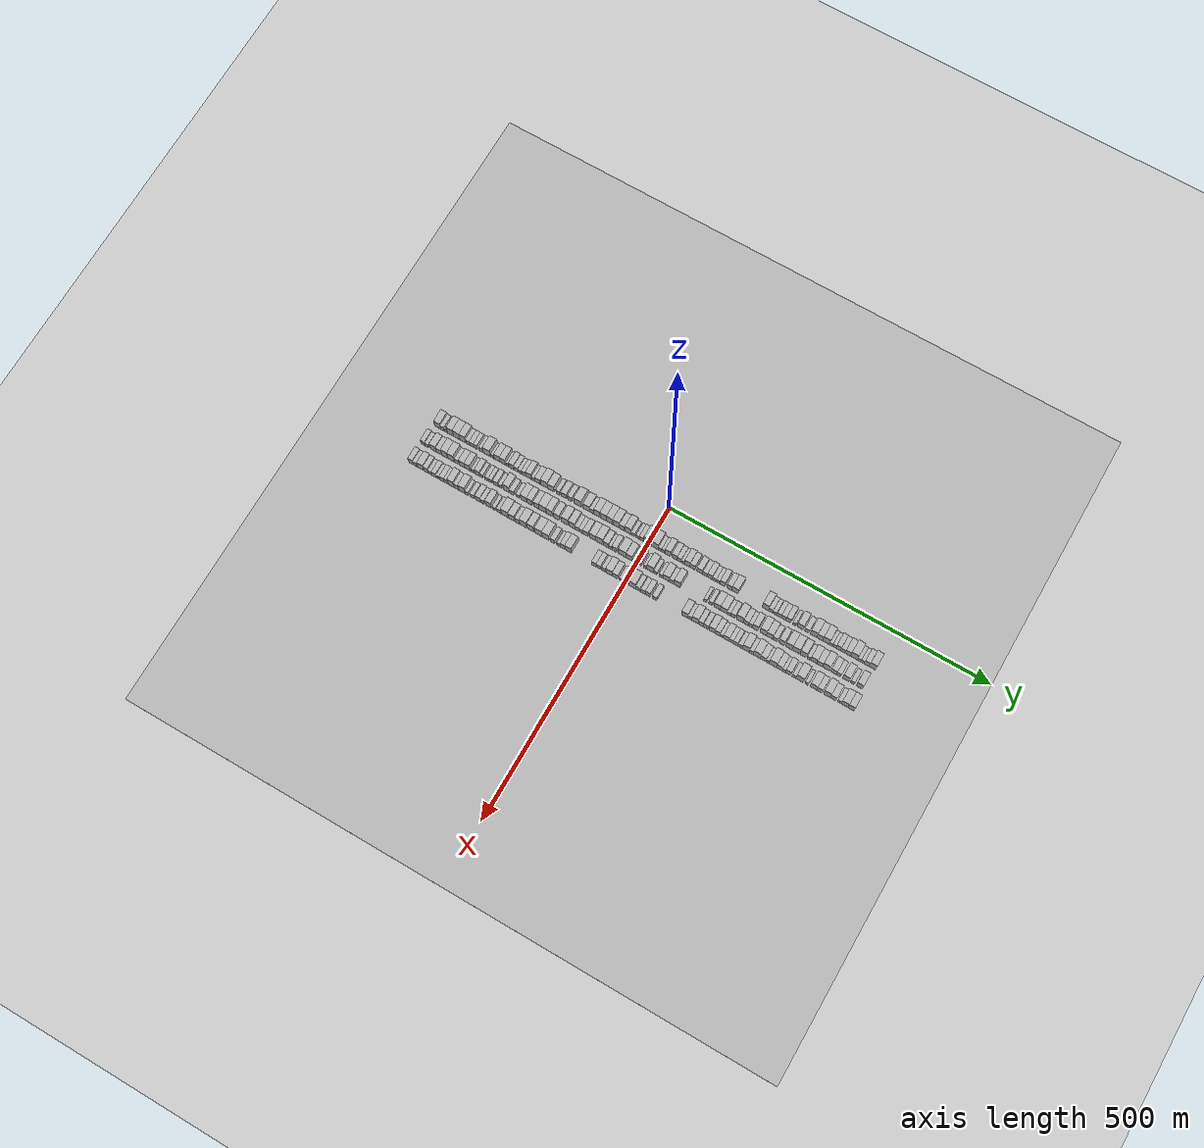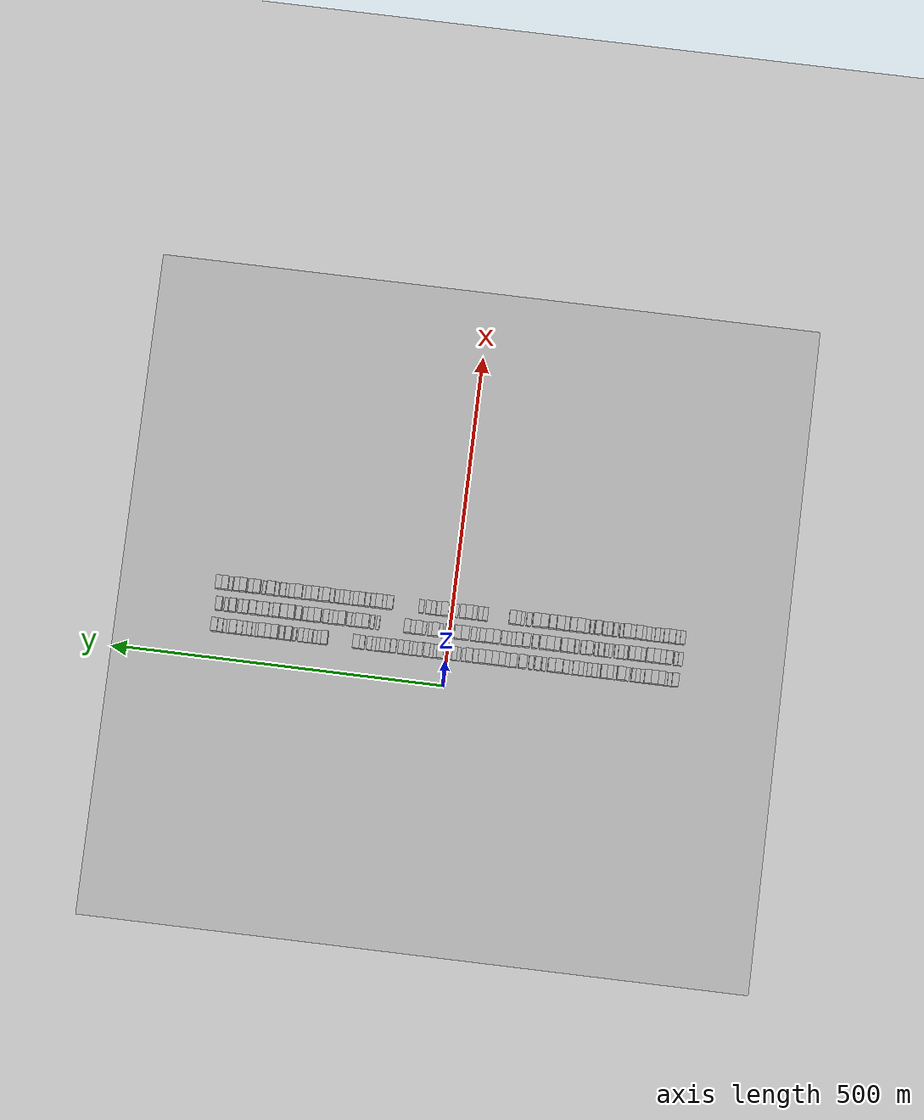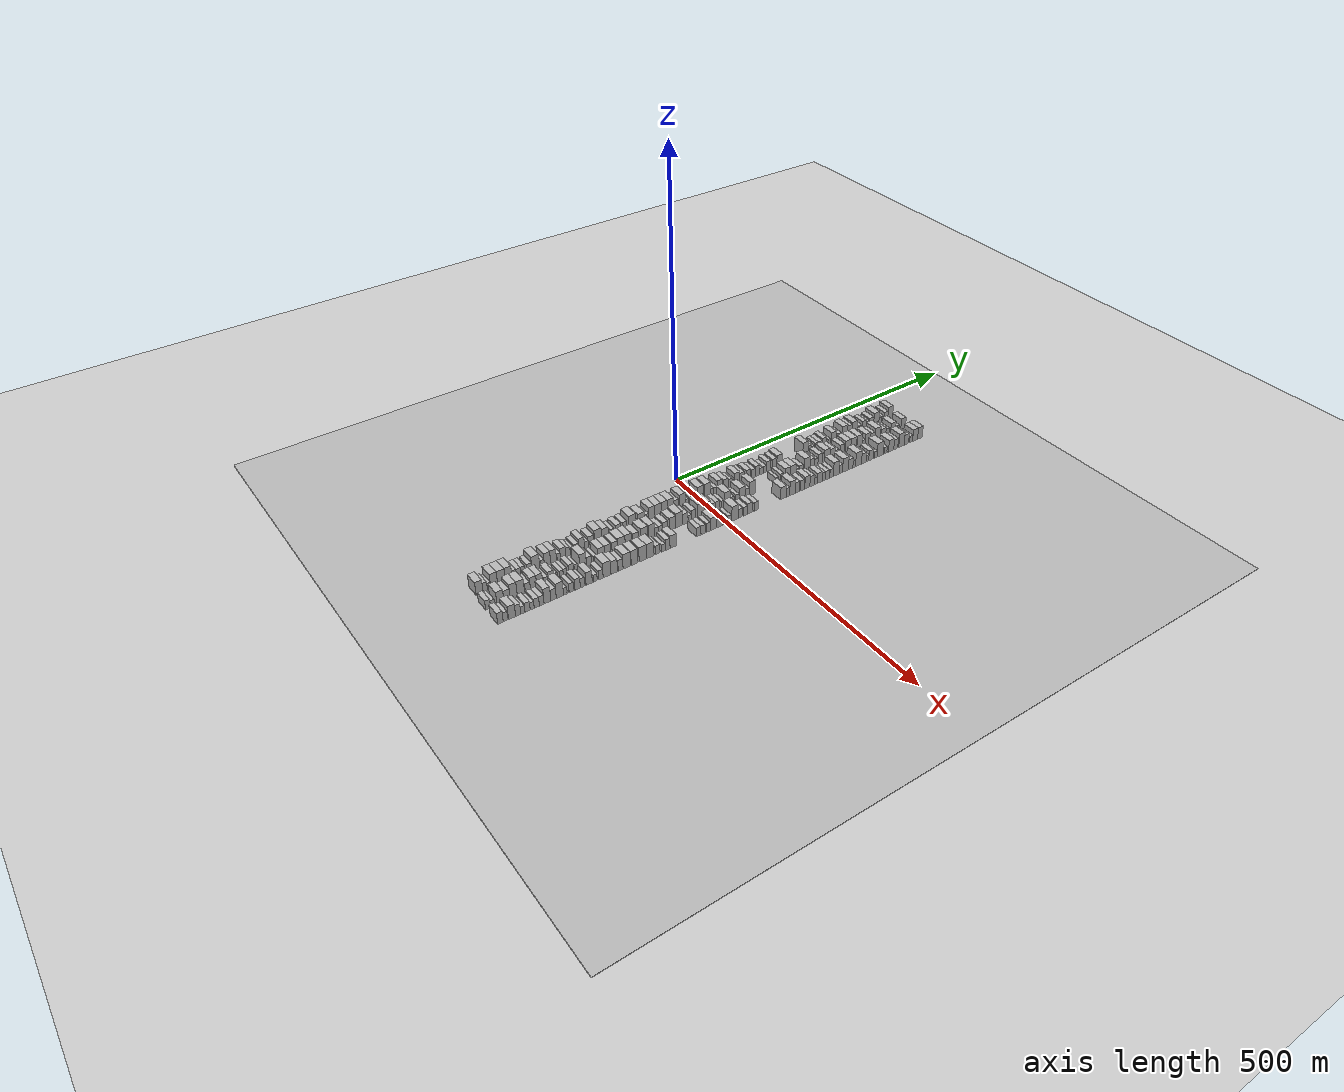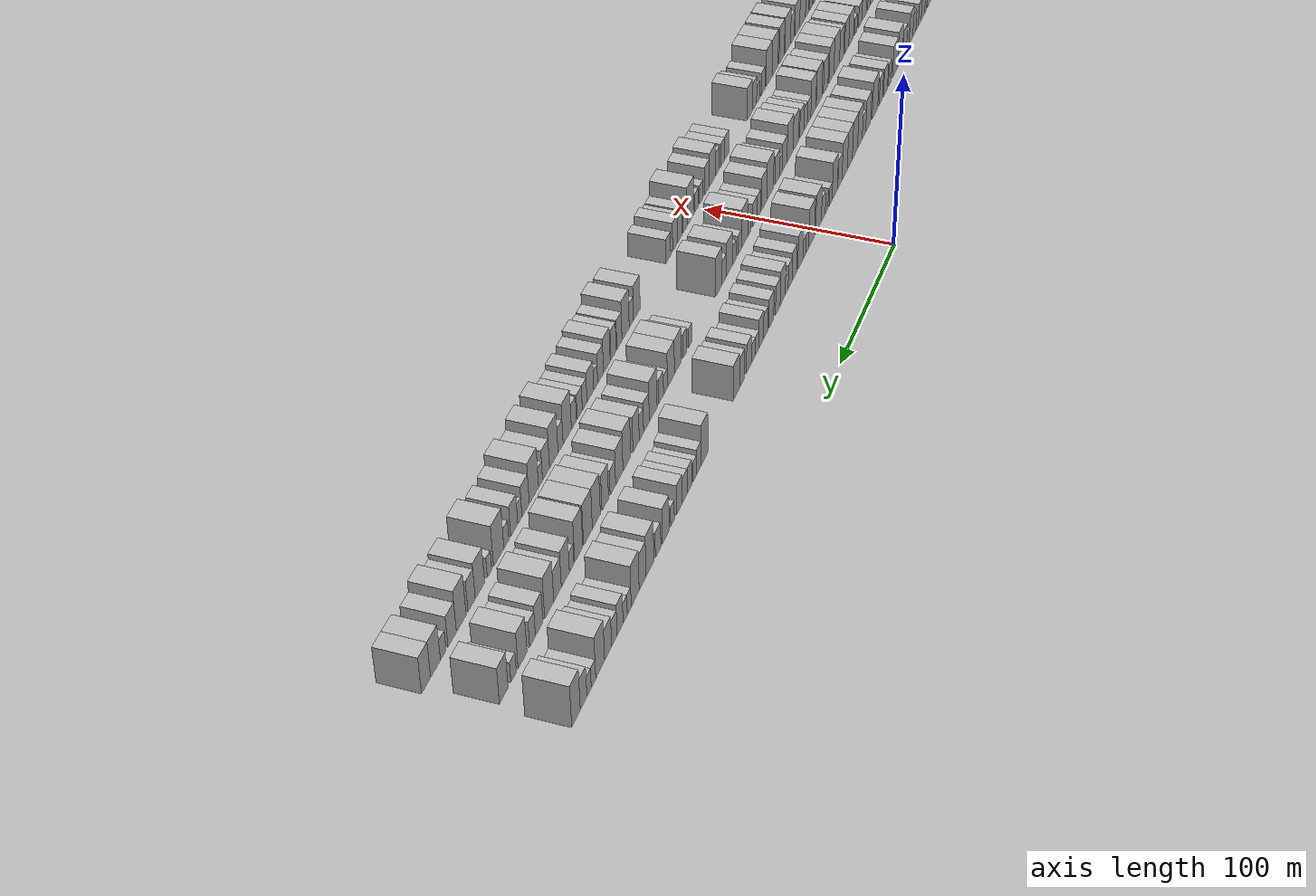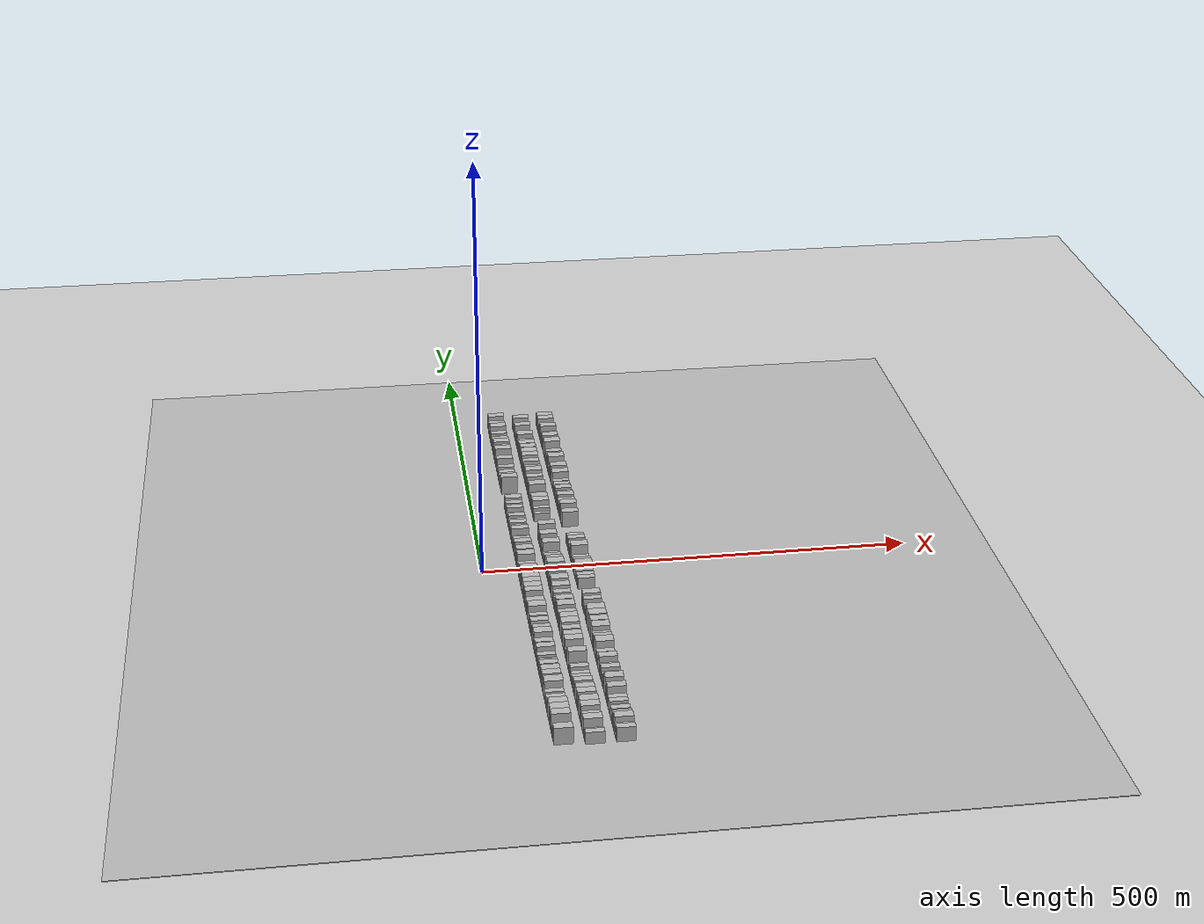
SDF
<?xml version="1.0" encoding="utf-8"?>

<sdf version="1.6">

   <world name="default">

      <gui fullscreen="0">

         <camera name="user_camera">

            <pose>-15 0 4.57585 0 0 0</pose>

            <view_controller>orbit</view_controller>

         </camera>

      </gui>

      <scene>

         <sky>

           <clouds>

             <speed>12</speed>

           </clouds>

         </sky>

         <ambient>0.4 0.4 0.4 1</ambient>

         <background>0.7 0.7 0.7 1</background>

         <shadows>1</shadows>

      </scene>

      <gravity>0 0 -9.8066</gravity>

      <magnetic_field>6e-06 2.3e-05 -4.2e-05</magnetic_field>

      <physics default="0" name="default_physics" type="ode">

         <ode>

            <solver>

               <type>quick</type>

               <iters>10</iters>

               <sor>1.0</sor>

               <use_dynamic_moi_rescaling>0</use_dynamic_moi_rescaling>

            </solver>

            <constraints>

               <cfm>0</cfm>

               <erp>0.2</erp>

               <contact_max_correcting_vel>100</contact_max_correcting_vel>

               <contact_surface_layer>0.001</contact_surface_layer>

            </constraints>

         </ode>

         <max_step_size>0.004</max_step_size>

         <real_time_factor>1</real_time_factor>

         <real_time_update_rate>250</real_time_update_rate>

      </physics>

      <light name="sun" type="directional">

         <cast_shadows>1</cast_shadows>

         <pose>0 0 10 0 0 0</pose>

         <diffuse>0.8 0.8 0.8 1</diffuse>

         <specular>0.2 0.2 0.2 1</specular>

         <attenuation>

            <range>1000</range>

            <constant>0.9</constant>

            <linear>0.01</linear>

            <quadratic>0.001</quadratic>

         </attenuation>

         <direction>-0.5 0.1 -0.9</direction>

      </light>

      <include>

         <name>ground_plane_1</name>

         <uri>model://HANNAS_ground_plane</uri>

         <pose>0 0 0  0 0 0</pose>

      </include>

      <include>

         <name>ground_plane_2</name>

         <uri>model://HANNAS_ground_plane</uri>

         <pose>100 0 0  0 0 0</pose>

      </include>

      <model name="building_1">

         <static>1</static>

         <pose frame="">50.0000 -340.0986 0 0.000000 0.000000 0.000000</pose>

         <link name="link">

            <pose frame="">0 0 10.50 0 0 0</pose>

            <collision name="collision">

               <geometry>

                  <box>

                     <size>20.0000 9.8028 21.0000</size>

                  </box>

               </geometry>

               <max_contacts>10</max_contacts>

               <surface>

                  <contact>

                     <ode/>

                  </contact>

                  <bounce/>

                  <friction>

                     <torsional>

                        <ode/>

                     </torsional>

                     <ode/>

                  </friction>

               </surface>

            </collision>

            <visual name="visual">

               <cast_shadows>0</cast_shadows>

               <geometry>

                  <box>

                     <size>20.0000 9.8028 21.0000</size>

                  </box>

               </geometry>

               <material>

                  <script>

                     <uri>model://HANNAS_wall/materials/scripts</uri>

                     <uri>model://HANNAS_wall/materials/textures</uri>

                     <name>vrc/HANNAS_wall</name>

                  </script>

               </material>

            </visual>

            <self_collide>0</self_collide>

            <enable_wind>0</enable_wind>

            <kinematic>0</kinematic>

         </link>

      </model>

      <model name="building_2">

         <static>1</static>

         <pose frame="">50.0000 -332.1278 0 0.000000 0.000000 0.000000</pose>

         <link name="link">

            <pose frame="">0 0 7.50 0 0 0</pose>

            <collision name="collision">

               <geometry>

                  <box>

                     <size>20.0000 6.1390 15.0000</size>

                  </box>

               </geometry>

               <max_contacts>10</max_contacts>

               <surface>

                  <contact>

                     <ode/>

                  </contact>

                  <bounce/>

                  <friction>

                     <torsional>

                        <ode/>

                     </torsional>

                     <ode/>

                  </friction>

               </surface>

            </collision>

            <visual name="visual">

               <cast_shadows>0</cast_shadows>

               <geometry>

                  <box>

                     <size>20.0000 6.1390 15.0000</size>

                  </box>

               </geometry>

               <material>

                  <script>

                     <uri>model://HANNAS_wall/materials/scripts</uri>

                     <uri>model://HANNAS_wall/materials/textures</uri>

                     <name>vrc/HANNAS_wall</name>

                  </script>

               </material>

            </visual>

            <self_collide>0</self_collide>

            <enable_wind>0</enable_wind>

            <kinematic>0</kinematic>

         </link>

      </model>

      <model name="building_3">

         <static>1</static>

         <pose frame="">50.0000 -326.6484 0 0.000000 0.000000 0.000000</pose>

         <link name="link">

            <pose frame="">0 0 6.00 0 0 0</pose>

            <collision name="collision">

               <geometry>

                  <box>

                     <size>20.0000 4.8198 12.0000</size>

                  </box>

               </geometry>

               <max_contacts>10</max_contacts>

               <surface>

                  <contact>

                     <ode/>

                  </contact>

                  <bounce/>

                  <friction>

                     <torsional>

                        <ode/>

                     </torsional>

                     <ode/>

                  </friction>

               </surface>

            </collision>

            <visual name="visual">

               <cast_shadows>0</cast_shadows>

               <geometry>

                  <box>

                     <size>20.0000 4.8198 12.0000</size>

                  </box>

               </geometry>

               <material>

                  <script>

                     <uri>model://HANNAS_wall/materials/scripts</uri>

                     <uri>model://HANNAS_wall/materials/textures</uri>

                     <name>vrc/HANNAS_wall</name>

                  </script>

               </material>

            </visual>

            <self_collide>0</self_collide>

            <enable_wind>0</enable_wind>

            <kinematic>0</kinematic>

         </link>

      </model>

      <model name="building_4">

         <static>1</static>

         <pose frame="">50.0000 -319.3556 0 0.000000 0.000000 0.000000</pose>

         <link name="link">

            <pose frame="">0 0 12.00 0 0 0</pose>

            <collision name="collision">

               <geometry>

                  <box>

                     <size>20.0000 9.7657 24.0000</size>

                  </box>

               </geometry>

               <max_contacts>10</max_contacts>

               <surface>

                  <contact>

                     <ode/>

                  </contact>

                  <bounce/>

                  <friction>

                     <torsional>

                        <ode/>

                     </torsional>

                     <ode/>

                  </friction>

               </surface>

            </collision>

            <visual name="visual">

               <cast_shadows>0</cast_shadows>

               <geometry>

                  <box>

                     <size>20.0000 9.7657 24.0000</size>

                  </box>

               </geometry>

               <material>

                  <script>

                     <uri>model://HANNAS_wall/materials/scripts</uri>

                     <uri>model://HANNAS_wall/materials/textures</uri>

                     <name>vrc/HANNAS_wall</name>

                  </script>

               </material>

            </visual>

            <self_collide>0</self_collide>

            <enable_wind>0</enable_wind>

            <kinematic>0</kinematic>

         </link>

      </model>

      <model name="building_5">

         <static>1</static>

         <pose frame="">50.0000 -309.0493 0 0.000000 0.000000 0.000000</pose>

         <link name="link">

            <pose frame="">0 0 12.00 0 0 0</pose>

            <collision name="collision">

               <geometry>

                  <box>

                     <size>20.0000 10.8469 24.0000</size>

                  </box>

               </geometry>

               <max_contacts>10</max_contacts>

               <surface>

                  <contact>

                     <ode/>

                  </contact>

                  <bounce/>

                  <friction>

                     <torsional>

                        <ode/>

                     </torsional>

                     <ode/>

                  </friction>

               </surface>

            </collision>

            <visual name="visual">

               <cast_shadows>0</cast_shadows>

               <geometry>

                  <box>

                     <size>20.0000 10.8469 24.0000</size>

                  </box>

               </geometry>

               <material>

                  <script>

                     <uri>model://HANNAS_wall/materials/scripts</uri>

                     <uri>model://HANNAS_wall/materials/textures</uri>

                     <name>vrc/HANNAS_wall</name>

                  </script>

               </material>

            </visual>

            <self_collide>0</self_collide>

            <enable_wind>0</enable_wind>

            <kinematic>0</kinematic>

         </link>

      </model>

      <model name="building_6">

         <static>1</static>

         <pose frame="">50.0000 -298.7794 0 0.000000 0.000000 0.000000</pose>

         <link name="link">

            <pose frame="">0 0 12.00 0 0 0</pose>

            <collision name="collision">

               <geometry>

                  <box>

                     <size>20.0000 9.6930 24.0000</size>

                  </box>

               </geometry>

               <max_contacts>10</max_contacts>

               <surface>

                  <contact>

                     <ode/>

                  </contact>

                  <bounce/>

                  <friction>

                     <torsional>

                        <ode/>

                     </torsional>

                     <ode/>

                  </friction>

               </surface>

            </collision>

            <visual name="visual">

               <cast_shadows>0</cast_shadows>

               <geometry>

                  <box>

                     <size>20.0000 9.6930 24.0000</size>

                  </box>

               </geometry>

               <material>

                  <script>

                     <uri>model://HANNAS_wall/materials/scripts</uri>

                     <uri>model://HANNAS_wall/materials/textures</uri>

                     <name>vrc/HANNAS_wall</name>

                  </script>

               </material>

            </visual>

            <self_collide>0</self_collide>

            <enable_wind>0</enable_wind>

            <kinematic>0</kinematic>

         </link>

      </model>

      <model name="building_7">

         <static>1</static>

         <pose frame="">50.0000 -290.8501 0 0.000000 0.000000 0.000000</pose>

         <link name="link">

            <pose frame="">0 0 7.50 0 0 0</pose>

            <collision name="collision">

               <geometry>

                  <box>

                     <size>20.0000 6.1656 15.0000</size>

                  </box>

               </geometry>

               <max_contacts>10</max_contacts>

               <surface>

                  <contact>

                     <ode/>

                  </contact>

                  <bounce/>

                  <friction>

                     <torsional>

                        <ode/>

                     </torsional>

                     <ode/>

                  </friction>

               </surface>

            </collision>

            <visual name="visual">

               <cast_shadows>0</cast_shadows>

               <geometry>

                  <box>

                     <size>20.0000 6.1656 15.0000</size>

                  </box>

               </geometry>

               <material>

                  <script>

                     <uri>model://HANNAS_wall/materials/scripts</uri>

                     <uri>model://HANNAS_wall/materials/textures</uri>

                     <name>vrc/HANNAS_wall</name>

                  </script>

               </material>

            </visual>

            <self_collide>0</self_collide>

            <enable_wind>0</enable_wind>

            <kinematic>0</kinematic>

         </link>

      </model>

      <model name="building_8">

         <static>1</static>

         <pose frame="">50.0000 -284.4406 0 0.000000 0.000000 0.000000</pose>

         <link name="link">

            <pose frame="">0 0 7.50 0 0 0</pose>

            <collision name="collision">

               <geometry>

                  <box>

                     <size>20.0000 6.6534 15.0000</size>

                  </box>

               </geometry>

               <max_contacts>10</max_contacts>

               <surface>

                  <contact>

                     <ode/>

                  </contact>

                  <bounce/>

                  <friction>

                     <torsional>

                        <ode/>

                     </torsional>

                     <ode/>

                  </friction>

               </surface>

            </collision>

            <visual name="visual">

               <cast_shadows>0</cast_shadows>

               <geometry>

                  <box>

                     <size>20.0000 6.6534 15.0000</size>

                  </box>

               </geometry>

               <material>

                  <script>

                     <uri>model://HANNAS_wall/materials/scripts</uri>

                     <uri>model://HANNAS_wall/materials/textures</uri>

                     <name>vrc/HANNAS_wall</name>

                  </script>

               </material>

            </visual>

            <self_collide>0</self_collide>

            <enable_wind>0</enable_wind>

            <kinematic>0</kinematic>

         </link>

      </model>

      <model name="building_9">

         <static>1</static>

         <pose frame="">50.0000 -278.0983 0 0.000000 0.000000 0.000000</pose>

         <link name="link">

            <pose frame="">0 0 7.50 0 0 0</pose>

            <collision name="collision">

               <geometry>

                  <box>

                     <size>20.0000 6.0312 15.0000</size>

                  </box>

               </geometry>

               <max_contacts>10</max_contacts>

               <surface>

                  <contact>

                     <ode/>

                  </contact>

                  <bounce/>

                  <friction>

                     <torsional>

                        <ode/>

                     </torsional>

                     <ode/>

                  </friction>

               </surface>

            </collision>

            <visual name="visual">

               <cast_shadows>0</cast_shadows>

               <geometry>

                  <box>

                     <size>20.0000 6.0312 15.0000</size>

                  </box>

               </geometry>

               <material>

                  <script>

                     <uri>model://HANNAS_wall/materials/scripts</uri>

                     <uri>model://HANNAS_wall/materials/textures</uri>

                     <name>vrc/HANNAS_wall</name>

                  </script>

               </material>

            </visual>

            <self_collide>0</self_collide>

            <enable_wind>0</enable_wind>

            <kinematic>0</kinematic>

         </link>

      </model>

      <model name="building_10">

         <static>1</static>

         <pose frame="">50.0000 -268.6760 0 0.000000 0.000000 0.000000</pose>

         <link name="link">

            <pose frame="">0 0 7.50 0 0 0</pose>

            <collision name="collision">

               <geometry>

                  <box>

                     <size>20.0000 6.8134 15.0000</size>

                  </box>

               </geometry>

               <max_contacts>10</max_contacts>

               <surface>

                  <contact>

                     <ode/>

                  </contact>

                  <bounce/>

                  <friction>

                     <torsional>

                        <ode/>

                     </torsional>

                     <ode/>

                  </friction>

               </surface>

            </collision>

            <visual name="visual">

               <cast_shadows>0</cast_shadows>

               <geometry>

                  <box>

                     <size>20.0000 6.8134 15.0000</size>

                  </box>

               </geometry>

               <material>

                  <script>

                     <uri>model://HANNAS_wall/materials/scripts</uri>

                     <uri>model://HANNAS_wall/materials/textures</uri>

                     <name>vrc/HANNAS_wall</name>

                  </script>

               </material>

            </visual>

            <self_collide>0</self_collide>

            <enable_wind>0</enable_wind>

            <kinematic>0</kinematic>

         </link>

      </model>

      <model name="building_11">

         <static>1</static>

         <pose frame="">50.0000 -259.5664 0 0.000000 0.000000 0.000000</pose>

         <link name="link">

            <pose frame="">0 0 12.00 0 0 0</pose>

            <collision name="collision">

               <geometry>

                  <box>

                     <size>20.0000 11.4057 24.0000</size>

                  </box>

               </geometry>

               <max_contacts>10</max_contacts>

               <surface>

                  <contact>

                     <ode/>

                  </contact>

                  <bounce/>

                  <friction>

                     <torsional>

                        <ode/>

                     </torsional>

                     <ode/>

                  </friction>

               </surface>

            </collision>

            <visual name="visual">

               <cast_shadows>0</cast_shadows>

               <geometry>

                  <box>

                     <size>20.0000 11.4057 24.0000</size>

                  </box>

               </geometry>

               <material>

                  <script>

                     <uri>model://HANNAS_wall/materials/scripts</uri>

                     <uri>model://HANNAS_wall/materials/textures</uri>

                     <name>vrc/HANNAS_wall</name>

                  </script>

               </material>

            </visual>

            <self_collide>0</self_collide>

            <enable_wind>0</enable_wind>

            <kinematic>0</kinematic>

         </link>

      </model>

      <model name="building_12">

         <static>1</static>

         <pose frame="">50.0000 -250.0092 0 0.000000 0.000000 0.000000</pose>

         <link name="link">

            <pose frame="">0 0 6.00 0 0 0</pose>

            <collision name="collision">

               <geometry>

                  <box>

                     <size>20.0000 5.7088 12.0000</size>

                  </box>

               </geometry>

               <max_contacts>10</max_contacts>

               <surface>

                  <contact>

                     <ode/>

                  </contact>

                  <bounce/>

                  <friction>

                     <torsional>

                        <ode/>

                     </torsional>

                     <ode/>

                  </friction>

               </surface>

            </collision>

            <visual name="visual">

               <cast_shadows>0</cast_shadows>

               <geometry>

                  <box>

                     <size>20.0000 5.7088 12.0000</size>

                  </box>

               </geometry>

               <material>

                  <script>

                     <uri>model://HANNAS_wall/materials/scripts</uri>

                     <uri>model://HANNAS_wall/materials/textures</uri>

                     <name>vrc/HANNAS_wall</name>

                  </script>

               </material>

            </visual>

            <self_collide>0</self_collide>

            <enable_wind>0</enable_wind>

            <kinematic>0</kinematic>

         </link>

      </model>

      <model name="building_13">

         <static>1</static>

         <pose frame="">50.0000 -242.6174 0 0.000000 0.000000 0.000000</pose>

         <link name="link">

            <pose frame="">0 0 10.50 0 0 0</pose>

            <collision name="collision">

               <geometry>

                  <box>

                     <size>20.0000 9.0748 21.0000</size>

                  </box>

               </geometry>

               <max_contacts>10</max_contacts>

               <surface>

                  <contact>

                     <ode/>

                  </contact>

                  <bounce/>

                  <friction>

                     <torsional>

                        <ode/>

                     </torsional>

                     <ode/>

                  </friction>

               </surface>

            </collision>

            <visual name="visual">

               <cast_shadows>0</cast_shadows>

               <geometry>

                  <box>

                     <size>20.0000 9.0748 21.0000</size>

                  </box>

               </geometry>

               <material>

                  <script>

                     <uri>model://HANNAS_wall/materials/scripts</uri>

                     <uri>model://HANNAS_wall/materials/textures</uri>

                     <name>vrc/HANNAS_wall</name>

                  </script>

               </material>

            </visual>

            <self_collide>0</self_collide>

            <enable_wind>0</enable_wind>

            <kinematic>0</kinematic>

         </link>

      </model>

      <model name="building_14">

         <static>1</static>

         <pose frame="">50.0000 -233.6881 0 0.000000 0.000000 0.000000</pose>

         <link name="link">

            <pose frame="">0 0 10.50 0 0 0</pose>

            <collision name="collision">

               <geometry>

                  <box>

                     <size>20.0000 8.7838 21.0000</size>

                  </box>

               </geometry>

               <max_contacts>10</max_contacts>

               <surface>

                  <contact>

                     <ode/>

                  </contact>

                  <bounce/>

                  <friction>

                     <torsional>

                        <ode/>

                     </torsional>

                     <ode/>

                  </friction>

               </surface>

            </collision>

            <visual name="visual">

               <cast_shadows>0</cast_shadows>

               <geometry>

                  <box>

                     <size>20.0000 8.7838 21.0000</size>

                  </box>

               </geometry>

               <material>

                  <script>

                     <uri>model://HANNAS_wall/materials/scripts</uri>

                     <uri>model://HANNAS_wall/materials/textures</uri>

                     <name>vrc/HANNAS_wall</name>

                  </script>

               </material>

            </visual>

            <self_collide>0</self_collide>

            <enable_wind>0</enable_wind>

            <kinematic>0</kinematic>

         </link>

      </model>

      <model name="building_15">

         <static>1</static>

         <pose frame="">50.0000 -225.8826 0 0.000000 0.000000 0.000000</pose>

         <link name="link">

            <pose frame="">0 0 6.00 0 0 0</pose>

            <collision name="collision">

               <geometry>

                  <box>

                     <size>20.0000 4.8271 12.0000</size>

                  </box>

               </geometry>

               <max_contacts>10</max_contacts>

               <surface>

                  <contact>

                     <ode/>

                  </contact>

                  <bounce/>

                  <friction>

                     <torsional>

                        <ode/>

                     </torsional>

                     <ode/>

                  </friction>

               </surface>

            </collision>

            <visual name="visual">

               <cast_shadows>0</cast_shadows>

               <geometry>

                  <box>

                     <size>20.0000 4.8271 12.0000</size>

                  </box>

               </geometry>

               <material>

                  <script>

                     <uri>model://HANNAS_wall/materials/scripts</uri>

                     <uri>model://HANNAS_wall/materials/textures</uri>

                     <name>vrc/HANNAS_wall</name>

                  </script>

               </material>

            </visual>

            <self_collide>0</self_collide>

            <enable_wind>0</enable_wind>

            <kinematic>0</kinematic>

         </link>

      </model>

      <model name="building_16">

         <static>1</static>

         <pose frame="">50.0000 -219.4341 0 0.000000 0.000000 0.000000</pose>

         <link name="link">

            <pose frame="">0 0 9.00 0 0 0</pose>

            <collision name="collision">

               <geometry>

                  <box>

                     <size>20.0000 8.0699 18.0000</size>

                  </box>

               </geometry>

               <max_contacts>10</max_contacts>

               <surface>

                  <contact>

                     <ode/>

                  </contact>

                  <bounce/>

                  <friction>

                     <torsional>

                        <ode/>

                     </torsional>

                     <ode/>

                  </friction>

               </surface>

            </collision>

            <visual name="visual">

               <cast_shadows>0</cast_shadows>

               <geometry>

                  <box>

                     <size>20.0000 8.0699 18.0000</size>

                  </box>

               </geometry>

               <material>

                  <script>

                     <uri>model://HANNAS_wall/materials/scripts</uri>

                     <uri>model://HANNAS_wall/materials/textures</uri>

                     <name>vrc/HANNAS_wall</name>

                  </script>

               </material>

            </visual>

            <self_collide>0</self_collide>

            <enable_wind>0</enable_wind>

            <kinematic>0</kinematic>

         </link>

      </model>

      <model name="building_17">

         <static>1</static>

         <pose frame="">50.0000 -212.0149 0 0.000000 0.000000 0.000000</pose>

         <link name="link">

            <pose frame="">0 0 7.50 0 0 0</pose>

            <collision name="collision">

               <geometry>

                  <box>

                     <size>20.0000 6.7684 15.0000</size>

                  </box>

               </geometry>

               <max_contacts>10</max_contacts>

               <surface>

                  <contact>

                     <ode/>

                  </contact>

                  <bounce/>

                  <friction>

                     <torsional>

                        <ode/>

                     </torsional>

                     <ode/>

                  </friction>

               </surface>

            </collision>

            <visual name="visual">

               <cast_shadows>0</cast_shadows>

               <geometry>

                  <box>

                     <size>20.0000 6.7684 15.0000</size>

                  </box>

               </geometry>

               <material>

                  <script>

                     <uri>model://HANNAS_wall/materials/scripts</uri>

                     <uri>model://HANNAS_wall/materials/textures</uri>

                     <name>vrc/HANNAS_wall</name>

                  </script>

               </material>

            </visual>

            <self_collide>0</self_collide>

            <enable_wind>0</enable_wind>

            <kinematic>0</kinematic>

         </link>

      </model>

      <model name="building_18">

         <static>1</static>

         <pose frame="">50.0000 -205.7448 0 0.000000 0.000000 0.000000</pose>

         <link name="link">

            <pose frame="">0 0 6.00 0 0 0</pose>

            <collision name="collision">

               <geometry>

                  <box>

                     <size>20.0000 5.7718 12.0000</size>

                  </box>

               </geometry>

               <max_contacts>10</max_contacts>

               <surface>

                  <contact>

                     <ode/>

                  </contact>

                  <bounce/>

                  <friction>

                     <torsional>

                        <ode/>

                     </torsional>

                     <ode/>

                  </friction>

               </surface>

            </collision>

            <visual name="visual">

               <cast_shadows>0</cast_shadows>

               <geometry>

                  <box>

                     <size>20.0000 5.7718 12.0000</size>

                  </box>

               </geometry>

               <material>

                  <script>

                     <uri>model://HANNAS_wall/materials/scripts</uri>

                     <uri>model://HANNAS_wall/materials/textures</uri>

                     <name>vrc/HANNAS_wall</name>

                  </script>

               </material>

            </visual>

            <self_collide>0</self_collide>

            <enable_wind>0</enable_wind>

            <kinematic>0</kinematic>

         </link>

      </model>

      <model name="building_19">

         <static>1</static>

         <pose frame="">50.0000 -199.2922 0 0.000000 0.000000 0.000000</pose>

         <link name="link">

            <pose frame="">0 0 7.50 0 0 0</pose>

            <collision name="collision">

               <geometry>

                  <box>

                     <size>20.0000 7.1336 15.0000</size>

                  </box>

               </geometry>

               <max_contacts>10</max_contacts>

               <surface>

                  <contact>

                     <ode/>

                  </contact>

                  <bounce/>

                  <friction>

                     <torsional>

                        <ode/>

                     </torsional>

                     <ode/>

                  </friction>

               </surface>

            </collision>

            <visual name="visual">

               <cast_shadows>0</cast_shadows>

               <geometry>

                  <box>

                     <size>20.0000 7.1336 15.0000</size>

                  </box>

               </geometry>

               <material>

                  <script>

                     <uri>model://HANNAS_wall/materials/scripts</uri>

                     <uri>model://HANNAS_wall/materials/textures</uri>

                     <name>vrc/HANNAS_wall</name>

                  </script>

               </material>

            </visual>

            <self_collide>0</self_collide>

            <enable_wind>0</enable_wind>

            <kinematic>0</kinematic>

         </link>

      </model>

      <model name="building_20">

         <static>1</static>

         <pose frame="">50.0000 -191.3891 0 0.000000 0.000000 0.000000</pose>

         <link name="link">

            <pose frame="">0 0 10.50 0 0 0</pose>

            <collision name="collision">

               <geometry>

                  <box>

                     <size>20.0000 8.6725 21.0000</size>

                  </box>

               </geometry>

               <max_contacts>10</max_contacts>

               <surface>

                  <contact>

                     <ode/>

                  </contact>

                  <bounce/>

                  <friction>

                     <torsional>

                        <ode/>

                     </torsional>

                     <ode/>

                  </friction>

               </surface>

            </collision>

            <visual name="visual">

               <cast_shadows>0</cast_shadows>

               <geometry>

                  <box>

                     <size>20.0000 8.6725 21.0000</size>

                  </box>

               </geometry>

               <material>

                  <script>

                     <uri>model://HANNAS_wall/materials/scripts</uri>

                     <uri>model://HANNAS_wall/materials/textures</uri>

                     <name>vrc/HANNAS_wall</name>

                  </script>

               </material>

            </visual>

            <self_collide>0</self_collide>

            <enable_wind>0</enable_wind>

            <kinematic>0</kinematic>

         </link>

      </model>

      <model name="building_21">

         <static>1</static>

         <pose frame="">50.0000 -184.1292 0 0.000000 0.000000 0.000000</pose>

         <link name="link">

            <pose frame="">0 0 6.00 0 0 0</pose>

            <collision name="collision">

               <geometry>

                  <box>

                     <size>20.0000 5.8472 12.0000</size>

                  </box>

               </geometry>

               <max_contacts>10</max_contacts>

               <surface>

                  <contact>

                     <ode/>

                  </contact>

                  <bounce/>

                  <friction>

                     <torsional>

                        <ode/>

                     </torsional>

                     <ode/>

                  </friction>

               </surface>

            </collision>

            <visual name="visual">

               <cast_shadows>0</cast_shadows>

               <geometry>

                  <box>

                     <size>20.0000 5.8472 12.0000</size>

                  </box>

               </geometry>

               <material>

                  <script>

                     <uri>model://HANNAS_wall/materials/scripts</uri>

                     <uri>model://HANNAS_wall/materials/textures</uri>

                     <name>vrc/HANNAS_wall</name>

                  </script>

               </material>

            </visual>

            <self_collide>0</self_collide>

            <enable_wind>0</enable_wind>

            <kinematic>0</kinematic>

         </link>

      </model>

      <model name="building_22">

         <static>1</static>

         <pose frame="">50.0000 -176.8922 0 0.000000 0.000000 0.000000</pose>

         <link name="link">

            <pose frame="">0 0 9.00 0 0 0</pose>

            <collision name="collision">

               <geometry>

                  <box>

                     <size>20.0000 8.6268 18.0000</size>

                  </box>

               </geometry>

               <max_contacts>10</max_contacts>

               <surface>

                  <contact>

                     <ode/>

                  </contact>

                  <bounce/>

                  <friction>

                     <torsional>

                        <ode/>

                     </torsional>

                     <ode/>

                  </friction>

               </surface>

            </collision>

            <visual name="visual">

               <cast_shadows>0</cast_shadows>

               <geometry>

                  <box>

                     <size>20.0000 8.6268 18.0000</size>

                  </box>

               </geometry>

               <material>

                  <script>

                     <uri>model://HANNAS_wall/materials/scripts</uri>

                     <uri>model://HANNAS_wall/materials/textures</uri>

                     <name>vrc/HANNAS_wall</name>

                  </script>

               </material>

            </visual>

            <self_collide>0</self_collide>

            <enable_wind>0</enable_wind>

            <kinematic>0</kinematic>

         </link>

      </model>

      <model name="building_23">

         <static>1</static>

         <pose frame="">50.0000 -166.0902 0 0.000000 0.000000 0.000000</pose>

         <link name="link">

            <pose frame="">0 0 12.00 0 0 0</pose>

            <collision name="collision">

               <geometry>

                  <box>

                     <size>20.0000 10.9774 24.0000</size>

                  </box>

               </geometry>

               <max_contacts>10</max_contacts>

               <surface>

                  <contact>

                     <ode/>

                  </contact>

                  <bounce/>

                  <friction>

                     <torsional>

                        <ode/>

                     </torsional>

                     <ode/>

                  </friction>

               </surface>

            </collision>

            <visual name="visual">

               <cast_shadows>0</cast_shadows>

               <geometry>

                  <box>

                     <size>20.0000 10.9774 24.0000</size>

                  </box>

               </geometry>

               <material>

                  <script>

                     <uri>model://HANNAS_wall/materials/scripts</uri>

                     <uri>model://HANNAS_wall/materials/textures</uri>

                     <name>vrc/HANNAS_wall</name>

                  </script>

               </material>

            </visual>

            <self_collide>0</self_collide>

            <enable_wind>0</enable_wind>

            <kinematic>0</kinematic>

         </link>

      </model>

      <model name="building_24">

         <static>1</static>

         <pose frame="">50.0000 -155.3657 0 0.000000 0.000000 0.000000</pose>

         <link name="link">

            <pose frame="">0 0 10.50 0 0 0</pose>

            <collision name="collision">

               <geometry>

                  <box>

                     <size>20.0000 10.4715 21.0000</size>

                  </box>

               </geometry>

               <max_contacts>10</max_contacts>

               <surface>

                  <contact>

                     <ode/>

                  </contact>

                  <bounce/>

                  <friction>

                     <torsional>

                        <ode/>

                     </torsional>

                     <ode/>

                  </friction>

               </surface>

            </collision>

            <visual name="visual">

               <cast_shadows>0</cast_shadows>

               <geometry>

                  <box>

                     <size>20.0000 10.4715 21.0000</size>

                  </box>

               </geometry>

               <material>

                  <script>

                     <uri>model://HANNAS_wall/materials/scripts</uri>

                     <uri>model://HANNAS_wall/materials/textures</uri>

                     <name>vrc/HANNAS_wall</name>

                  </script>

               </material>

            </visual>

            <self_collide>0</self_collide>

            <enable_wind>0</enable_wind>

            <kinematic>0</kinematic>

         </link>

      </model>

      <model name="building_25">

         <static>1</static>

         <pose frame="">50.0000 -144.1026 0 0.000000 0.000000 0.000000</pose>

         <link name="link">

            <pose frame="">0 0 7.50 0 0 0</pose>

            <collision name="collision">

               <geometry>

                  <box>

                     <size>20.0000 6.0546 15.0000</size>

                  </box>

               </geometry>

               <max_contacts>10</max_contacts>

               <surface>

                  <contact>

                     <ode/>

                  </contact>

                  <bounce/>

                  <friction>

                     <torsional>

                        <ode/>

                     </torsional>

                     <ode/>

                  </friction>

               </surface>

            </collision>

            <visual name="visual">

               <cast_shadows>0</cast_shadows>

               <geometry>

                  <box>

                     <size>20.0000 6.0546 15.0000</size>

                  </box>

               </geometry>

               <material>

                  <script>

                     <uri>model://HANNAS_wall/materials/scripts</uri>

                     <uri>model://HANNAS_wall/materials/textures</uri>

                     <name>vrc/HANNAS_wall</name>

                  </script>

               </material>

            </visual>

            <self_collide>0</self_collide>

            <enable_wind>0</enable_wind>

            <kinematic>0</kinematic>

         </link>

      </model>

      <model name="building_26">

         <static>1</static>

         <pose frame="">50.0000 -134.7185 0 0.000000 0.000000 0.000000</pose>

         <link name="link">

            <pose frame="">0 0 9.00 0 0 0</pose>

            <collision name="collision">

               <geometry>

                  <box>

                     <size>20.0000 8.7136 18.0000</size>

                  </box>

               </geometry>

               <max_contacts>10</max_contacts>

               <surface>

                  <contact>

                     <ode/>

                  </contact>

                  <bounce/>

                  <friction>

                     <torsional>

                        <ode/>

                     </torsional>

                     <ode/>

                  </friction>

               </surface>

            </collision>

            <visual name="visual">

               <cast_shadows>0</cast_shadows>

               <geometry>

                  <box>

                     <size>20.0000 8.7136 18.0000</size>

                  </box>

               </geometry>

               <material>

                  <script>

                     <uri>model://HANNAS_wall/materials/scripts</uri>

                     <uri>model://HANNAS_wall/materials/textures</uri>

                     <name>vrc/HANNAS_wall</name>

                  </script>

               </material>

            </visual>

            <self_collide>0</self_collide>

            <enable_wind>0</enable_wind>

            <kinematic>0</kinematic>

         </link>

      </model>

      <model name="building_27">

         <static>1</static>

         <pose frame="">50.0000 -124.7429 0 0.000000 0.000000 0.000000</pose>

         <link name="link">

            <pose frame="">0 0 9.00 0 0 0</pose>

            <collision name="collision">

               <geometry>

                  <box>

                     <size>20.0000 7.2376 18.0000</size>

                  </box>

               </geometry>

               <max_contacts>10</max_contacts>

               <surface>

                  <contact>

                     <ode/>

                  </contact>

                  <bounce/>

                  <friction>

                     <torsional>

                        <ode/>

                     </torsional>

                     <ode/>

                  </friction>

               </surface>

            </collision>

            <visual name="visual">

               <cast_shadows>0</cast_shadows>

               <geometry>

                  <box>

                     <size>20.0000 7.2376 18.0000</size>

                  </box>

               </geometry>

               <material>

                  <script>

                     <uri>model://HANNAS_wall/materials/scripts</uri>

                     <uri>model://HANNAS_wall/materials/textures</uri>

                     <name>vrc/HANNAS_wall</name>

                  </script>

               </material>

            </visual>

            <self_collide>0</self_collide>

            <enable_wind>0</enable_wind>

            <kinematic>0</kinematic>

         </link>

      </model>

      <model name="building_28">

         <static>1</static>

         <pose frame="">50.0000 -112.2866 0 0.000000 0.000000 0.000000</pose>

         <link name="link">

            <pose frame="">0 0 12.00 0 0 0</pose>

            <collision name="collision">

               <geometry>

                  <box>

                     <size>20.0000 11.6752 24.0000</size>

                  </box>

               </geometry>

               <max_contacts>10</max_contacts>

               <surface>

                  <contact>

                     <ode/>

                  </contact>

                  <bounce/>

                  <friction>

                     <torsional>

                        <ode/>

                     </torsional>

                     <ode/>

                  </friction>

               </surface>

            </collision>

            <visual name="visual">

               <cast_shadows>0</cast_shadows>

               <geometry>

                  <box>

                     <size>20.0000 11.6752 24.0000</size>

                  </box>

               </geometry>

               <material>

                  <script>

                     <uri>model://HANNAS_wall/materials/scripts</uri>

                     <uri>model://HANNAS_wall/materials/textures</uri>

                     <name>vrc/HANNAS_wall</name>

                  </script>

               </material>

            </visual>

            <self_collide>0</self_collide>

            <enable_wind>0</enable_wind>

            <kinematic>0</kinematic>

         </link>

      </model>

      <model name="building_29">

         <static>1</static>

         <pose frame="">50.0000 -98.2323 0 0.000000 0.000000 0.000000</pose>

         <link name="link">

            <pose frame="">0 0 10.50 0 0 0</pose>

            <collision name="collision">

               <geometry>

                  <box>

                     <size>20.0000 10.4334 21.0000</size>

                  </box>

               </geometry>

               <max_contacts>10</max_contacts>

               <surface>

                  <contact>

                     <ode/>

                  </contact>

                  <bounce/>

                  <friction>

                     <torsional>

                        <ode/>

                     </torsional>

                     <ode/>

                  </friction>

               </surface>

            </collision>

            <visual name="visual">

               <cast_shadows>0</cast_shadows>

               <geometry>

                  <box>

                     <size>20.0000 10.4334 21.0000</size>

                  </box>

               </geometry>

               <material>

                  <script>

                     <uri>model://HANNAS_wall/materials/scripts</uri>

                     <uri>model://HANNAS_wall/materials/textures</uri>

                     <name>vrc/HANNAS_wall</name>

                  </script>

               </material>

            </visual>

            <self_collide>0</self_collide>

            <enable_wind>0</enable_wind>

            <kinematic>0</kinematic>

         </link>

      </model>

      <model name="building_30">

         <static>1</static>

         <pose frame="">50.0000 -89.5312 0 0.000000 0.000000 0.000000</pose>

         <link name="link">

            <pose frame="">0 0 7.50 0 0 0</pose>

            <collision name="collision">

               <geometry>

                  <box>

                     <size>20.0000 6.9687 15.0000</size>

                  </box>

               </geometry>

               <max_contacts>10</max_contacts>

               <surface>

                  <contact>

                     <ode/>

                  </contact>

                  <bounce/>

                  <friction>

                     <torsional>

                        <ode/>

                     </torsional>

                     <ode/>

                  </friction>

               </surface>

            </collision>

            <visual name="visual">

               <cast_shadows>0</cast_shadows>

               <geometry>

                  <box>

                     <size>20.0000 6.9687 15.0000</size>

                  </box>

               </geometry>

               <material>

                  <script>

                     <uri>model://HANNAS_wall/materials/scripts</uri>

                     <uri>model://HANNAS_wall/materials/textures</uri>

                     <name>vrc/HANNAS_wall</name>

                  </script>

               </material>

            </visual>

            <self_collide>0</self_collide>

            <enable_wind>0</enable_wind>

            <kinematic>0</kinematic>

         </link>

      </model>

      <model name="building_31">

         <static>1</static>

         <pose frame="">50.0000 -81.2148 0 0.000000 0.000000 0.000000</pose>

         <link name="link">

            <pose frame="">0 0 12.00 0 0 0</pose>

            <collision name="collision">

               <geometry>

                  <box>

                     <size>20.0000 9.6640 24.0000</size>

                  </box>

               </geometry>

               <max_contacts>10</max_contacts>

               <surface>

                  <contact>

                     <ode/>

                  </contact>

                  <bounce/>

                  <friction>

                     <torsional>

                        <ode/>

                     </torsional>

                     <ode/>

                  </friction>

               </surface>

            </collision>

            <visual name="visual">

               <cast_shadows>0</cast_shadows>

               <geometry>

                  <box>

                     <size>20.0000 9.6640 24.0000</size>

                  </box>

               </geometry>

               <material>

                  <script>

                     <uri>model://HANNAS_wall/materials/scripts</uri>

                     <uri>model://HANNAS_wall/materials/textures</uri>

                     <name>vrc/HANNAS_wall</name>

                  </script>

               </material>

            </visual>

            <self_collide>0</self_collide>

            <enable_wind>0</enable_wind>

            <kinematic>0</kinematic>

         </link>

      </model>

      <model name="building_32">

         <static>1</static>

         <pose frame="">50.0000 -71.2039 0 0.000000 0.000000 0.000000</pose>

         <link name="link">

            <pose frame="">0 0 12.00 0 0 0</pose>

            <collision name="collision">

               <geometry>

                  <box>

                     <size>20.0000 10.3579 24.0000</size>

                  </box>

               </geometry>

               <max_contacts>10</max_contacts>

               <surface>

                  <contact>

                     <ode/>

                  </contact>

                  <bounce/>

                  <friction>

                     <torsional>

                        <ode/>

                     </torsional>

                     <ode/>

                  </friction>

               </surface>

            </collision>

            <visual name="visual">

               <cast_shadows>0</cast_shadows>

               <geometry>

                  <box>

                     <size>20.0000 10.3579 24.0000</size>

                  </box>

               </geometry>

               <material>

                  <script>

                     <uri>model://HANNAS_wall/materials/scripts</uri>

                     <uri>model://HANNAS_wall/materials/textures</uri>

                     <name>vrc/HANNAS_wall</name>

                  </script>

               </material>

            </visual>

            <self_collide>0</self_collide>

            <enable_wind>0</enable_wind>

            <kinematic>0</kinematic>

         </link>

      </model>

      <model name="building_33">

         <static>1</static>

         <pose frame="">50.0000 -61.0294 0 0.000000 0.000000 0.000000</pose>

         <link name="link">

            <pose frame="">0 0 12.00 0 0 0</pose>

            <collision name="collision">

               <geometry>

                  <box>

                     <size>20.0000 9.9911 24.0000</size>

                  </box>

               </geometry>

               <max_contacts>10</max_contacts>

               <surface>

                  <contact>

                     <ode/>

                  </contact>

                  <bounce/>

                  <friction>

                     <torsional>

                        <ode/>

                     </torsional>

                     <ode/>

                  </friction>

               </surface>

            </collision>

            <visual name="visual">

               <cast_shadows>0</cast_shadows>

               <geometry>

                  <box>

                     <size>20.0000 9.9911 24.0000</size>

                  </box>

               </geometry>

               <material>

                  <script>

                     <uri>model://HANNAS_wall/materials/scripts</uri>

                     <uri>model://HANNAS_wall/materials/textures</uri>

                     <name>vrc/HANNAS_wall</name>

                  </script>

               </material>

            </visual>

            <self_collide>0</self_collide>

            <enable_wind>0</enable_wind>

            <kinematic>0</kinematic>

         </link>

      </model>

      <model name="building_34">

         <static>1</static>

         <pose frame="">50.0000 -50.8119 0 0.000000 0.000000 0.000000</pose>

         <link name="link">

            <pose frame="">0 0 12.00 0 0 0</pose>

            <collision name="collision">

               <geometry>

                  <box>

                     <size>20.0000 10.4438 24.0000</size>

                  </box>

               </geometry>

               <max_contacts>10</max_contacts>

               <surface>

                  <contact>

                     <ode/>

                  </contact>

                  <bounce/>

                  <friction>

                     <torsional>

                        <ode/>

                     </torsional>

                     <ode/>

                  </friction>

               </surface>

            </collision>

            <visual name="visual">

               <cast_shadows>0</cast_shadows>

               <geometry>

                  <box>

                     <size>20.0000 10.4438 24.0000</size>

                  </box>

               </geometry>

               <material>

                  <script>

                     <uri>model://HANNAS_wall/materials/scripts</uri>

                     <uri>model://HANNAS_wall/materials/textures</uri>

                     <name>vrc/HANNAS_wall</name>

                  </script>

               </material>

            </visual>

            <self_collide>0</self_collide>

            <enable_wind>0</enable_wind>

            <kinematic>0</kinematic>

         </link>

      </model>

      <model name="building_35">

         <static>1</static>

         <pose frame="">50.0000 -41.6259 0 0.000000 0.000000 0.000000</pose>

         <link name="link">

            <pose frame="">0 0 9.00 0 0 0</pose>

            <collision name="collision">

               <geometry>

                  <box>

                     <size>20.0000 7.9282 18.0000</size>

                  </box>

               </geometry>

               <max_contacts>10</max_contacts>

               <surface>

                  <contact>

                     <ode/>

                  </contact>

                  <bounce/>

                  <friction>

                     <torsional>

                        <ode/>

                     </torsional>

                     <ode/>

                  </friction>

               </surface>

            </collision>

            <visual name="visual">

               <cast_shadows>0</cast_shadows>

               <geometry>

                  <box>

                     <size>20.0000 7.9282 18.0000</size>

                  </box>

               </geometry>

               <material>

                  <script>

                     <uri>model://HANNAS_wall/materials/scripts</uri>

                     <uri>model://HANNAS_wall/materials/textures</uri>

                     <name>vrc/HANNAS_wall</name>

                  </script>

               </material>

            </visual>

            <self_collide>0</self_collide>

            <enable_wind>0</enable_wind>

            <kinematic>0</kinematic>

         </link>

      </model>

      <model name="building_36">

         <static>1</static>

         <pose frame="">50.0000 -31.6741 0 0.000000 0.000000 0.000000</pose>

         <link name="link">

            <pose frame="">0 0 12.00 0 0 0</pose>

            <collision name="collision">

               <geometry>

                  <box>

                     <size>20.0000 9.9756 24.0000</size>

                  </box>

               </geometry>

               <max_contacts>10</max_contacts>

               <surface>

                  <contact>

                     <ode/>

                  </contact>

                  <bounce/>

                  <friction>

                     <torsional>

                        <ode/>

                     </torsional>

                     <ode/>

                  </friction>

               </surface>

            </collision>

            <visual name="visual">

               <cast_shadows>0</cast_shadows>

               <geometry>

                  <box>

                     <size>20.0000 9.9756 24.0000</size>

                  </box>

               </geometry>

               <material>

                  <script>

                     <uri>model://HANNAS_wall/materials/scripts</uri>

                     <uri>model://HANNAS_wall/materials/textures</uri>

                     <name>vrc/HANNAS_wall</name>

                  </script>

               </material>

            </visual>

            <self_collide>0</self_collide>

            <enable_wind>0</enable_wind>

            <kinematic>0</kinematic>

         </link>

      </model>

      <model name="building_37">

         <static>1</static>

         <pose frame="">50.0000 -23.8149 0 0.000000 0.000000 0.000000</pose>

         <link name="link">

            <pose frame="">0 0 6.00 0 0 0</pose>

            <collision name="collision">

               <geometry>

                  <box>

                     <size>20.0000 5.7427 12.0000</size>

                  </box>

               </geometry>

               <max_contacts>10</max_contacts>

               <surface>

                  <contact>

                     <ode/>

                  </contact>

                  <bounce/>

                  <friction>

                     <torsional>

                        <ode/>

                     </torsional>

                     <ode/>

                  </friction>

               </surface>

            </collision>

            <visual name="visual">

               <cast_shadows>0</cast_shadows>

               <geometry>

                  <box>

                     <size>20.0000 5.7427 12.0000</size>

                  </box>

               </geometry>

               <material>

                  <script>

                     <uri>model://HANNAS_wall/materials/scripts</uri>

                     <uri>model://HANNAS_wall/materials/textures</uri>

                     <name>vrc/HANNAS_wall</name>

                  </script>

               </material>

            </visual>

            <self_collide>0</self_collide>

            <enable_wind>0</enable_wind>

            <kinematic>0</kinematic>

         </link>

      </model>

      <model name="building_38">

         <static>1</static>

         <pose frame="">50.0000 -16.3730 0 0.000000 0.000000 0.000000</pose>

         <link name="link">

            <pose frame="">0 0 6.00 0 0 0</pose>

            <collision name="collision">

               <geometry>

                  <box>

                     <size>20.0000 5.1412 12.0000</size>

                  </box>

               </geometry>

               <max_contacts>10</max_contacts>

               <surface>

                  <contact>

                     <ode/>

                  </contact>

                  <bounce/>

                  <friction>

                     <torsional>

                        <ode/>

                     </torsional>

                     <ode/>

                  </friction>

               </surface>

            </collision>

            <visual name="visual">

               <cast_shadows>0</cast_shadows>

               <geometry>

                  <box>

                     <size>20.0000 5.1412 12.0000</size>

                  </box>

               </geometry>

               <material>

                  <script>

                     <uri>model://HANNAS_wall/materials/scripts</uri>

                     <uri>model://HANNAS_wall/materials/textures</uri>

                     <name>vrc/HANNAS_wall</name>

                  </script>

               </material>

            </visual>

            <self_collide>0</self_collide>

            <enable_wind>0</enable_wind>

            <kinematic>0</kinematic>

         </link>

      </model>

      <model name="building_39">

         <static>1</static>

         <pose frame="">50.0000 -10.1599 0 0.000000 0.000000 0.000000</pose>

         <link name="link">

            <pose frame="">0 0 7.50 0 0 0</pose>

            <collision name="collision">

               <geometry>

                  <box>

                     <size>20.0000 7.2848 15.0000</size>

                  </box>

               </geometry>

               <max_contacts>10</max_contacts>

               <surface>

                  <contact>

                     <ode/>

                  </contact>

                  <bounce/>

                  <friction>

                     <torsional>

                        <ode/>

                     </torsional>

                     <ode/>

                  </friction>

               </surface>

            </collision>

            <visual name="visual">

               <cast_shadows>0</cast_shadows>

               <geometry>

                  <box>

                     <size>20.0000 7.2848 15.0000</size>

                  </box>

               </geometry>

               <material>

                  <script>

                     <uri>model://HANNAS_wall/materials/scripts</uri>

                     <uri>model://HANNAS_wall/materials/textures</uri>

                     <name>vrc/HANNAS_wall</name>

                  </script>

               </material>

            </visual>

            <self_collide>0</self_collide>

            <enable_wind>0</enable_wind>

            <kinematic>0</kinematic>

         </link>

      </model>

      <model name="building_40">

         <static>1</static>

         <pose frame="">50.0000 -1.1866 0 0.000000 0.000000 0.000000</pose>

         <link name="link">

            <pose frame="">0 0 12.00 0 0 0</pose>

            <collision name="collision">

               <geometry>

                  <box>

                     <size>20.0000 10.6619 24.0000</size>

                  </box>

               </geometry>

               <max_contacts>10</max_contacts>

               <surface>

                  <contact>

                     <ode/>

                  </contact>

                  <bounce/>

                  <friction>

                     <torsional>

                        <ode/>

                     </torsional>

                     <ode/>

                  </friction>

               </surface>

            </collision>

            <visual name="visual">

               <cast_shadows>0</cast_shadows>

               <geometry>

                  <box>

                     <size>20.0000 10.6619 24.0000</size>

                  </box>

               </geometry>

               <material>

                  <script>

                     <uri>model://HANNAS_wall/materials/scripts</uri>

                     <uri>model://HANNAS_wall/materials/textures</uri>

                     <name>vrc/HANNAS_wall</name>

                  </script>

               </material>

            </visual>

            <self_collide>0</self_collide>

            <enable_wind>0</enable_wind>

            <kinematic>0</kinematic>

         </link>

      </model>

      <model name="building_41">

         <static>1</static>

         <pose frame="">50.0000 11.3441 0 0.000000 0.000000 0.000000</pose>

         <link name="link">

            <pose frame="">0 0 12.00 0 0 0</pose>

            <collision name="collision">

               <geometry>

                  <box>

                     <size>20.0000 10.3995 24.0000</size>

                  </box>

               </geometry>

               <max_contacts>10</max_contacts>

               <surface>

                  <contact>

                     <ode/>

                  </contact>

                  <bounce/>

                  <friction>

                     <torsional>

                        <ode/>

                     </torsional>

                     <ode/>

                  </friction>

               </surface>

            </collision>

            <visual name="visual">

               <cast_shadows>0</cast_shadows>

               <geometry>

                  <box>

                     <size>20.0000 10.3995 24.0000</size>

                  </box>

               </geometry>

               <material>

                  <script>

                     <uri>model://HANNAS_wall/materials/scripts</uri>

                     <uri>model://HANNAS_wall/materials/textures</uri>

                     <name>vrc/HANNAS_wall</name>

                  </script>

               </material>

            </visual>

            <self_collide>0</self_collide>

            <enable_wind>0</enable_wind>

            <kinematic>0</kinematic>

         </link>

      </model>

      <model name="building_42">

         <static>1</static>

         <pose frame="">50.0000 19.1152 0 0.000000 0.000000 0.000000</pose>

         <link name="link">

            <pose frame="">0 0 6.00 0 0 0</pose>

            <collision name="collision">

               <geometry>

                  <box>

                     <size>20.0000 5.1427 12.0000</size>

                  </box>

               </geometry>

               <max_contacts>10</max_contacts>

               <surface>

                  <contact>

                     <ode/>

                  </contact>

                  <bounce/>

                  <friction>

                     <torsional>

                        <ode/>

                     </torsional>

                     <ode/>

                  </friction>

               </surface>

            </collision>

            <visual name="visual">

               <cast_shadows>0</cast_shadows>

               <geometry>

                  <box>

                     <size>20.0000 5.1427 12.0000</size>

                  </box>

               </geometry>

               <material>

                  <script>

                     <uri>model://HANNAS_wall/materials/scripts</uri>

                     <uri>model://HANNAS_wall/materials/textures</uri>

                     <name>vrc/HANNAS_wall</name>

                  </script>

               </material>

            </visual>

            <self_collide>0</self_collide>

            <enable_wind>0</enable_wind>

            <kinematic>0</kinematic>

         </link>

      </model>

      <model name="building_43">

         <static>1</static>

         <pose frame="">50.0000 24.3787 0 0.000000 0.000000 0.000000</pose>

         <link name="link">

            <pose frame="">0 0 6.00 0 0 0</pose>

            <collision name="collision">

               <geometry>

                  <box>

                     <size>20.0000 5.3844 12.0000</size>

                  </box>

               </geometry>

               <max_contacts>10</max_contacts>

               <surface>

                  <contact>

                     <ode/>

                  </contact>

                  <bounce/>

                  <friction>

                     <torsional>

                        <ode/>

                     </torsional>

                     <ode/>

                  </friction>

               </surface>

            </collision>

            <visual name="visual">

               <cast_shadows>0</cast_shadows>

               <geometry>

                  <box>

                     <size>20.0000 5.3844 12.0000</size>

                  </box>

               </geometry>

               <material>

                  <script>

                     <uri>model://HANNAS_wall/materials/scripts</uri>

                     <uri>model://HANNAS_wall/materials/textures</uri>

                     <name>vrc/HANNAS_wall</name>

                  </script>

               </material>

            </visual>

            <self_collide>0</self_collide>

            <enable_wind>0</enable_wind>

            <kinematic>0</kinematic>

         </link>

      </model>

      <model name="building_44">

         <static>1</static>

         <pose frame="">50.0000 31.5155 0 0.000000 0.000000 0.000000</pose>

         <link name="link">

            <pose frame="">0 0 10.50 0 0 0</pose>

            <collision name="collision">

               <geometry>

                  <box>

                     <size>20.0000 8.8890 21.0000</size>

                  </box>

               </geometry>

               <max_contacts>10</max_contacts>

               <surface>

                  <contact>

                     <ode/>

                  </contact>

                  <bounce/>

                  <friction>

                     <torsional>

                        <ode/>

                     </torsional>

                     <ode/>

                  </friction>

               </surface>

            </collision>

            <visual name="visual">

               <cast_shadows>0</cast_shadows>

               <geometry>

                  <box>

                     <size>20.0000 8.8890 21.0000</size>

                  </box>

               </geometry>

               <material>

                  <script>

                     <uri>model://HANNAS_wall/materials/scripts</uri>

                     <uri>model://HANNAS_wall/materials/textures</uri>

                     <name>vrc/HANNAS_wall</name>

                  </script>

               </material>

            </visual>

            <self_collide>0</self_collide>

            <enable_wind>0</enable_wind>

            <kinematic>0</kinematic>

         </link>

      </model>

      <model name="building_45">

         <static>1</static>

         <pose frame="">50.0000 42.0223 0 0.000000 0.000000 0.000000</pose>

         <link name="link">

            <pose frame="">0 0 9.00 0 0 0</pose>

            <collision name="collision">

               <geometry>

                  <box>

                     <size>20.0000 8.1246 18.0000</size>

                  </box>

               </geometry>

               <max_contacts>10</max_contacts>

               <surface>

                  <contact>

                     <ode/>

                  </contact>

                  <bounce/>

                  <friction>

                     <torsional>

                        <ode/>

                     </torsional>

                     <ode/>

                  </friction>

               </surface>

            </collision>

            <visual name="visual">

               <cast_shadows>0</cast_shadows>

               <geometry>

                  <box>

                     <size>20.0000 8.1246 18.0000</size>

                  </box>

               </geometry>

               <material>

                  <script>

                     <uri>model://HANNAS_wall/materials/scripts</uri>

                     <uri>model://HANNAS_wall/materials/textures</uri>

                     <name>vrc/HANNAS_wall</name>

                  </script>

               </material>

            </visual>

            <self_collide>0</self_collide>

            <enable_wind>0</enable_wind>

            <kinematic>0</kinematic>

         </link>

      </model>

      <model name="building_46">

         <static>1</static>

         <pose frame="">50.0000 49.4293 0 0.000000 0.000000 0.000000</pose>

         <link name="link">

            <pose frame="">0 0 7.50 0 0 0</pose>

            <collision name="collision">

               <geometry>

                  <box>

                     <size>20.0000 6.6894 15.0000</size>

                  </box>

               </geometry>

               <max_contacts>10</max_contacts>

               <surface>

                  <contact>

                     <ode/>

                  </contact>

                  <bounce/>

                  <friction>

                     <torsional>

                        <ode/>

                     </torsional>

                     <ode/>

                  </friction>

               </surface>

            </collision>

            <visual name="visual">

               <cast_shadows>0</cast_shadows>

               <geometry>

                  <box>

                     <size>20.0000 6.6894 15.0000</size>

                  </box>

               </geometry>

               <material>

                  <script>

                     <uri>model://HANNAS_wall/materials/scripts</uri>

                     <uri>model://HANNAS_wall/materials/textures</uri>

                     <name>vrc/HANNAS_wall</name>

                  </script>

               </material>

            </visual>

            <self_collide>0</self_collide>

            <enable_wind>0</enable_wind>

            <kinematic>0</kinematic>

         </link>

      </model>

      <model name="building_47">

         <static>1</static>

         <pose frame="">50.0000 55.2964 0 0.000000 0.000000 0.000000</pose>

         <link name="link">

            <pose frame="">0 0 6.00 0 0 0</pose>

            <collision name="collision">

               <geometry>

                  <box>

                     <size>20.0000 5.0448 12.0000</size>

                  </box>

               </geometry>

               <max_contacts>10</max_contacts>

               <surface>

                  <contact>

                     <ode/>

                  </contact>

                  <bounce/>

                  <friction>

                     <torsional>

                        <ode/>

                     </torsional>

                     <ode/>

                  </friction>

               </surface>

            </collision>

            <visual name="visual">

               <cast_shadows>0</cast_shadows>

               <geometry>

                  <box>

                     <size>20.0000 5.0448 12.0000</size>

                  </box>

               </geometry>

               <material>

                  <script>

                     <uri>model://HANNAS_wall/materials/scripts</uri>

                     <uri>model://HANNAS_wall/materials/textures</uri>

                     <name>vrc/HANNAS_wall</name>

                  </script>

               </material>

            </visual>

            <self_collide>0</self_collide>

            <enable_wind>0</enable_wind>

            <kinematic>0</kinematic>

         </link>

      </model>

      <model name="building_48">

         <static>1</static>

         <pose frame="">50.0000 62.1322 0 0.000000 0.000000 0.000000</pose>

         <link name="link">

            <pose frame="">0 0 10.50 0 0 0</pose>

            <collision name="collision">

               <geometry>

                  <box>

                     <size>20.0000 8.6267 21.0000</size>

                  </box>

               </geometry>

               <max_contacts>10</max_contacts>

               <surface>

                  <contact>

                     <ode/>

                  </contact>

                  <bounce/>

                  <friction>

                     <torsional>

                        <ode/>

                     </torsional>

                     <ode/>

                  </friction>

               </surface>

            </collision>

            <visual name="visual">

               <cast_shadows>0</cast_shadows>

               <geometry>

                  <box>

                     <size>20.0000 8.6267 21.0000</size>

                  </box>

               </geometry>

               <material>

                  <script>

                     <uri>model://HANNAS_wall/materials/scripts</uri>

                     <uri>model://HANNAS_wall/materials/textures</uri>

                     <name>vrc/HANNAS_wall</name>

                  </script>

               </material>

            </visual>

            <self_collide>0</self_collide>

            <enable_wind>0</enable_wind>

            <kinematic>0</kinematic>

         </link>

      </model>

      <model name="building_49">

         <static>1</static>

         <pose frame="">50.0000 70.4046 0 0.000000 0.000000 0.000000</pose>

         <link name="link">

            <pose frame="">0 0 9.00 0 0 0</pose>

            <collision name="collision">

               <geometry>

                  <box>

                     <size>20.0000 7.9182 18.0000</size>

                  </box>

               </geometry>

               <max_contacts>10</max_contacts>

               <surface>

                  <contact>

                     <ode/>

                  </contact>

                  <bounce/>

                  <friction>

                     <torsional>

                        <ode/>

                     </torsional>

                     <ode/>

                  </friction>

               </surface>

            </collision>

            <visual name="visual">

               <cast_shadows>0</cast_shadows>

               <geometry>

                  <box>

                     <size>20.0000 7.9182 18.0000</size>

                  </box>

               </geometry>

               <material>

                  <script>

                     <uri>model://HANNAS_wall/materials/scripts</uri>

                     <uri>model://HANNAS_wall/materials/textures</uri>

                     <name>vrc/HANNAS_wall</name>

                  </script>

               </material>

            </visual>

            <self_collide>0</self_collide>

            <enable_wind>0</enable_wind>

            <kinematic>0</kinematic>

         </link>

      </model>

      <model name="building_50">

         <static>1</static>

         <pose frame="">50.0000 81.5215 0 0.000000 0.000000 0.000000</pose>

         <link name="link">

            <pose frame="">0 0 9.00 0 0 0</pose>

            <collision name="collision">

               <geometry>

                  <box>

                     <size>20.0000 8.3154 18.0000</size>

                  </box>

               </geometry>

               <max_contacts>10</max_contacts>

               <surface>

                  <contact>

                     <ode/>

                  </contact>

                  <bounce/>

                  <friction>

                     <torsional>

                        <ode/>

                     </torsional>

                     <ode/>

                  </friction>

               </surface>

            </collision>

            <visual name="visual">

               <cast_shadows>0</cast_shadows>

               <geometry>

                  <box>

                     <size>20.0000 8.3154 18.0000</size>

                  </box>

               </geometry>

               <material>

                  <script>

                     <uri>model://HANNAS_wall/materials/scripts</uri>

                     <uri>model://HANNAS_wall/materials/textures</uri>

                     <name>vrc/HANNAS_wall</name>

                  </script>

               </material>

            </visual>

            <self_collide>0</self_collide>

            <enable_wind>0</enable_wind>

            <kinematic>0</kinematic>

         </link>

      </model>

      <model name="building_51">

         <static>1</static>

         <pose frame="">50.0000 90.3698 0 0.000000 0.000000 0.000000</pose>

         <link name="link">

            <pose frame="">0 0 7.50 0 0 0</pose>

            <collision name="collision">

               <geometry>

                  <box>

                     <size>20.0000 7.3812 15.0000</size>

                  </box>

               </geometry>

               <max_contacts>10</max_contacts>

               <surface>

                  <contact>

                     <ode/>

                  </contact>

                  <bounce/>

                  <friction>

                     <torsional>

                        <ode/>

                     </torsional>

                     <ode/>

                  </friction>

               </surface>

            </collision>

            <visual name="visual">

               <cast_shadows>0</cast_shadows>

               <geometry>

                  <box>

                     <size>20.0000 7.3812 15.0000</size>

                  </box>

               </geometry>

               <material>

                  <script>

                     <uri>model://HANNAS_wall/materials/scripts</uri>

                     <uri>model://HANNAS_wall/materials/textures</uri>

                     <name>vrc/HANNAS_wall</name>

                  </script>

               </material>

            </visual>

            <self_collide>0</self_collide>

            <enable_wind>0</enable_wind>

            <kinematic>0</kinematic>

         </link>

      </model>

      <model name="building_52">

         <static>1</static>

         <pose frame="">50.0000 97.9597 0 0.000000 0.000000 0.000000</pose>

         <link name="link">

            <pose frame="">0 0 9.00 0 0 0</pose>

            <collision name="collision">

               <geometry>

                  <box>

                     <size>20.0000 7.7986 18.0000</size>

                  </box>

               </geometry>

               <max_contacts>10</max_contacts>

               <surface>

                  <contact>

                     <ode/>

                  </contact>

                  <bounce/>

                  <friction>

                     <torsional>

                        <ode/>

                     </torsional>

                     <ode/>

                  </friction>

               </surface>

            </collision>

            <visual name="visual">

               <cast_shadows>0</cast_shadows>

               <geometry>

                  <box>

                     <size>20.0000 7.7986 18.0000</size>

                  </box>

               </geometry>

               <material>

                  <script>

                     <uri>model://HANNAS_wall/materials/scripts</uri>

                     <uri>model://HANNAS_wall/materials/textures</uri>

                     <name>vrc/HANNAS_wall</name>

                  </script>

               </material>

            </visual>

            <self_collide>0</self_collide>

            <enable_wind>0</enable_wind>

            <kinematic>0</kinematic>

         </link>

      </model>

      <model name="building_53">

         <static>1</static>

         <pose frame="">50.0000 104.7630 0 0.000000 0.000000 0.000000</pose>

         <link name="link">

            <pose frame="">0 0 6.00 0 0 0</pose>

            <collision name="collision">

               <geometry>

                  <box>

                     <size>20.0000 5.8080 12.0000</size>

                  </box>

               </geometry>

               <max_contacts>10</max_contacts>

               <surface>

                  <contact>

                     <ode/>

                  </contact>

                  <bounce/>

                  <friction>

                     <torsional>

                        <ode/>

                     </torsional>

                     <ode/>

                  </friction>

               </surface>

            </collision>

            <visual name="visual">

               <cast_shadows>0</cast_shadows>

               <geometry>

                  <box>

                     <size>20.0000 5.8080 12.0000</size>

                  </box>

               </geometry>

               <material>

                  <script>

                     <uri>model://HANNAS_wall/materials/scripts</uri>

                     <uri>model://HANNAS_wall/materials/textures</uri>

                     <name>vrc/HANNAS_wall</name>

                  </script>

               </material>

            </visual>

            <self_collide>0</self_collide>

            <enable_wind>0</enable_wind>

            <kinematic>0</kinematic>

         </link>

      </model>

      <model name="building_54">

         <static>1</static>

         <pose frame="">50.0000 110.6468 0 0.000000 0.000000 0.000000</pose>

         <link name="link">

            <pose frame="">0 0 6.00 0 0 0</pose>

            <collision name="collision">

               <geometry>

                  <box>

                     <size>20.0000 5.9596 12.0000</size>

                  </box>

               </geometry>

               <max_contacts>10</max_contacts>

               <surface>

                  <contact>

                     <ode/>

                  </contact>

                  <bounce/>

                  <friction>

                     <torsional>

                        <ode/>

                     </torsional>

                     <ode/>

                  </friction>

               </surface>

            </collision>

            <visual name="visual">

               <cast_shadows>0</cast_shadows>

               <geometry>

                  <box>

                     <size>20.0000 5.9596 12.0000</size>

                  </box>

               </geometry>

               <material>

                  <script>

                     <uri>model://HANNAS_wall/materials/scripts</uri>

                     <uri>model://HANNAS_wall/materials/textures</uri>

                     <name>vrc/HANNAS_wall</name>

                  </script>

               </material>

            </visual>

            <self_collide>0</self_collide>

            <enable_wind>0</enable_wind>

            <kinematic>0</kinematic>

         </link>

      </model>

      <model name="building_55">

         <static>1</static>

         <pose frame="">50.0000 117.5337 0 0.000000 0.000000 0.000000</pose>

         <link name="link">

            <pose frame="">0 0 9.00 0 0 0</pose>

            <collision name="collision">

               <geometry>

                  <box>

                     <size>20.0000 7.8141 18.0000</size>

                  </box>

               </geometry>

               <max_contacts>10</max_contacts>

               <surface>

                  <contact>

                     <ode/>

                  </contact>

                  <bounce/>

                  <friction>

                     <torsional>

                        <ode/>

                     </torsional>

                     <ode/>

                  </friction>

               </surface>

            </collision>

            <visual name="visual">

               <cast_shadows>0</cast_shadows>

               <geometry>

                  <box>

                     <size>20.0000 7.8141 18.0000</size>

                  </box>

               </geometry>

               <material>

                  <script>

                     <uri>model://HANNAS_wall/materials/scripts</uri>

                     <uri>model://HANNAS_wall/materials/textures</uri>

                     <name>vrc/HANNAS_wall</name>

                  </script>

               </material>

            </visual>

            <self_collide>0</self_collide>

            <enable_wind>0</enable_wind>

            <kinematic>0</kinematic>

         </link>

      </model>

      <model name="building_56">

         <static>1</static>

         <pose frame="">50.0000 128.3599 0 0.000000 0.000000 0.000000</pose>

         <link name="link">

            <pose frame="">0 0 9.00 0 0 0</pose>

            <collision name="collision">

               <geometry>

                  <box>

                     <size>20.0000 7.8384 18.0000</size>

                  </box>

               </geometry>

               <max_contacts>10</max_contacts>

               <surface>

                  <contact>

                     <ode/>

                  </contact>

                  <bounce/>

                  <friction>

                     <torsional>

                        <ode/>

                     </torsional>

                     <ode/>

                  </friction>

               </surface>

            </collision>

            <visual name="visual">

               <cast_shadows>0</cast_shadows>

               <geometry>

                  <box>

                     <size>20.0000 7.8384 18.0000</size>

                  </box>

               </geometry>

               <material>

                  <script>

                     <uri>model://HANNAS_wall/materials/scripts</uri>

                     <uri>model://HANNAS_wall/materials/textures</uri>

                     <name>vrc/HANNAS_wall</name>

                  </script>

               </material>

            </visual>

            <self_collide>0</self_collide>

            <enable_wind>0</enable_wind>

            <kinematic>0</kinematic>

         </link>

      </model>

      <model name="building_57">

         <static>1</static>

         <pose frame="">50.0000 137.2227 0 0.000000 0.000000 0.000000</pose>

         <link name="link">

            <pose frame="">0 0 10.50 0 0 0</pose>

            <collision name="collision">

               <geometry>

                  <box>

                     <size>20.0000 9.8872 21.0000</size>

                  </box>

               </geometry>

               <max_contacts>10</max_contacts>

               <surface>

                  <contact>

                     <ode/>

                  </contact>

                  <bounce/>

                  <friction>

                     <torsional>

                        <ode/>

                     </torsional>

                     <ode/>

                  </friction>

               </surface>

            </collision>

            <visual name="visual">

               <cast_shadows>0</cast_shadows>

               <geometry>

                  <box>

                     <size>20.0000 9.8872 21.0000</size>

                  </box>

               </geometry>

               <material>

                  <script>

                     <uri>model://HANNAS_wall/materials/scripts</uri>

                     <uri>model://HANNAS_wall/materials/textures</uri>

                     <name>vrc/HANNAS_wall</name>

                  </script>

               </material>

            </visual>

            <self_collide>0</self_collide>

            <enable_wind>0</enable_wind>

            <kinematic>0</kinematic>

         </link>

      </model>

      <model name="building_58">

         <static>1</static>

         <pose frame="">50.0000 184.7847 0 0.000000 0.000000 0.000000</pose>

         <link name="link">

            <pose frame="">0 0 12.00 0 0 0</pose>

            <collision name="collision">

               <geometry>

                  <box>

                     <size>20.0000 9.7456 24.0000</size>

                  </box>

               </geometry>

               <max_contacts>10</max_contacts>

               <surface>

                  <contact>

                     <ode/>

                  </contact>

                  <bounce/>

                  <friction>

                     <torsional>

                        <ode/>

                     </torsional>

                     <ode/>

                  </friction>

               </surface>

            </collision>

            <visual name="visual">

               <cast_shadows>0</cast_shadows>

               <geometry>

                  <box>

                     <size>20.0000 9.7456 24.0000</size>

                  </box>

               </geometry>

               <material>

                  <script>

                     <uri>model://HANNAS_wall/materials/scripts</uri>

                     <uri>model://HANNAS_wall/materials/textures</uri>

                     <name>vrc/HANNAS_wall</name>

                  </script>

               </material>

            </visual>

            <self_collide>0</self_collide>

            <enable_wind>0</enable_wind>

            <kinematic>0</kinematic>

         </link>

      </model>

      <model name="building_59">

         <static>1</static>

         <pose frame="">50.0000 192.8500 0 0.000000 0.000000 0.000000</pose>

         <link name="link">

            <pose frame="">0 0 7.50 0 0 0</pose>

            <collision name="collision">

               <geometry>

                  <box>

                     <size>20.0000 6.3850 15.0000</size>

                  </box>

               </geometry>

               <max_contacts>10</max_contacts>

               <surface>

                  <contact>

                     <ode/>

                  </contact>

                  <bounce/>

                  <friction>

                     <torsional>

                        <ode/>

                     </torsional>

                     <ode/>

                  </friction>

               </surface>

            </collision>

            <visual name="visual">

               <cast_shadows>0</cast_shadows>

               <geometry>

                  <box>

                     <size>20.0000 6.3850 15.0000</size>

                  </box>

               </geometry>

               <material>

                  <script>

                     <uri>model://HANNAS_wall/materials/scripts</uri>

                     <uri>model://HANNAS_wall/materials/textures</uri>

                     <name>vrc/HANNAS_wall</name>

                  </script>

               </material>

            </visual>

            <self_collide>0</self_collide>

            <enable_wind>0</enable_wind>

            <kinematic>0</kinematic>

         </link>

      </model>

      <model name="building_60">

         <static>1</static>

         <pose frame="">50.0000 198.9338 0 0.000000 0.000000 0.000000</pose>

         <link name="link">

            <pose frame="">0 0 6.00 0 0 0</pose>

            <collision name="collision">

               <geometry>

                  <box>

                     <size>20.0000 5.7826 12.0000</size>

                  </box>

               </geometry>

               <max_contacts>10</max_contacts>

               <surface>

                  <contact>

                     <ode/>

                  </contact>

                  <bounce/>

                  <friction>

                     <torsional>

                        <ode/>

                     </torsional>

                     <ode/>

                  </friction>

               </surface>

            </collision>

            <visual name="visual">

               <cast_shadows>0</cast_shadows>

               <geometry>

                  <box>

                     <size>20.0000 5.7826 12.0000</size>

                  </box>

               </geometry>

               <material>

                  <script>

                     <uri>model://HANNAS_wall/materials/scripts</uri>

                     <uri>model://HANNAS_wall/materials/textures</uri>

                     <name>vrc/HANNAS_wall</name>

                  </script>

               </material>

            </visual>

            <self_collide>0</self_collide>

            <enable_wind>0</enable_wind>

            <kinematic>0</kinematic>

         </link>

      </model>

      <model name="building_61">

         <static>1</static>

         <pose frame="">50.0000 205.9676 0 0.000000 0.000000 0.000000</pose>

         <link name="link">

            <pose frame="">0 0 7.50 0 0 0</pose>

            <collision name="collision">

               <geometry>

                  <box>

                     <size>20.0000 6.2850 15.0000</size>

                  </box>

               </geometry>

               <max_contacts>10</max_contacts>

               <surface>

                  <contact>

                     <ode/>

                  </contact>

                  <bounce/>

                  <friction>

                     <torsional>

                        <ode/>

                     </torsional>

                     <ode/>

                  </friction>

               </surface>

            </collision>

            <visual name="visual">

               <cast_shadows>0</cast_shadows>

               <geometry>

                  <box>

                     <size>20.0000 6.2850 15.0000</size>

                  </box>

               </geometry>

               <material>

                  <script>

                     <uri>model://HANNAS_wall/materials/scripts</uri>

                     <uri>model://HANNAS_wall/materials/textures</uri>

                     <name>vrc/HANNAS_wall</name>

                  </script>

               </material>

            </visual>

            <self_collide>0</self_collide>

            <enable_wind>0</enable_wind>

            <kinematic>0</kinematic>

         </link>

      </model>

      <model name="building_62">

         <static>1</static>

         <pose frame="">50.0000 212.8217 0 0.000000 0.000000 0.000000</pose>

         <link name="link">

            <pose frame="">0 0 7.50 0 0 0</pose>

            <collision name="collision">

               <geometry>

                  <box>

                     <size>20.0000 7.4231 15.0000</size>

                  </box>

               </geometry>

               <max_contacts>10</max_contacts>

               <surface>

                  <contact>

                     <ode/>

                  </contact>

                  <bounce/>

                  <friction>

                     <torsional>

                        <ode/>

                     </torsional>

                     <ode/>

                  </friction>

               </surface>

            </collision>

            <visual name="visual">

               <cast_shadows>0</cast_shadows>

               <geometry>

                  <box>

                     <size>20.0000 7.4231 15.0000</size>

                  </box>

               </geometry>

               <material>

                  <script>

                     <uri>model://HANNAS_wall/materials/scripts</uri>

                     <uri>model://HANNAS_wall/materials/textures</uri>

                     <name>vrc/HANNAS_wall</name>

                  </script>

               </material>

            </visual>

            <self_collide>0</self_collide>

            <enable_wind>0</enable_wind>

            <kinematic>0</kinematic>

         </link>

      </model>

      <model name="building_63">

         <static>1</static>

         <pose frame="">50.0000 220.3268 0 0.000000 0.000000 0.000000</pose>

         <link name="link">

            <pose frame="">0 0 9.00 0 0 0</pose>

            <collision name="collision">

               <geometry>

                  <box>

                     <size>20.0000 7.5871 18.0000</size>

                  </box>

               </geometry>

               <max_contacts>10</max_contacts>

               <surface>

                  <contact>

                     <ode/>

                  </contact>

                  <bounce/>

                  <friction>

                     <torsional>

                        <ode/>

                     </torsional>

                     <ode/>

                  </friction>

               </surface>

            </collision>

            <visual name="visual">

               <cast_shadows>0</cast_shadows>

               <geometry>

                  <box>

                     <size>20.0000 7.5871 18.0000</size>

                  </box>

               </geometry>

               <material>

                  <script>

                     <uri>model://HANNAS_wall/materials/scripts</uri>

                     <uri>model://HANNAS_wall/materials/textures</uri>

                     <name>vrc/HANNAS_wall</name>

                  </script>

               </material>

            </visual>

            <self_collide>0</self_collide>

            <enable_wind>0</enable_wind>

            <kinematic>0</kinematic>

         </link>

      </model>

      <model name="building_64">

         <static>1</static>

         <pose frame="">50.0000 229.5875 0 0.000000 0.000000 0.000000</pose>

         <link name="link">

            <pose frame="">0 0 6.00 0 0 0</pose>

            <collision name="collision">

               <geometry>

                  <box>

                     <size>20.0000 4.9344 12.0000</size>

                  </box>

               </geometry>

               <max_contacts>10</max_contacts>

               <surface>

                  <contact>

                     <ode/>

                  </contact>

                  <bounce/>

                  <friction>

                     <torsional>

                        <ode/>

                     </torsional>

                     <ode/>

                  </friction>

               </surface>

            </collision>

            <visual name="visual">

               <cast_shadows>0</cast_shadows>

               <geometry>

                  <box>

                     <size>20.0000 4.9344 12.0000</size>

                  </box>

               </geometry>

               <material>

                  <script>

                     <uri>model://HANNAS_wall/materials/scripts</uri>

                     <uri>model://HANNAS_wall/materials/textures</uri>

                     <name>vrc/HANNAS_wall</name>

                  </script>

               </material>

            </visual>

            <self_collide>0</self_collide>

            <enable_wind>0</enable_wind>

            <kinematic>0</kinematic>

         </link>

      </model>

      <model name="building_65">

         <static>1</static>

         <pose frame="">50.0000 238.6654 0 0.000000 0.000000 0.000000</pose>

         <link name="link">

            <pose frame="">0 0 10.50 0 0 0</pose>

            <collision name="collision">

               <geometry>

                  <box>

                     <size>20.0000 9.2213 21.0000</size>

                  </box>

               </geometry>

               <max_contacts>10</max_contacts>

               <surface>

                  <contact>

                     <ode/>

                  </contact>

                  <bounce/>

                  <friction>

                     <torsional>

                        <ode/>

                     </torsional>

                     <ode/>

                  </friction>

               </surface>

            </collision>

            <visual name="visual">

               <cast_shadows>0</cast_shadows>

               <geometry>

                  <box>

                     <size>20.0000 9.2213 21.0000</size>

                  </box>

               </geometry>

               <material>

                  <script>

                     <uri>model://HANNAS_wall/materials/scripts</uri>

                     <uri>model://HANNAS_wall/materials/textures</uri>

                     <name>vrc/HANNAS_wall</name>

                  </script>

               </material>

            </visual>

            <self_collide>0</self_collide>

            <enable_wind>0</enable_wind>

            <kinematic>0</kinematic>

         </link>

      </model>

      <model name="building_66">

         <static>1</static>

         <pose frame="">50.0000 248.8577 0 0.000000 0.000000 0.000000</pose>

         <link name="link">

            <pose frame="">0 0 7.50 0 0 0</pose>

            <collision name="collision">

               <geometry>

                  <box>

                     <size>20.0000 7.1634 15.0000</size>

                  </box>

               </geometry>

               <max_contacts>10</max_contacts>

               <surface>

                  <contact>

                     <ode/>

                  </contact>

                  <bounce/>

                  <friction>

                     <torsional>

                        <ode/>

                     </torsional>

                     <ode/>

                  </friction>

               </surface>

            </collision>

            <visual name="visual">

               <cast_shadows>0</cast_shadows>

               <geometry>

                  <box>

                     <size>20.0000 7.1634 15.0000</size>

                  </box>

               </geometry>

               <material>

                  <script>

                     <uri>model://HANNAS_wall/materials/scripts</uri>

                     <uri>model://HANNAS_wall/materials/textures</uri>

                     <name>vrc/HANNAS_wall</name>

                  </script>

               </material>

            </visual>

            <self_collide>0</self_collide>

            <enable_wind>0</enable_wind>

            <kinematic>0</kinematic>

         </link>

      </model>

      <model name="building_67">

         <static>1</static>

         <pose frame="">50.0000 259.5342 0 0.000000 0.000000 0.000000</pose>

         <link name="link">

            <pose frame="">0 0 12.00 0 0 0</pose>

            <collision name="collision">

               <geometry>

                  <box>

                     <size>20.0000 10.1897 24.0000</size>

                  </box>

               </geometry>

               <max_contacts>10</max_contacts>

               <surface>

                  <contact>

                     <ode/>

                  </contact>

                  <bounce/>

                  <friction>

                     <torsional>

                        <ode/>

                     </torsional>

                     <ode/>

                  </friction>

               </surface>

            </collision>

            <visual name="visual">

               <cast_shadows>0</cast_shadows>

               <geometry>

                  <box>

                     <size>20.0000 10.1897 24.0000</size>

                  </box>

               </geometry>

               <material>

                  <script>

                     <uri>model://HANNAS_wall/materials/scripts</uri>

                     <uri>model://HANNAS_wall/materials/textures</uri>

                     <name>vrc/HANNAS_wall</name>

                  </script>

               </material>

            </visual>

            <self_collide>0</self_collide>

            <enable_wind>0</enable_wind>

            <kinematic>0</kinematic>

         </link>

      </model>

      <model name="building_68">

         <static>1</static>

         <pose frame="">50.0000 269.0666 0 0.000000 0.000000 0.000000</pose>

         <link name="link">

            <pose frame="">0 0 10.50 0 0 0</pose>

            <collision name="collision">

               <geometry>

                  <box>

                     <size>20.0000 8.8751 21.0000</size>

                  </box>

               </geometry>

               <max_contacts>10</max_contacts>

               <surface>

                  <contact>

                     <ode/>

                  </contact>

                  <bounce/>

                  <friction>

                     <torsional>

                        <ode/>

                     </torsional>

                     <ode/>

                  </friction>

               </surface>

            </collision>

            <visual name="visual">

               <cast_shadows>0</cast_shadows>

               <geometry>

                  <box>

                     <size>20.0000 8.8751 21.0000</size>

                  </box>

               </geometry>

               <material>

                  <script>

                     <uri>model://HANNAS_wall/materials/scripts</uri>

                     <uri>model://HANNAS_wall/materials/textures</uri>

                     <name>vrc/HANNAS_wall</name>

                  </script>

               </material>

            </visual>

            <self_collide>0</self_collide>

            <enable_wind>0</enable_wind>

            <kinematic>0</kinematic>

         </link>

      </model>

      <model name="building_69">

         <static>1</static>

         <pose frame="">50.0000 278.5439 0 0.000000 0.000000 0.000000</pose>

         <link name="link">

            <pose frame="">0 0 12.00 0 0 0</pose>

            <collision name="collision">

               <geometry>

                  <box>

                     <size>20.0000 10.0796 24.0000</size>

                  </box>

               </geometry>

               <max_contacts>10</max_contacts>

               <surface>

                  <contact>

                     <ode/>

                  </contact>

                  <bounce/>

                  <friction>

                     <torsional>

                        <ode/>

                     </torsional>

                     <ode/>

                  </friction>

               </surface>

            </collision>

            <visual name="visual">

               <cast_shadows>0</cast_shadows>

               <geometry>

                  <box>

                     <size>20.0000 10.0796 24.0000</size>

                  </box>

               </geometry>

               <material>

                  <script>

                     <uri>model://HANNAS_wall/materials/scripts</uri>

                     <uri>model://HANNAS_wall/materials/textures</uri>

                     <name>vrc/HANNAS_wall</name>

                  </script>

               </material>

            </visual>

            <self_collide>0</self_collide>

            <enable_wind>0</enable_wind>

            <kinematic>0</kinematic>

         </link>

      </model>

      <model name="building_70">

         <static>1</static>

         <pose frame="">50.0000 286.0088 0 0.000000 0.000000 0.000000</pose>

         <link name="link">

            <pose frame="">0 0 6.00 0 0 0</pose>

            <collision name="collision">

               <geometry>

                  <box>

                     <size>20.0000 4.8501 12.0000</size>

                  </box>

               </geometry>

               <max_contacts>10</max_contacts>

               <surface>

                  <contact>

                     <ode/>

                  </contact>

                  <bounce/>

                  <friction>

                     <torsional>

                        <ode/>

                     </torsional>

                     <ode/>

                  </friction>

               </surface>

            </collision>

            <visual name="visual">

               <cast_shadows>0</cast_shadows>

               <geometry>

                  <box>

                     <size>20.0000 4.8501 12.0000</size>

                  </box>

               </geometry>

               <material>

                  <script>

                     <uri>model://HANNAS_wall/materials/scripts</uri>

                     <uri>model://HANNAS_wall/materials/textures</uri>

                     <name>vrc/HANNAS_wall</name>

                  </script>

               </material>

            </visual>

            <self_collide>0</self_collide>

            <enable_wind>0</enable_wind>

            <kinematic>0</kinematic>

         </link>

      </model>

      <model name="building_71">

         <static>1</static>

         <pose frame="">50.0000 291.0631 0 0.000000 0.000000 0.000000</pose>

         <link name="link">

            <pose frame="">0 0 6.00 0 0 0</pose>

            <collision name="collision">

               <geometry>

                  <box>

                     <size>20.0000 5.2586 12.0000</size>

                  </box>

               </geometry>

               <max_contacts>10</max_contacts>

               <surface>

                  <contact>

                     <ode/>

                  </contact>

                  <bounce/>

                  <friction>

                     <torsional>

                        <ode/>

                     </torsional>

                     <ode/>

                  </friction>

               </surface>

            </collision>

            <visual name="visual">

               <cast_shadows>0</cast_shadows>

               <geometry>

                  <box>

                     <size>20.0000 5.2586 12.0000</size>

                  </box>

               </geometry>

               <material>

                  <script>

                     <uri>model://HANNAS_wall/materials/scripts</uri>

                     <uri>model://HANNAS_wall/materials/textures</uri>

                     <name>vrc/HANNAS_wall</name>

                  </script>

               </material>

            </visual>

            <self_collide>0</self_collide>

            <enable_wind>0</enable_wind>

            <kinematic>0</kinematic>

         </link>

      </model>

      <model name="building_72">

         <static>1</static>

         <pose frame="">50.0000 297.3465 0 0.000000 0.000000 0.000000</pose>

         <link name="link">

            <pose frame="">0 0 9.00 0 0 0</pose>

            <collision name="collision">

               <geometry>

                  <box>

                     <size>20.0000 7.3082 18.0000</size>

                  </box>

               </geometry>

               <max_contacts>10</max_contacts>

               <surface>

                  <contact>

                     <ode/>

                  </contact>

                  <bounce/>

                  <friction>

                     <torsional>

                        <ode/>

                     </torsional>

                     <ode/>

                  </friction>

               </surface>

            </collision>

            <visual name="visual">

               <cast_shadows>0</cast_shadows>

               <geometry>

                  <box>

                     <size>20.0000 7.3082 18.0000</size>

                  </box>

               </geometry>

               <material>

                  <script>

                     <uri>model://HANNAS_wall/materials/scripts</uri>

                     <uri>model://HANNAS_wall/materials/textures</uri>

                     <name>vrc/HANNAS_wall</name>

                  </script>

               </material>

            </visual>

            <self_collide>0</self_collide>

            <enable_wind>0</enable_wind>

            <kinematic>0</kinematic>

         </link>

      </model>

      <model name="building_73">

         <static>1</static>

         <pose frame="">50.0000 304.3476 0 0.000000 0.000000 0.000000</pose>

         <link name="link">

            <pose frame="">0 0 7.50 0 0 0</pose>

            <collision name="collision">

               <geometry>

                  <box>

                     <size>20.0000 6.6939 15.0000</size>

                  </box>

               </geometry>

               <max_contacts>10</max_contacts>

               <surface>

                  <contact>

                     <ode/>

                  </contact>

                  <bounce/>

                  <friction>

                     <torsional>

                        <ode/>

                     </torsional>

                     <ode/>

                  </friction>

               </surface>

            </collision>

            <visual name="visual">

               <cast_shadows>0</cast_shadows>

               <geometry>

                  <box>

                     <size>20.0000 6.6939 15.0000</size>

                  </box>

               </geometry>

               <material>

                  <script>

                     <uri>model://HANNAS_wall/materials/scripts</uri>

                     <uri>model://HANNAS_wall/materials/textures</uri>

                     <name>vrc/HANNAS_wall</name>

                  </script>

               </material>

            </visual>

            <self_collide>0</self_collide>

            <enable_wind>0</enable_wind>

            <kinematic>0</kinematic>

         </link>

      </model>

      <model name="building_74">

         <static>1</static>

         <pose frame="">50.0000 311.9067 0 0.000000 0.000000 0.000000</pose>

         <link name="link">

            <pose frame="">0 0 9.00 0 0 0</pose>

            <collision name="collision">

               <geometry>

                  <box>

                     <size>20.0000 8.4244 18.0000</size>

                  </box>

               </geometry>

               <max_contacts>10</max_contacts>

               <surface>

                  <contact>

                     <ode/>

                  </contact>

                  <bounce/>

                  <friction>

                     <torsional>

                        <ode/>

                     </torsional>

                     <ode/>

                  </friction>

               </surface>

            </collision>

            <visual name="visual">

               <cast_shadows>0</cast_shadows>

               <geometry>

                  <box>

                     <size>20.0000 8.4244 18.0000</size>

                  </box>

               </geometry>

               <material>

                  <script>

                     <uri>model://HANNAS_wall/materials/scripts</uri>

                     <uri>model://HANNAS_wall/materials/textures</uri>

                     <name>vrc/HANNAS_wall</name>

                  </script>

               </material>

            </visual>

            <self_collide>0</self_collide>

            <enable_wind>0</enable_wind>

            <kinematic>0</kinematic>

         </link>

      </model>

      <model name="building_75">

         <static>1</static>

         <pose frame="">50.0000 321.4114 0 0.000000 0.000000 0.000000</pose>

         <link name="link">

            <pose frame="">0 0 12.00 0 0 0</pose>

            <collision name="collision">

               <geometry>

                  <box>

                     <size>20.0000 10.5850 24.0000</size>

                  </box>

               </geometry>

               <max_contacts>10</max_contacts>

               <surface>

                  <contact>

                     <ode/>

                  </contact>

                  <bounce/>

                  <friction>

                     <torsional>

                        <ode/>

                     </torsional>

                     <ode/>

                  </friction>

               </surface>

            </collision>

            <visual name="visual">

               <cast_shadows>0</cast_shadows>

               <geometry>

                  <box>

                     <size>20.0000 10.5850 24.0000</size>

                  </box>

               </geometry>

               <material>

                  <script>

                     <uri>model://HANNAS_wall/materials/scripts</uri>

                     <uri>model://HANNAS_wall/materials/textures</uri>

                     <name>vrc/HANNAS_wall</name>

                  </script>

               </material>

            </visual>

            <self_collide>0</self_collide>

            <enable_wind>0</enable_wind>

            <kinematic>0</kinematic>

         </link>

      </model>

      <model name="building_76">

         <static>1</static>

         <pose frame="">50.0000 329.3236 0 0.000000 0.000000 0.000000</pose>

         <link name="link">

            <pose frame="">0 0 6.00 0 0 0</pose>

            <collision name="collision">

               <geometry>

                  <box>

                     <size>20.0000 5.2394 12.0000</size>

                  </box>

               </geometry>

               <max_contacts>10</max_contacts>

               <surface>

                  <contact>

                     <ode/>

                  </contact>

                  <bounce/>

                  <friction>

                     <torsional>

                        <ode/>

                     </torsional>

                     <ode/>

                  </friction>

               </surface>

            </collision>

            <visual name="visual">

               <cast_shadows>0</cast_shadows>

               <geometry>

                  <box>

                     <size>20.0000 5.2394 12.0000</size>

                  </box>

               </geometry>

               <material>

                  <script>

                     <uri>model://HANNAS_wall/materials/scripts</uri>

                     <uri>model://HANNAS_wall/materials/textures</uri>

                     <name>vrc/HANNAS_wall</name>

                  </script>

               </material>

            </visual>

            <self_collide>0</self_collide>

            <enable_wind>0</enable_wind>

            <kinematic>0</kinematic>

         </link>

      </model>

      <model name="building_77">

         <static>1</static>

         <pose frame="">50.0000 334.4714 0 0.000000 0.000000 0.000000</pose>

         <link name="link">

            <pose frame="">0 0 6.00 0 0 0</pose>

            <collision name="collision">

               <geometry>

                  <box>

                     <size>20.0000 5.0562 12.0000</size>

                  </box>

               </geometry>

               <max_contacts>10</max_contacts>

               <surface>

                  <contact>

                     <ode/>

                  </contact>

                  <bounce/>

                  <friction>

                     <torsional>

                        <ode/>

                     </torsional>

                     <ode/>

                  </friction>

               </surface>

            </collision>

            <visual name="visual">

               <cast_shadows>0</cast_shadows>

               <geometry>

                  <box>

                     <size>20.0000 5.0562 12.0000</size>

                  </box>

               </geometry>

               <material>

                  <script>

                     <uri>model://HANNAS_wall/materials/scripts</uri>

                     <uri>model://HANNAS_wall/materials/textures</uri>

                     <name>vrc/HANNAS_wall</name>

                  </script>

               </material>

            </visual>

            <self_collide>0</self_collide>

            <enable_wind>0</enable_wind>

            <kinematic>0</kinematic>

         </link>

      </model>

      <model name="building_78">

         <static>1</static>

         <pose frame="">50.0000 340.8125 0 0.000000 0.000000 0.000000</pose>

         <link name="link">

            <pose frame="">0 0 9.00 0 0 0</pose>

            <collision name="collision">

               <geometry>

                  <box>

                     <size>20.0000 7.6260 18.0000</size>

                  </box>

               </geometry>

               <max_contacts>10</max_contacts>

               <surface>

                  <contact>

                     <ode/>

                  </contact>

                  <bounce/>

                  <friction>

                     <torsional>

                        <ode/>

                     </torsional>

                     <ode/>

                  </friction>

               </surface>

            </collision>

            <visual name="visual">

               <cast_shadows>0</cast_shadows>

               <geometry>

                  <box>

                     <size>20.0000 7.6260 18.0000</size>

                  </box>

               </geometry>

               <material>

                  <script>

                     <uri>model://HANNAS_wall/materials/scripts</uri>

                     <uri>model://HANNAS_wall/materials/textures</uri>

                     <name>vrc/HANNAS_wall</name>

                  </script>

               </material>

            </visual>

            <self_collide>0</self_collide>

            <enable_wind>0</enable_wind>

            <kinematic>0</kinematic>

         </link>

      </model>

      <model name="building_79">

         <static>1</static>

         <pose frame="">50.0000 349.4919 0 0.000000 0.000000 0.000000</pose>

         <link name="link">

            <pose frame="">0 0 12.00 0 0 0</pose>

            <collision name="collision">

               <geometry>

                  <box>

                     <size>20.0000 9.7329 24.0000</size>

                  </box>

               </geometry>

               <max_contacts>10</max_contacts>

               <surface>

                  <contact>

                     <ode/>

                  </contact>

                  <bounce/>

                  <friction>

                     <torsional>

                        <ode/>

                     </torsional>

                     <ode/>

                  </friction>

               </surface>

            </collision>

            <visual name="visual">

               <cast_shadows>0</cast_shadows>

               <geometry>

                  <box>

                     <size>20.0000 9.7329 24.0000</size>

                  </box>

               </geometry>

               <material>

                  <script>

                     <uri>model://HANNAS_wall/materials/scripts</uri>

                     <uri>model://HANNAS_wall/materials/textures</uri>

                     <name>vrc/HANNAS_wall</name>

                  </script>

               </material>

            </visual>

            <self_collide>0</self_collide>

            <enable_wind>0</enable_wind>

            <kinematic>0</kinematic>

         </link>

      </model>

      <model name="building_80">

         <static>1</static>

         <pose frame="">82.0000 -344.5440 0 0.000000 0.000000 0.000000</pose>

         <link name="link">

            <pose frame="">0 0 7.50 0 0 0</pose>

            <collision name="collision">

               <geometry>

                  <box>

                     <size>20.0000 6.9119 15.0000</size>

                  </box>

               </geometry>

               <max_contacts>10</max_contacts>

               <surface>

                  <contact>

                     <ode/>

                  </contact>

                  <bounce/>

                  <friction>

                     <torsional>

                        <ode/>

                     </torsional>

                     <ode/>

                  </friction>

               </surface>

            </collision>

            <visual name="visual">

               <cast_shadows>0</cast_shadows>

               <geometry>

                  <box>

                     <size>20.0000 6.9119 15.0000</size>

                  </box>

               </geometry>

               <material>

                  <script>

                     <uri>model://HANNAS_wall/materials/scripts</uri>

                     <uri>model://HANNAS_wall/materials/textures</uri>

                     <name>vrc/HANNAS_wall</name>

                  </script>

               </material>

            </visual>

            <self_collide>0</self_collide>

            <enable_wind>0</enable_wind>

            <kinematic>0</kinematic>

         </link>

      </model>

      <model name="building_81">

         <static>1</static>

         <pose frame="">82.0000 -338.2089 0 0.000000 0.000000 0.000000</pose>

         <link name="link">

            <pose frame="">0 0 6.00 0 0 0</pose>

            <collision name="collision">

               <geometry>

                  <box>

                     <size>20.0000 5.7583 12.0000</size>

                  </box>

               </geometry>

               <max_contacts>10</max_contacts>

               <surface>

                  <contact>

                     <ode/>

                  </contact>

                  <bounce/>

                  <friction>

                     <torsional>

                        <ode/>

                     </torsional>

                     <ode/>

                  </friction>

               </surface>

            </collision>

            <visual name="visual">

               <cast_shadows>0</cast_shadows>

               <geometry>

                  <box>

                     <size>20.0000 5.7583 12.0000</size>

                  </box>

               </geometry>

               <material>

                  <script>

                     <uri>model://HANNAS_wall/materials/scripts</uri>

                     <uri>model://HANNAS_wall/materials/textures</uri>

                     <name>vrc/HANNAS_wall</name>

                  </script>

               </material>

            </visual>

            <self_collide>0</self_collide>

            <enable_wind>0</enable_wind>

            <kinematic>0</kinematic>

         </link>

      </model>

      <model name="building_82">

         <static>1</static>

         <pose frame="">82.0000 -327.4488 0 0.000000 0.000000 0.000000</pose>

         <link name="link">

            <pose frame="">0 0 10.50 0 0 0</pose>

            <collision name="collision">

               <geometry>

                  <box>

                     <size>20.0000 9.7619 21.0000</size>

                  </box>

               </geometry>

               <max_contacts>10</max_contacts>

               <surface>

                  <contact>

                     <ode/>

                  </contact>

                  <bounce/>

                  <friction>

                     <torsional>

                        <ode/>

                     </torsional>

                     <ode/>

                  </friction>

               </surface>

            </collision>

            <visual name="visual">

               <cast_shadows>0</cast_shadows>

               <geometry>

                  <box>

                     <size>20.0000 9.7619 21.0000</size>

                  </box>

               </geometry>

               <material>

                  <script>

                     <uri>model://HANNAS_wall/materials/scripts</uri>

                     <uri>model://HANNAS_wall/materials/textures</uri>

                     <name>vrc/HANNAS_wall</name>

                  </script>

               </material>

            </visual>

            <self_collide>0</self_collide>

            <enable_wind>0</enable_wind>

            <kinematic>0</kinematic>

         </link>

      </model>

      <model name="building_83">

         <static>1</static>

         <pose frame="">82.0000 -318.2246 0 0.000000 0.000000 0.000000</pose>

         <link name="link">

            <pose frame="">0 0 9.00 0 0 0</pose>

            <collision name="collision">

               <geometry>

                  <box>

                     <size>20.0000 8.6865 18.0000</size>

                  </box>

               </geometry>

               <max_contacts>10</max_contacts>

               <surface>

                  <contact>

                     <ode/>

                  </contact>

                  <bounce/>

                  <friction>

                     <torsional>

                        <ode/>

                     </torsional>

                     <ode/>

                  </friction>

               </surface>

            </collision>

            <visual name="visual">

               <cast_shadows>0</cast_shadows>

               <geometry>

                  <box>

                     <size>20.0000 8.6865 18.0000</size>

                  </box>

               </geometry>

               <material>

                  <script>

                     <uri>model://HANNAS_wall/materials/scripts</uri>

                     <uri>model://HANNAS_wall/materials/textures</uri>

                     <name>vrc/HANNAS_wall</name>

                  </script>

               </material>

            </visual>

            <self_collide>0</self_collide>

            <enable_wind>0</enable_wind>

            <kinematic>0</kinematic>

         </link>

      </model>

      <model name="building_84">

         <static>1</static>

         <pose frame="">82.0000 -308.8712 0 0.000000 0.000000 0.000000</pose>

         <link name="link">

            <pose frame="">0 0 12.00 0 0 0</pose>

            <collision name="collision">

               <geometry>

                  <box>

                     <size>20.0000 10.0203 24.0000</size>

                  </box>

               </geometry>

               <max_contacts>10</max_contacts>

               <surface>

                  <contact>

                     <ode/>

                  </contact>

                  <bounce/>

                  <friction>

                     <torsional>

                        <ode/>

                     </torsional>

                     <ode/>

                  </friction>

               </surface>

            </collision>

            <visual name="visual">

               <cast_shadows>0</cast_shadows>

               <geometry>

                  <box>

                     <size>20.0000 10.0203 24.0000</size>

                  </box>

               </geometry>

               <material>

                  <script>

                     <uri>model://HANNAS_wall/materials/scripts</uri>

                     <uri>model://HANNAS_wall/materials/textures</uri>

                     <name>vrc/HANNAS_wall</name>

                  </script>

               </material>

            </visual>

            <self_collide>0</self_collide>

            <enable_wind>0</enable_wind>

            <kinematic>0</kinematic>

         </link>

      </model>

      <model name="building_85">

         <static>1</static>

         <pose frame="">82.0000 -298.6765 0 0.000000 0.000000 0.000000</pose>

         <link name="link">

            <pose frame="">0 0 12.00 0 0 0</pose>

            <collision name="collision">

               <geometry>

                  <box>

                     <size>20.0000 10.3690 24.0000</size>

                  </box>

               </geometry>

               <max_contacts>10</max_contacts>

               <surface>

                  <contact>

                     <ode/>

                  </contact>

                  <bounce/>

                  <friction>

                     <torsional>

                        <ode/>

                     </torsional>

                     <ode/>

                  </friction>

               </surface>

            </collision>

            <visual name="visual">

               <cast_shadows>0</cast_shadows>

               <geometry>

                  <box>

                     <size>20.0000 10.3690 24.0000</size>

                  </box>

               </geometry>

               <material>

                  <script>

                     <uri>model://HANNAS_wall/materials/scripts</uri>

                     <uri>model://HANNAS_wall/materials/textures</uri>

                     <name>vrc/HANNAS_wall</name>

                  </script>

               </material>

            </visual>

            <self_collide>0</self_collide>

            <enable_wind>0</enable_wind>

            <kinematic>0</kinematic>

         </link>

      </model>

      <model name="building_86">

         <static>1</static>

         <pose frame="">82.0000 -288.7683 0 0.000000 0.000000 0.000000</pose>

         <link name="link">

            <pose frame="">0 0 7.50 0 0 0</pose>

            <collision name="collision">

               <geometry>

                  <box>

                     <size>20.0000 7.4475 15.0000</size>

                  </box>

               </geometry>

               <max_contacts>10</max_contacts>

               <surface>

                  <contact>

                     <ode/>

                  </contact>

                  <bounce/>

                  <friction>

                     <torsional>

                        <ode/>

                     </torsional>

                     <ode/>

                  </friction>

               </surface>

            </collision>

            <visual name="visual">

               <cast_shadows>0</cast_shadows>

               <geometry>

                  <box>

                     <size>20.0000 7.4475 15.0000</size>

                  </box>

               </geometry>

               <material>

                  <script>

                     <uri>model://HANNAS_wall/materials/scripts</uri>

                     <uri>model://HANNAS_wall/materials/textures</uri>

                     <name>vrc/HANNAS_wall</name>

                  </script>

               </material>

            </visual>

            <self_collide>0</self_collide>

            <enable_wind>0</enable_wind>

            <kinematic>0</kinematic>

         </link>

      </model>

      <model name="building_87">

         <static>1</static>

         <pose frame="">82.0000 -280.5340 0 0.000000 0.000000 0.000000</pose>

         <link name="link">

            <pose frame="">0 0 10.50 0 0 0</pose>

            <collision name="collision">

               <geometry>

                  <box>

                     <size>20.0000 9.0212 21.0000</size>

                  </box>

               </geometry>

               <max_contacts>10</max_contacts>

               <surface>

                  <contact>

                     <ode/>

                  </contact>

                  <bounce/>

                  <friction>

                     <torsional>

                        <ode/>

                     </torsional>

                     <ode/>

                  </friction>

               </surface>

            </collision>

            <visual name="visual">

               <cast_shadows>0</cast_shadows>

               <geometry>

                  <box>

                     <size>20.0000 9.0212 21.0000</size>

                  </box>

               </geometry>

               <material>

                  <script>

                     <uri>model://HANNAS_wall/materials/scripts</uri>

                     <uri>model://HANNAS_wall/materials/textures</uri>

                     <name>vrc/HANNAS_wall</name>

                  </script>

               </material>

            </visual>

            <self_collide>0</self_collide>

            <enable_wind>0</enable_wind>

            <kinematic>0</kinematic>

         </link>

      </model>

      <model name="building_88">

         <static>1</static>

         <pose frame="">82.0000 -271.6885 0 0.000000 0.000000 0.000000</pose>

         <link name="link">

            <pose frame="">0 0 10.50 0 0 0</pose>

            <collision name="collision">

               <geometry>

                  <box>

                     <size>20.0000 8.6698 21.0000</size>

                  </box>

               </geometry>

               <max_contacts>10</max_contacts>

               <surface>

                  <contact>

                     <ode/>

                  </contact>

                  <bounce/>

                  <friction>

                     <torsional>

                        <ode/>

                     </torsional>

                     <ode/>

                  </friction>

               </surface>

            </collision>

            <visual name="visual">

               <cast_shadows>0</cast_shadows>

               <geometry>

                  <box>

                     <size>20.0000 8.6698 21.0000</size>

                  </box>

               </geometry>

               <material>

                  <script>

                     <uri>model://HANNAS_wall/materials/scripts</uri>

                     <uri>model://HANNAS_wall/materials/textures</uri>

                     <name>vrc/HANNAS_wall</name>

                  </script>

               </material>

            </visual>

            <self_collide>0</self_collide>

            <enable_wind>0</enable_wind>

            <kinematic>0</kinematic>

         </link>

      </model>

      <model name="building_89">

         <static>1</static>

         <pose frame="">82.0000 -262.4972 0 0.000000 0.000000 0.000000</pose>

         <link name="link">

            <pose frame="">0 0 6.00 0 0 0</pose>

            <collision name="collision">

               <geometry>

                  <box>

                     <size>20.0000 5.7128 12.0000</size>

                  </box>

               </geometry>

               <max_contacts>10</max_contacts>

               <surface>

                  <contact>

                     <ode/>

                  </contact>

                  <bounce/>

                  <friction>

                     <torsional>

                        <ode/>

                     </torsional>

                     <ode/>

                  </friction>

               </surface>

            </collision>

            <visual name="visual">

               <cast_shadows>0</cast_shadows>

               <geometry>

                  <box>

                     <size>20.0000 5.7128 12.0000</size>

                  </box>

               </geometry>

               <material>

                  <script>

                     <uri>model://HANNAS_wall/materials/scripts</uri>

                     <uri>model://HANNAS_wall/materials/textures</uri>

                     <name>vrc/HANNAS_wall</name>

                  </script>

               </material>

            </visual>

            <self_collide>0</self_collide>

            <enable_wind>0</enable_wind>

            <kinematic>0</kinematic>

         </link>

      </model>

      <model name="building_90">

         <static>1</static>

         <pose frame="">82.0000 -255.5551 0 0.000000 0.000000 0.000000</pose>

         <link name="link">

            <pose frame="">0 0 9.00 0 0 0</pose>

            <collision name="collision">

               <geometry>

                  <box>

                     <size>20.0000 8.1714 18.0000</size>

                  </box>

               </geometry>

               <max_contacts>10</max_contacts>

               <surface>

                  <contact>

                     <ode/>

                  </contact>

                  <bounce/>

                  <friction>

                     <torsional>

                        <ode/>

                     </torsional>

                     <ode/>

                  </friction>

               </surface>

            </collision>

            <visual name="visual">

               <cast_shadows>0</cast_shadows>

               <geometry>

                  <box>

                     <size>20.0000 8.1714 18.0000</size>

                  </box>

               </geometry>

               <material>

                  <script>

                     <uri>model://HANNAS_wall/materials/scripts</uri>

                     <uri>model://HANNAS_wall/materials/textures</uri>

                     <name>vrc/HANNAS_wall</name>

                  </script>

               </material>

            </visual>

            <self_collide>0</self_collide>

            <enable_wind>0</enable_wind>

            <kinematic>0</kinematic>

         </link>

      </model>

      <model name="building_91">

         <static>1</static>

         <pose frame="">82.0000 -248.7847 0 0.000000 0.000000 0.000000</pose>

         <link name="link">

            <pose frame="">0 0 6.00 0 0 0</pose>

            <collision name="collision">

               <geometry>

                  <box>

                     <size>20.0000 5.3695 12.0000</size>

                  </box>

               </geometry>

               <max_contacts>10</max_contacts>

               <surface>

                  <contact>

                     <ode/>

                  </contact>

                  <bounce/>

                  <friction>

                     <torsional>

                        <ode/>

                     </torsional>

                     <ode/>

                  </friction>

               </surface>

            </collision>

            <visual name="visual">

               <cast_shadows>0</cast_shadows>

               <geometry>

                  <box>

                     <size>20.0000 5.3695 12.0000</size>

                  </box>

               </geometry>

               <material>

                  <script>

                     <uri>model://HANNAS_wall/materials/scripts</uri>

                     <uri>model://HANNAS_wall/materials/textures</uri>

                     <name>vrc/HANNAS_wall</name>

                  </script>

               </material>

            </visual>

            <self_collide>0</self_collide>

            <enable_wind>0</enable_wind>

            <kinematic>0</kinematic>

         </link>

      </model>

      <model name="building_92">

         <static>1</static>

         <pose frame="">82.0000 -240.3212 0 0.000000 0.000000 0.000000</pose>

         <link name="link">

            <pose frame="">0 0 6.00 0 0 0</pose>

            <collision name="collision">

               <geometry>

                  <box>

                     <size>20.0000 5.5577 12.0000</size>

                  </box>

               </geometry>

               <max_contacts>10</max_contacts>

               <surface>

                  <contact>

                     <ode/>

                  </contact>

                  <bounce/>

                  <friction>

                     <torsional>

                        <ode/>

                     </torsional>

                     <ode/>

                  </friction>

               </surface>

            </collision>

            <visual name="visual">

               <cast_shadows>0</cast_shadows>

               <geometry>

                  <box>

                     <size>20.0000 5.5577 12.0000</size>

                  </box>

               </geometry>

               <material>

                  <script>

                     <uri>model://HANNAS_wall/materials/scripts</uri>

                     <uri>model://HANNAS_wall/materials/textures</uri>

                     <name>vrc/HANNAS_wall</name>

                  </script>

               </material>

            </visual>

            <self_collide>0</self_collide>

            <enable_wind>0</enable_wind>

            <kinematic>0</kinematic>

         </link>

      </model>

      <model name="building_93">

         <static>1</static>

         <pose frame="">82.0000 -234.6851 0 0.000000 0.000000 0.000000</pose>

         <link name="link">

            <pose frame="">0 0 6.00 0 0 0</pose>

            <collision name="collision">

               <geometry>

                  <box>

                     <size>20.0000 5.7144 12.0000</size>

                  </box>

               </geometry>

               <max_contacts>10</max_contacts>

               <surface>

                  <contact>

                     <ode/>

                  </contact>

                  <bounce/>

                  <friction>

                     <torsional>

                        <ode/>

                     </torsional>

                     <ode/>

                  </friction>

               </surface>

            </collision>

            <visual name="visual">

               <cast_shadows>0</cast_shadows>

               <geometry>

                  <box>

                     <size>20.0000 5.7144 12.0000</size>

                  </box>

               </geometry>

               <material>

                  <script>

                     <uri>model://HANNAS_wall/materials/scripts</uri>

                     <uri>model://HANNAS_wall/materials/textures</uri>

                     <name>vrc/HANNAS_wall</name>

                  </script>

               </material>

            </visual>

            <self_collide>0</self_collide>

            <enable_wind>0</enable_wind>

            <kinematic>0</kinematic>

         </link>

      </model>

      <model name="building_94">

         <static>1</static>

         <pose frame="">82.0000 -226.0825 0 0.000000 0.000000 0.000000</pose>

         <link name="link">

            <pose frame="">0 0 7.50 0 0 0</pose>

            <collision name="collision">

               <geometry>

                  <box>

                     <size>20.0000 7.4907 15.0000</size>

                  </box>

               </geometry>

               <max_contacts>10</max_contacts>

               <surface>

                  <contact>

                     <ode/>

                  </contact>

                  <bounce/>

                  <friction>

                     <torsional>

                        <ode/>

                     </torsional>

                     <ode/>

                  </friction>

               </surface>

            </collision>

            <visual name="visual">

               <cast_shadows>0</cast_shadows>

               <geometry>

                  <box>

                     <size>20.0000 7.4907 15.0000</size>

                  </box>

               </geometry>

               <material>

                  <script>

                     <uri>model://HANNAS_wall/materials/scripts</uri>

                     <uri>model://HANNAS_wall/materials/textures</uri>

                     <name>vrc/HANNAS_wall</name>

                  </script>

               </material>

            </visual>

            <self_collide>0</self_collide>

            <enable_wind>0</enable_wind>

            <kinematic>0</kinematic>

         </link>

      </model>

      <model name="building_95">

         <static>1</static>

         <pose frame="">82.0000 -218.7487 0 0.000000 0.000000 0.000000</pose>

         <link name="link">

            <pose frame="">0 0 6.00 0 0 0</pose>

            <collision name="collision">

               <geometry>

                  <box>

                     <size>20.0000 5.1771 12.0000</size>

                  </box>

               </geometry>

               <max_contacts>10</max_contacts>

               <surface>

                  <contact>

                     <ode/>

                  </contact>

                  <bounce/>

                  <friction>

                     <torsional>

                        <ode/>

                     </torsional>

                     <ode/>

                  </friction>

               </surface>

            </collision>

            <visual name="visual">

               <cast_shadows>0</cast_shadows>

               <geometry>

                  <box>

                     <size>20.0000 5.1771 12.0000</size>

                  </box>

               </geometry>

               <material>

                  <script>

                     <uri>model://HANNAS_wall/materials/scripts</uri>

                     <uri>model://HANNAS_wall/materials/textures</uri>

                     <name>vrc/HANNAS_wall</name>

                  </script>

               </material>

            </visual>

            <self_collide>0</self_collide>

            <enable_wind>0</enable_wind>

            <kinematic>0</kinematic>

         </link>

      </model>

      <model name="building_96">

         <static>1</static>

         <pose frame="">82.0000 -208.1568 0 0.000000 0.000000 0.000000</pose>

         <link name="link">

            <pose frame="">0 0 12.00 0 0 0</pose>

            <collision name="collision">

               <geometry>

                  <box>

                     <size>20.0000 10.0066 24.0000</size>

                  </box>

               </geometry>

               <max_contacts>10</max_contacts>

               <surface>

                  <contact>

                     <ode/>

                  </contact>

                  <bounce/>

                  <friction>

                     <torsional>

                        <ode/>

                     </torsional>

                     <ode/>

                  </friction>

               </surface>

            </collision>

            <visual name="visual">

               <cast_shadows>0</cast_shadows>

               <geometry>

                  <box>

                     <size>20.0000 10.0066 24.0000</size>

                  </box>

               </geometry>

               <material>

                  <script>

                     <uri>model://HANNAS_wall/materials/scripts</uri>

                     <uri>model://HANNAS_wall/materials/textures</uri>

                     <name>vrc/HANNAS_wall</name>

                  </script>

               </material>

            </visual>

            <self_collide>0</self_collide>

            <enable_wind>0</enable_wind>

            <kinematic>0</kinematic>

         </link>

      </model>

      <model name="building_97">

         <static>1</static>

         <pose frame="">82.0000 -199.4689 0 0.000000 0.000000 0.000000</pose>

         <link name="link">

            <pose frame="">0 0 7.50 0 0 0</pose>

            <collision name="collision">

               <geometry>

                  <box>

                     <size>20.0000 7.3693 15.0000</size>

                  </box>

               </geometry>

               <max_contacts>10</max_contacts>

               <surface>

                  <contact>

                     <ode/>

                  </contact>

                  <bounce/>

                  <friction>

                     <torsional>

                        <ode/>

                     </torsional>

                     <ode/>

                  </friction>

               </surface>

            </collision>

            <visual name="visual">

               <cast_shadows>0</cast_shadows>

               <geometry>

                  <box>

                     <size>20.0000 7.3693 15.0000</size>

                  </box>

               </geometry>

               <material>

                  <script>

                     <uri>model://HANNAS_wall/materials/scripts</uri>

                     <uri>model://HANNAS_wall/materials/textures</uri>

                     <name>vrc/HANNAS_wall</name>

                  </script>

               </material>

            </visual>

            <self_collide>0</self_collide>

            <enable_wind>0</enable_wind>

            <kinematic>0</kinematic>

         </link>

      </model>

      <model name="building_98">

         <static>1</static>

         <pose frame="">82.0000 -189.9820 0 0.000000 0.000000 0.000000</pose>

         <link name="link">

            <pose frame="">0 0 6.00 0 0 0</pose>

            <collision name="collision">

               <geometry>

                  <box>

                     <size>20.0000 5.6044 12.0000</size>

                  </box>

               </geometry>

               <max_contacts>10</max_contacts>

               <surface>

                  <contact>

                     <ode/>

                  </contact>

                  <bounce/>

                  <friction>

                     <torsional>

                        <ode/>

                     </torsional>

                     <ode/>

                  </friction>

               </surface>

            </collision>

            <visual name="visual">

               <cast_shadows>0</cast_shadows>

               <geometry>

                  <box>

                     <size>20.0000 5.6044 12.0000</size>

                  </box>

               </geometry>

               <material>

                  <script>

                     <uri>model://HANNAS_wall/materials/scripts</uri>

                     <uri>model://HANNAS_wall/materials/textures</uri>

                     <name>vrc/HANNAS_wall</name>

                  </script>

               </material>

            </visual>

            <self_collide>0</self_collide>

            <enable_wind>0</enable_wind>

            <kinematic>0</kinematic>

         </link>

      </model>

      <model name="building_99">

         <static>1</static>

         <pose frame="">82.0000 -180.1381 0 0.000000 0.000000 0.000000</pose>

         <link name="link">

            <pose frame="">0 0 10.50 0 0 0</pose>

            <collision name="collision">

               <geometry>

                  <box>

                     <size>20.0000 10.0836 21.0000</size>

                  </box>

               </geometry>

               <max_contacts>10</max_contacts>

               <surface>

                  <contact>

                     <ode/>

                  </contact>

                  <bounce/>

                  <friction>

                     <torsional>

                        <ode/>

                     </torsional>

                     <ode/>

                  </friction>

               </surface>

            </collision>

            <visual name="visual">

               <cast_shadows>0</cast_shadows>

               <geometry>

                  <box>

                     <size>20.0000 10.0836 21.0000</size>

                  </box>

               </geometry>

               <material>

                  <script>

                     <uri>model://HANNAS_wall/materials/scripts</uri>

                     <uri>model://HANNAS_wall/materials/textures</uri>

                     <name>vrc/HANNAS_wall</name>

                  </script>

               </material>

            </visual>

            <self_collide>0</self_collide>

            <enable_wind>0</enable_wind>

            <kinematic>0</kinematic>

         </link>

      </model>

      <model name="building_100">

         <static>1</static>

         <pose frame="">82.0000 -170.6336 0 0.000000 0.000000 0.000000</pose>

         <link name="link">

            <pose frame="">0 0 10.50 0 0 0</pose>

            <collision name="collision">

               <geometry>

                  <box>

                     <size>20.0000 8.9254 21.0000</size>

                  </box>

               </geometry>

               <max_contacts>10</max_contacts>

               <surface>

                  <contact>

                     <ode/>

                  </contact>

                  <bounce/>

                  <friction>

                     <torsional>

                        <ode/>

                     </torsional>

                     <ode/>

                  </friction>

               </surface>

            </collision>

            <visual name="visual">

               <cast_shadows>0</cast_shadows>

               <geometry>

                  <box>

                     <size>20.0000 8.9254 21.0000</size>

                  </box>

               </geometry>

               <material>

                  <script>

                     <uri>model://HANNAS_wall/materials/scripts</uri>

                     <uri>model://HANNAS_wall/materials/textures</uri>

                     <name>vrc/HANNAS_wall</name>

                  </script>

               </material>

            </visual>

            <self_collide>0</self_collide>

            <enable_wind>0</enable_wind>

            <kinematic>0</kinematic>

         </link>

      </model>

      <model name="building_101">

         <static>1</static>

         <pose frame="">82.0000 -159.8894 0 0.000000 0.000000 0.000000</pose>

         <link name="link">

            <pose frame="">0 0 10.50 0 0 0</pose>

            <collision name="collision">

               <geometry>

                  <box>

                     <size>20.0000 8.5630 21.0000</size>

                  </box>

               </geometry>

               <max_contacts>10</max_contacts>

               <surface>

                  <contact>

                     <ode/>

                  </contact>

                  <bounce/>

                  <friction>

                     <torsional>

                        <ode/>

                     </torsional>

                     <ode/>

                  </friction>

               </surface>

            </collision>

            <visual name="visual">

               <cast_shadows>0</cast_shadows>

               <geometry>

                  <box>

                     <size>20.0000 8.5630 21.0000</size>

                  </box>

               </geometry>

               <material>

                  <script>

                     <uri>model://HANNAS_wall/materials/scripts</uri>

                     <uri>model://HANNAS_wall/materials/textures</uri>

                     <name>vrc/HANNAS_wall</name>

                  </script>

               </material>

            </visual>

            <self_collide>0</self_collide>

            <enable_wind>0</enable_wind>

            <kinematic>0</kinematic>

         </link>

      </model>

      <model name="building_102">

         <static>1</static>

         <pose frame="">82.0000 -149.6990 0 0.000000 0.000000 0.000000</pose>

         <link name="link">

            <pose frame="">0 0 12.00 0 0 0</pose>

            <collision name="collision">

               <geometry>

                  <box>

                     <size>20.0000 11.8178 24.0000</size>

                  </box>

               </geometry>

               <max_contacts>10</max_contacts>

               <surface>

                  <contact>

                     <ode/>

                  </contact>

                  <bounce/>

                  <friction>

                     <torsional>

                        <ode/>

                     </torsional>

                     <ode/>

                  </friction>

               </surface>

            </collision>

            <visual name="visual">

               <cast_shadows>0</cast_shadows>

               <geometry>

                  <box>

                     <size>20.0000 11.8178 24.0000</size>

                  </box>

               </geometry>

               <material>

                  <script>

                     <uri>model://HANNAS_wall/materials/scripts</uri>

                     <uri>model://HANNAS_wall/materials/textures</uri>

                     <name>vrc/HANNAS_wall</name>

                  </script>

               </material>

            </visual>

            <self_collide>0</self_collide>

            <enable_wind>0</enable_wind>

            <kinematic>0</kinematic>

         </link>

      </model>

      <model name="building_103">

         <static>1</static>

         <pose frame="">82.0000 -138.8889 0 0.000000 0.000000 0.000000</pose>

         <link name="link">

            <pose frame="">0 0 12.00 0 0 0</pose>

            <collision name="collision">

               <geometry>

                  <box>

                     <size>20.0000 9.8024 24.0000</size>

                  </box>

               </geometry>

               <max_contacts>10</max_contacts>

               <surface>

                  <contact>

                     <ode/>

                  </contact>

                  <bounce/>

                  <friction>

                     <torsional>

                        <ode/>

                     </torsional>

                     <ode/>

                  </friction>

               </surface>

            </collision>

            <visual name="visual">

               <cast_shadows>0</cast_shadows>

               <geometry>

                  <box>

                     <size>20.0000 9.8024 24.0000</size>

                  </box>

               </geometry>

               <material>

                  <script>

                     <uri>model://HANNAS_wall/materials/scripts</uri>

                     <uri>model://HANNAS_wall/materials/textures</uri>

                     <name>vrc/HANNAS_wall</name>

                  </script>

               </material>

            </visual>

            <self_collide>0</self_collide>

            <enable_wind>0</enable_wind>

            <kinematic>0</kinematic>

         </link>

      </model>

      <model name="building_104">

         <static>1</static>

         <pose frame="">82.0000 -127.3911 0 0.000000 0.000000 0.000000</pose>

         <link name="link">

            <pose frame="">0 0 10.50 0 0 0</pose>

            <collision name="collision">

               <geometry>

                  <box>

                     <size>20.0000 9.1930 21.0000</size>

                  </box>

               </geometry>

               <max_contacts>10</max_contacts>

               <surface>

                  <contact>

                     <ode/>

                  </contact>

                  <bounce/>

                  <friction>

                     <torsional>

                        <ode/>

                     </torsional>

                     <ode/>

                  </friction>

               </surface>

            </collision>

            <visual name="visual">

               <cast_shadows>0</cast_shadows>

               <geometry>

                  <box>

                     <size>20.0000 9.1930 21.0000</size>

                  </box>

               </geometry>

               <material>

                  <script>

                     <uri>model://HANNAS_wall/materials/scripts</uri>

                     <uri>model://HANNAS_wall/materials/textures</uri>

                     <name>vrc/HANNAS_wall</name>

                  </script>

               </material>

            </visual>

            <self_collide>0</self_collide>

            <enable_wind>0</enable_wind>

            <kinematic>0</kinematic>

         </link>

      </model>

      <model name="building_105">

         <static>1</static>

         <pose frame="">82.0000 -114.2026 0 0.000000 0.000000 0.000000</pose>

         <link name="link">

            <pose frame="">0 0 12.00 0 0 0</pose>

            <collision name="collision">

               <geometry>

                  <box>

                     <size>20.0000 11.1840 24.0000</size>

                  </box>

               </geometry>

               <max_contacts>10</max_contacts>

               <surface>

                  <contact>

                     <ode/>

                  </contact>

                  <bounce/>

                  <friction>

                     <torsional>

                        <ode/>

                     </torsional>

                     <ode/>

                  </friction>

               </surface>

            </collision>

            <visual name="visual">

               <cast_shadows>0</cast_shadows>

               <geometry>

                  <box>

                     <size>20.0000 11.1840 24.0000</size>

                  </box>

               </geometry>

               <material>

                  <script>

                     <uri>model://HANNAS_wall/materials/scripts</uri>

                     <uri>model://HANNAS_wall/materials/textures</uri>

                     <name>vrc/HANNAS_wall</name>

                  </script>

               </material>

            </visual>

            <self_collide>0</self_collide>

            <enable_wind>0</enable_wind>

            <kinematic>0</kinematic>

         </link>

      </model>

      <model name="building_106">

         <static>1</static>

         <pose frame="">82.0000 -102.7781 0 0.000000 0.000000 0.000000</pose>

         <link name="link">

            <pose frame="">0 0 12.00 0 0 0</pose>

            <collision name="collision">

               <geometry>

                  <box>

                     <size>20.0000 9.6650 24.0000</size>

                  </box>

               </geometry>

               <max_contacts>10</max_contacts>

               <surface>

                  <contact>

                     <ode/>

                  </contact>

                  <bounce/>

                  <friction>

                     <torsional>

                        <ode/>

                     </torsional>

                     <ode/>

                  </friction>

               </surface>

            </collision>

            <visual name="visual">

               <cast_shadows>0</cast_shadows>

               <geometry>

                  <box>

                     <size>20.0000 9.6650 24.0000</size>

                  </box>

               </geometry>

               <material>

                  <script>

                     <uri>model://HANNAS_wall/materials/scripts</uri>

                     <uri>model://HANNAS_wall/materials/textures</uri>

                     <name>vrc/HANNAS_wall</name>

                  </script>

               </material>

            </visual>

            <self_collide>0</self_collide>

            <enable_wind>0</enable_wind>

            <kinematic>0</kinematic>

         </link>

      </model>

      <model name="building_107">

         <static>1</static>

         <pose frame="">82.0000 -94.7876 0 0.000000 0.000000 0.000000</pose>

         <link name="link">

            <pose frame="">0 0 7.50 0 0 0</pose>

            <collision name="collision">

               <geometry>

                  <box>

                     <size>20.0000 6.3161 15.0000</size>

                  </box>

               </geometry>

               <max_contacts>10</max_contacts>

               <surface>

                  <contact>

                     <ode/>

                  </contact>

                  <bounce/>

                  <friction>

                     <torsional>

                        <ode/>

                     </torsional>

                     <ode/>

                  </friction>

               </surface>

            </collision>

            <visual name="visual">

               <cast_shadows>0</cast_shadows>

               <geometry>

                  <box>

                     <size>20.0000 6.3161 15.0000</size>

                  </box>

               </geometry>

               <material>

                  <script>

                     <uri>model://HANNAS_wall/materials/scripts</uri>

                     <uri>model://HANNAS_wall/materials/textures</uri>

                     <name>vrc/HANNAS_wall</name>

                  </script>

               </material>

            </visual>

            <self_collide>0</self_collide>

            <enable_wind>0</enable_wind>

            <kinematic>0</kinematic>

         </link>

      </model>

      <model name="building_108">

         <static>1</static>

         <pose frame="">82.0000 -88.2394 0 0.000000 0.000000 0.000000</pose>

         <link name="link">

            <pose frame="">0 0 7.50 0 0 0</pose>

            <collision name="collision">

               <geometry>

                  <box>

                     <size>20.0000 6.7803 15.0000</size>

                  </box>

               </geometry>

               <max_contacts>10</max_contacts>

               <surface>

                  <contact>

                     <ode/>

                  </contact>

                  <bounce/>

                  <friction>

                     <torsional>

                        <ode/>

                     </torsional>

                     <ode/>

                  </friction>

               </surface>

            </collision>

            <visual name="visual">

               <cast_shadows>0</cast_shadows>

               <geometry>

                  <box>

                     <size>20.0000 6.7803 15.0000</size>

                  </box>

               </geometry>

               <material>

                  <script>

                     <uri>model://HANNAS_wall/materials/scripts</uri>

                     <uri>model://HANNAS_wall/materials/textures</uri>

                     <name>vrc/HANNAS_wall</name>

                  </script>

               </material>

            </visual>

            <self_collide>0</self_collide>

            <enable_wind>0</enable_wind>

            <kinematic>0</kinematic>

         </link>

      </model>

      <model name="building_109">

         <static>1</static>

         <pose frame="">82.0000 -80.7230 0 0.000000 0.000000 0.000000</pose>

         <link name="link">

            <pose frame="">0 0 9.00 0 0 0</pose>

            <collision name="collision">

               <geometry>

                  <box>

                     <size>20.0000 8.2525 18.0000</size>

                  </box>

               </geometry>

               <max_contacts>10</max_contacts>

               <surface>

                  <contact>

                     <ode/>

                  </contact>

                  <bounce/>

                  <friction>

                     <torsional>

                        <ode/>

                     </torsional>

                     <ode/>

                  </friction>

               </surface>

            </collision>

            <visual name="visual">

               <cast_shadows>0</cast_shadows>

               <geometry>

                  <box>

                     <size>20.0000 8.2525 18.0000</size>

                  </box>

               </geometry>

               <material>

                  <script>

                     <uri>model://HANNAS_wall/materials/scripts</uri>

                     <uri>model://HANNAS_wall/materials/textures</uri>

                     <name>vrc/HANNAS_wall</name>

                  </script>

               </material>

            </visual>

            <self_collide>0</self_collide>

            <enable_wind>0</enable_wind>

            <kinematic>0</kinematic>

         </link>

      </model>

      <model name="building_110">

         <static>1</static>

         <pose frame="">82.0000 -69.3769 0 0.000000 0.000000 0.000000</pose>

         <link name="link">

            <pose frame="">0 0 10.50 0 0 0</pose>

            <collision name="collision">

               <geometry>

                  <box>

                     <size>20.0000 10.4397 21.0000</size>

                  </box>

               </geometry>

               <max_contacts>10</max_contacts>

               <surface>

                  <contact>

                     <ode/>

                  </contact>

                  <bounce/>

                  <friction>

                     <torsional>

                        <ode/>

                     </torsional>

                     <ode/>

                  </friction>

               </surface>

            </collision>

            <visual name="visual">

               <cast_shadows>0</cast_shadows>

               <geometry>

                  <box>

                     <size>20.0000 10.4397 21.0000</size>

                  </box>

               </geometry>

               <material>

                  <script>

                     <uri>model://HANNAS_wall/materials/scripts</uri>

                     <uri>model://HANNAS_wall/materials/textures</uri>

                     <name>vrc/HANNAS_wall</name>

                  </script>

               </material>

            </visual>

            <self_collide>0</self_collide>

            <enable_wind>0</enable_wind>

            <kinematic>0</kinematic>

         </link>

      </model>

      <model name="building_111">

         <static>1</static>

         <pose frame="">82.0000 -58.5042 0 0.000000 0.000000 0.000000</pose>

         <link name="link">

            <pose frame="">0 0 12.00 0 0 0</pose>

            <collision name="collision">

               <geometry>

                  <box>

                     <size>20.0000 11.3055 24.0000</size>

                  </box>

               </geometry>

               <max_contacts>10</max_contacts>

               <surface>

                  <contact>

                     <ode/>

                  </contact>

                  <bounce/>

                  <friction>

                     <torsional>

                        <ode/>

                     </torsional>

                     <ode/>

                  </friction>

               </surface>

            </collision>

            <visual name="visual">

               <cast_shadows>0</cast_shadows>

               <geometry>

                  <box>

                     <size>20.0000 11.3055 24.0000</size>

                  </box>

               </geometry>

               <material>

                  <script>

                     <uri>model://HANNAS_wall/materials/scripts</uri>

                     <uri>model://HANNAS_wall/materials/textures</uri>

                     <name>vrc/HANNAS_wall</name>

                  </script>

               </material>

            </visual>

            <self_collide>0</self_collide>

            <enable_wind>0</enable_wind>

            <kinematic>0</kinematic>

         </link>

      </model>

      <model name="building_112">

         <static>1</static>

         <pose frame="">82.0000 -48.4454 0 0.000000 0.000000 0.000000</pose>

         <link name="link">

            <pose frame="">0 0 9.00 0 0 0</pose>

            <collision name="collision">

               <geometry>

                  <box>

                     <size>20.0000 8.8121 18.0000</size>

                  </box>

               </geometry>

               <max_contacts>10</max_contacts>

               <surface>

                  <contact>

                     <ode/>

                  </contact>

                  <bounce/>

                  <friction>

                     <torsional>

                        <ode/>

                     </torsional>

                     <ode/>

                  </friction>

               </surface>

            </collision>

            <visual name="visual">

               <cast_shadows>0</cast_shadows>

               <geometry>

                  <box>

                     <size>20.0000 8.8121 18.0000</size>

                  </box>

               </geometry>

               <material>

                  <script>

                     <uri>model://HANNAS_wall/materials/scripts</uri>

                     <uri>model://HANNAS_wall/materials/textures</uri>

                     <name>vrc/HANNAS_wall</name>

                  </script>

               </material>

            </visual>

            <self_collide>0</self_collide>

            <enable_wind>0</enable_wind>

            <kinematic>0</kinematic>

         </link>

      </model>

      <model name="building_113">

         <static>1</static>

         <pose frame="">82.0000 -41.4940 0 0.000000 0.000000 0.000000</pose>

         <link name="link">

            <pose frame="">0 0 6.00 0 0 0</pose>

            <collision name="collision">

               <geometry>

                  <box>

                     <size>20.0000 5.0907 12.0000</size>

                  </box>

               </geometry>

               <max_contacts>10</max_contacts>

               <surface>

                  <contact>

                     <ode/>

                  </contact>

                  <bounce/>

                  <friction>

                     <torsional>

                        <ode/>

                     </torsional>

                     <ode/>

                  </friction>

               </surface>

            </collision>

            <visual name="visual">

               <cast_shadows>0</cast_shadows>

               <geometry>

                  <box>

                     <size>20.0000 5.0907 12.0000</size>

                  </box>

               </geometry>

               <material>

                  <script>

                     <uri>model://HANNAS_wall/materials/scripts</uri>

                     <uri>model://HANNAS_wall/materials/textures</uri>

                     <name>vrc/HANNAS_wall</name>

                  </script>

               </material>

            </visual>

            <self_collide>0</self_collide>

            <enable_wind>0</enable_wind>

            <kinematic>0</kinematic>

         </link>

      </model>

      <model name="building_114">

         <static>1</static>

         <pose frame="">82.0000 -35.0647 0 0.000000 0.000000 0.000000</pose>

         <link name="link">

            <pose frame="">0 0 9.00 0 0 0</pose>

            <collision name="collision">

               <geometry>

                  <box>

                     <size>20.0000 7.7679 18.0000</size>

                  </box>

               </geometry>

               <max_contacts>10</max_contacts>

               <surface>

                  <contact>

                     <ode/>

                  </contact>

                  <bounce/>

                  <friction>

                     <torsional>

                        <ode/>

                     </torsional>

                     <ode/>

                  </friction>

               </surface>

            </collision>

            <visual name="visual">

               <cast_shadows>0</cast_shadows>

               <geometry>

                  <box>

                     <size>20.0000 7.7679 18.0000</size>

                  </box>

               </geometry>

               <material>

                  <script>

                     <uri>model://HANNAS_wall/materials/scripts</uri>

                     <uri>model://HANNAS_wall/materials/textures</uri>

                     <name>vrc/HANNAS_wall</name>

                  </script>

               </material>

            </visual>

            <self_collide>0</self_collide>

            <enable_wind>0</enable_wind>

            <kinematic>0</kinematic>

         </link>

      </model>

      <model name="building_115">

         <static>1</static>

         <pose frame="">82.0000 -22.2854 0 0.000000 0.000000 0.000000</pose>

         <link name="link">

            <pose frame="">0 0 12.00 0 0 0</pose>

            <collision name="collision">

               <geometry>

                  <box>

                     <size>20.0000 11.7908 24.0000</size>

                  </box>

               </geometry>

               <max_contacts>10</max_contacts>

               <surface>

                  <contact>

                     <ode/>

                  </contact>

                  <bounce/>

                  <friction>

                     <torsional>

                        <ode/>

                     </torsional>

                     <ode/>

                  </friction>

               </surface>

            </collision>

            <visual name="visual">

               <cast_shadows>0</cast_shadows>

               <geometry>

                  <box>

                     <size>20.0000 11.7908 24.0000</size>

                  </box>

               </geometry>

               <material>

                  <script>

                     <uri>model://HANNAS_wall/materials/scripts</uri>

                     <uri>model://HANNAS_wall/materials/textures</uri>

                     <name>vrc/HANNAS_wall</name>

                  </script>

               </material>

            </visual>

            <self_collide>0</self_collide>

            <enable_wind>0</enable_wind>

            <kinematic>0</kinematic>

         </link>

      </model>

      <model name="building_116">

         <static>1</static>

         <pose frame="">82.0000 -11.3780 0 0.000000 0.000000 0.000000</pose>

         <link name="link">

            <pose frame="">0 0 10.50 0 0 0</pose>

            <collision name="collision">

               <geometry>

                  <box>

                     <size>20.0000 10.0240 21.0000</size>

                  </box>

               </geometry>

               <max_contacts>10</max_contacts>

               <surface>

                  <contact>

                     <ode/>

                  </contact>

                  <bounce/>

                  <friction>

                     <torsional>

                        <ode/>

                     </torsional>

                     <ode/>

                  </friction>

               </surface>

            </collision>

            <visual name="visual">

               <cast_shadows>0</cast_shadows>

               <geometry>

                  <box>

                     <size>20.0000 10.0240 21.0000</size>

                  </box>

               </geometry>

               <material>

                  <script>

                     <uri>model://HANNAS_wall/materials/scripts</uri>

                     <uri>model://HANNAS_wall/materials/textures</uri>

                     <name>vrc/HANNAS_wall</name>

                  </script>

               </material>

            </visual>

            <self_collide>0</self_collide>

            <enable_wind>0</enable_wind>

            <kinematic>0</kinematic>

         </link>

      </model>

      <model name="building_117">

         <static>1</static>

         <pose frame="">82.0000 -2.1191 0 0.000000 0.000000 0.000000</pose>

         <link name="link">

            <pose frame="">0 0 7.50 0 0 0</pose>

            <collision name="collision">

               <geometry>

                  <box>

                     <size>20.0000 6.4938 15.0000</size>

                  </box>

               </geometry>

               <max_contacts>10</max_contacts>

               <surface>

                  <contact>

                     <ode/>

                  </contact>

                  <bounce/>

                  <friction>

                     <torsional>

                        <ode/>

                     </torsional>

                     <ode/>

                  </friction>

               </surface>

            </collision>

            <visual name="visual">

               <cast_shadows>0</cast_shadows>

               <geometry>

                  <box>

                     <size>20.0000 6.4938 15.0000</size>

                  </box>

               </geometry>

               <material>

                  <script>

                     <uri>model://HANNAS_wall/materials/scripts</uri>

                     <uri>model://HANNAS_wall/materials/textures</uri>

                     <name>vrc/HANNAS_wall</name>

                  </script>

               </material>

            </visual>

            <self_collide>0</self_collide>

            <enable_wind>0</enable_wind>

            <kinematic>0</kinematic>

         </link>

      </model>

      <model name="building_118">

         <static>1</static>

         <pose frame="">82.0000 4.7765 0 0.000000 0.000000 0.000000</pose>

         <link name="link">

            <pose frame="">0 0 7.50 0 0 0</pose>

            <collision name="collision">

               <geometry>

                  <box>

                     <size>20.0000 7.2974 15.0000</size>

                  </box>

               </geometry>

               <max_contacts>10</max_contacts>

               <surface>

                  <contact>

                     <ode/>

                  </contact>

                  <bounce/>

                  <friction>

                     <torsional>

                        <ode/>

                     </torsional>

                     <ode/>

                  </friction>

               </surface>

            </collision>

            <visual name="visual">

               <cast_shadows>0</cast_shadows>

               <geometry>

                  <box>

                     <size>20.0000 7.2974 15.0000</size>

                  </box>

               </geometry>

               <material>

                  <script>

                     <uri>model://HANNAS_wall/materials/scripts</uri>

                     <uri>model://HANNAS_wall/materials/textures</uri>

                     <name>vrc/HANNAS_wall</name>

                  </script>

               </material>

            </visual>

            <self_collide>0</self_collide>

            <enable_wind>0</enable_wind>

            <kinematic>0</kinematic>

         </link>

      </model>

      <model name="building_119">

         <static>1</static>

         <pose frame="">82.0000 14.0890 0 0.000000 0.000000 0.000000</pose>

         <link name="link">

            <pose frame="">0 0 6.00 0 0 0</pose>

            <collision name="collision">

               <geometry>

                  <box>

                     <size>20.0000 5.3276 12.0000</size>

                  </box>

               </geometry>

               <max_contacts>10</max_contacts>

               <surface>

                  <contact>

                     <ode/>

                  </contact>

                  <bounce/>

                  <friction>

                     <torsional>

                        <ode/>

                     </torsional>

                     <ode/>

                  </friction>

               </surface>

            </collision>

            <visual name="visual">

               <cast_shadows>0</cast_shadows>

               <geometry>

                  <box>

                     <size>20.0000 5.3276 12.0000</size>

                  </box>

               </geometry>

               <material>

                  <script>

                     <uri>model://HANNAS_wall/materials/scripts</uri>

                     <uri>model://HANNAS_wall/materials/textures</uri>

                     <name>vrc/HANNAS_wall</name>

                  </script>

               </material>

            </visual>

            <self_collide>0</self_collide>

            <enable_wind>0</enable_wind>

            <kinematic>0</kinematic>

         </link>

      </model>

      <model name="building_120">

         <static>1</static>

         <pose frame="">82.0000 22.0814 0 0.000000 0.000000 0.000000</pose>

         <link name="link">

            <pose frame="">0 0 12.00 0 0 0</pose>

            <collision name="collision">

               <geometry>

                  <box>

                     <size>20.0000 10.6571 24.0000</size>

                  </box>

               </geometry>

               <max_contacts>10</max_contacts>

               <surface>

                  <contact>

                     <ode/>

                  </contact>

                  <bounce/>

                  <friction>

                     <torsional>

                        <ode/>

                     </torsional>

                     <ode/>

                  </friction>

               </surface>

            </collision>

            <visual name="visual">

               <cast_shadows>0</cast_shadows>

               <geometry>

                  <box>

                     <size>20.0000 10.6571 24.0000</size>

                  </box>

               </geometry>

               <material>

                  <script>

                     <uri>model://HANNAS_wall/materials/scripts</uri>

                     <uri>model://HANNAS_wall/materials/textures</uri>

                     <name>vrc/HANNAS_wall</name>

                  </script>

               </material>

            </visual>

            <self_collide>0</self_collide>

            <enable_wind>0</enable_wind>

            <kinematic>0</kinematic>

         </link>

      </model>

      <model name="building_121">

         <static>1</static>

         <pose frame="">82.0000 30.2890 0 0.000000 0.000000 0.000000</pose>

         <link name="link">

            <pose frame="">0 0 6.00 0 0 0</pose>

            <collision name="collision">

               <geometry>

                  <box>

                     <size>20.0000 5.7581 12.0000</size>

                  </box>

               </geometry>

               <max_contacts>10</max_contacts>

               <surface>

                  <contact>

                     <ode/>

                  </contact>

                  <bounce/>

                  <friction>

                     <torsional>

                        <ode/>

                     </torsional>

                     <ode/>

                  </friction>

               </surface>

            </collision>

            <visual name="visual">

               <cast_shadows>0</cast_shadows>

               <geometry>

                  <box>

                     <size>20.0000 5.7581 12.0000</size>

                  </box>

               </geometry>

               <material>

                  <script>

                     <uri>model://HANNAS_wall/materials/scripts</uri>

                     <uri>model://HANNAS_wall/materials/textures</uri>

                     <name>vrc/HANNAS_wall</name>

                  </script>

               </material>

            </visual>

            <self_collide>0</self_collide>

            <enable_wind>0</enable_wind>

            <kinematic>0</kinematic>

         </link>

      </model>

      <model name="building_122">

         <static>1</static>

         <pose frame="">82.0000 39.0336 0 0.000000 0.000000 0.000000</pose>

         <link name="link">

            <pose frame="">0 0 6.00 0 0 0</pose>

            <collision name="collision">

               <geometry>

                  <box>

                     <size>20.0000 5.7312 12.0000</size>

                  </box>

               </geometry>

               <max_contacts>10</max_contacts>

               <surface>

                  <contact>

                     <ode/>

                  </contact>

                  <bounce/>

                  <friction>

                     <torsional>

                        <ode/>

                     </torsional>

                     <ode/>

                  </friction>

               </surface>

            </collision>

            <visual name="visual">

               <cast_shadows>0</cast_shadows>

               <geometry>

                  <box>

                     <size>20.0000 5.7312 12.0000</size>

                  </box>

               </geometry>

               <material>

                  <script>

                     <uri>model://HANNAS_wall/materials/scripts</uri>

                     <uri>model://HANNAS_wall/materials/textures</uri>

                     <name>vrc/HANNAS_wall</name>

                  </script>

               </material>

            </visual>

            <self_collide>0</self_collide>

            <enable_wind>0</enable_wind>

            <kinematic>0</kinematic>

         </link>

      </model>

      <model name="building_123">

         <static>1</static>

         <pose frame="">82.0000 47.1243 0 0.000000 0.000000 0.000000</pose>

         <link name="link">

            <pose frame="">0 0 10.50 0 0 0</pose>

            <collision name="collision">

               <geometry>

                  <box>

                     <size>20.0000 10.4504 21.0000</size>

                  </box>

               </geometry>

               <max_contacts>10</max_contacts>

               <surface>

                  <contact>

                     <ode/>

                  </contact>

                  <bounce/>

                  <friction>

                     <torsional>

                        <ode/>

                     </torsional>

                     <ode/>

                  </friction>

               </surface>

            </collision>

            <visual name="visual">

               <cast_shadows>0</cast_shadows>

               <geometry>

                  <box>

                     <size>20.0000 10.4504 21.0000</size>

                  </box>

               </geometry>

               <material>

                  <script>

                     <uri>model://HANNAS_wall/materials/scripts</uri>

                     <uri>model://HANNAS_wall/materials/textures</uri>

                     <name>vrc/HANNAS_wall</name>

                  </script>

               </material>

            </visual>

            <self_collide>0</self_collide>

            <enable_wind>0</enable_wind>

            <kinematic>0</kinematic>

         </link>

      </model>

      <model name="building_124">

         <static>1</static>

         <pose frame="">82.0000 55.9813 0 0.000000 0.000000 0.000000</pose>

         <link name="link">

            <pose frame="">0 0 7.50 0 0 0</pose>

            <collision name="collision">

               <geometry>

                  <box>

                     <size>20.0000 7.2635 15.0000</size>

                  </box>

               </geometry>

               <max_contacts>10</max_contacts>

               <surface>

                  <contact>

                     <ode/>

                  </contact>

                  <bounce/>

                  <friction>

                     <torsional>

                        <ode/>

                     </torsional>

                     <ode/>

                  </friction>

               </surface>

            </collision>

            <visual name="visual">

               <cast_shadows>0</cast_shadows>

               <geometry>

                  <box>

                     <size>20.0000 7.2635 15.0000</size>

                  </box>

               </geometry>

               <material>

                  <script>

                     <uri>model://HANNAS_wall/materials/scripts</uri>

                     <uri>model://HANNAS_wall/materials/textures</uri>

                     <name>vrc/HANNAS_wall</name>

                  </script>

               </material>

            </visual>

            <self_collide>0</self_collide>

            <enable_wind>0</enable_wind>

            <kinematic>0</kinematic>

         </link>

      </model>

      <model name="building_125">

         <static>1</static>

         <pose frame="">82.0000 64.4504 0 0.000000 0.000000 0.000000</pose>

         <link name="link">

            <pose frame="">0 0 12.00 0 0 0</pose>

            <collision name="collision">

               <geometry>

                  <box>

                     <size>20.0000 9.6747 24.0000</size>

                  </box>

               </geometry>

               <max_contacts>10</max_contacts>

               <surface>

                  <contact>

                     <ode/>

                  </contact>

                  <bounce/>

                  <friction>

                     <torsional>

                        <ode/>

                     </torsional>

                     <ode/>

                  </friction>

               </surface>

            </collision>

            <visual name="visual">

               <cast_shadows>0</cast_shadows>

               <geometry>

                  <box>

                     <size>20.0000 9.6747 24.0000</size>

                  </box>

               </geometry>

               <material>

                  <script>

                     <uri>model://HANNAS_wall/materials/scripts</uri>

                     <uri>model://HANNAS_wall/materials/textures</uri>

                     <name>vrc/HANNAS_wall</name>

                  </script>

               </material>

            </visual>

            <self_collide>0</self_collide>

            <enable_wind>0</enable_wind>

            <kinematic>0</kinematic>

         </link>

      </model>

      <model name="building_126">

         <static>1</static>

         <pose frame="">82.0000 108.6008 0 0.000000 0.000000 0.000000</pose>

         <link name="link">

            <pose frame="">0 0 6.00 0 0 0</pose>

            <collision name="collision">

               <geometry>

                  <box>

                     <size>20.0000 4.8754 12.0000</size>

                  </box>

               </geometry>

               <max_contacts>10</max_contacts>

               <surface>

                  <contact>

                     <ode/>

                  </contact>

                  <bounce/>

                  <friction>

                     <torsional>

                        <ode/>

                     </torsional>

                     <ode/>

                  </friction>

               </surface>

            </collision>

            <visual name="visual">

               <cast_shadows>0</cast_shadows>

               <geometry>

                  <box>

                     <size>20.0000 4.8754 12.0000</size>

                  </box>

               </geometry>

               <material>

                  <script>

                     <uri>model://HANNAS_wall/materials/scripts</uri>

                     <uri>model://HANNAS_wall/materials/textures</uri>

                     <name>vrc/HANNAS_wall</name>

                  </script>

               </material>

            </visual>

            <self_collide>0</self_collide>

            <enable_wind>0</enable_wind>

            <kinematic>0</kinematic>

         </link>

      </model>

      <model name="building_127">

         <static>1</static>

         <pose frame="">82.0000 117.0659 0 0.000000 0.000000 0.000000</pose>

         <link name="link">

            <pose frame="">0 0 7.50 0 0 0</pose>

            <collision name="collision">

               <geometry>

                  <box>

                     <size>20.0000 6.0547 15.0000</size>

                  </box>

               </geometry>

               <max_contacts>10</max_contacts>

               <surface>

                  <contact>

                     <ode/>

                  </contact>

                  <bounce/>

                  <friction>

                     <torsional>

                        <ode/>

                     </torsional>

                     <ode/>

                  </friction>

               </surface>

            </collision>

            <visual name="visual">

               <cast_shadows>0</cast_shadows>

               <geometry>

                  <box>

                     <size>20.0000 6.0547 15.0000</size>

                  </box>

               </geometry>

               <material>

                  <script>

                     <uri>model://HANNAS_wall/materials/scripts</uri>

                     <uri>model://HANNAS_wall/materials/textures</uri>

                     <name>vrc/HANNAS_wall</name>

                  </script>

               </material>

            </visual>

            <self_collide>0</self_collide>

            <enable_wind>0</enable_wind>

            <kinematic>0</kinematic>

         </link>

      </model>

      <model name="building_128">

         <static>1</static>

         <pose frame="">82.0000 127.1640 0 0.000000 0.000000 0.000000</pose>

         <link name="link">

            <pose frame="">0 0 10.50 0 0 0</pose>

            <collision name="collision">

               <geometry>

                  <box>

                     <size>20.0000 10.1416 21.0000</size>

                  </box>

               </geometry>

               <max_contacts>10</max_contacts>

               <surface>

                  <contact>

                     <ode/>

                  </contact>

                  <bounce/>

                  <friction>

                     <torsional>

                        <ode/>

                     </torsional>

                     <ode/>

                  </friction>

               </surface>

            </collision>

            <visual name="visual">

               <cast_shadows>0</cast_shadows>

               <geometry>

                  <box>

                     <size>20.0000 10.1416 21.0000</size>

                  </box>

               </geometry>

               <material>

                  <script>

                     <uri>model://HANNAS_wall/materials/scripts</uri>

                     <uri>model://HANNAS_wall/materials/textures</uri>

                     <name>vrc/HANNAS_wall</name>

                  </script>

               </material>

            </visual>

            <self_collide>0</self_collide>

            <enable_wind>0</enable_wind>

            <kinematic>0</kinematic>

         </link>

      </model>

      <model name="building_129">

         <static>1</static>

         <pose frame="">82.0000 137.3584 0 0.000000 0.000000 0.000000</pose>

         <link name="link">

            <pose frame="">0 0 10.50 0 0 0</pose>

            <collision name="collision">

               <geometry>

                  <box>

                     <size>20.0000 10.2473 21.0000</size>

                  </box>

               </geometry>

               <max_contacts>10</max_contacts>

               <surface>

                  <contact>

                     <ode/>

                  </contact>

                  <bounce/>

                  <friction>

                     <torsional>

                        <ode/>

                     </torsional>

                     <ode/>

                  </friction>

               </surface>

            </collision>

            <visual name="visual">

               <cast_shadows>0</cast_shadows>

               <geometry>

                  <box>

                     <size>20.0000 10.2473 21.0000</size>

                  </box>

               </geometry>

               <material>

                  <script>

                     <uri>model://HANNAS_wall/materials/scripts</uri>

                     <uri>model://HANNAS_wall/materials/textures</uri>

                     <name>vrc/HANNAS_wall</name>

                  </script>

               </material>

            </visual>

            <self_collide>0</self_collide>

            <enable_wind>0</enable_wind>

            <kinematic>0</kinematic>

         </link>

      </model>

      <model name="building_130">

         <static>1</static>

         <pose frame="">82.0000 145.2999 0 0.000000 0.000000 0.000000</pose>

         <link name="link">

            <pose frame="">0 0 6.00 0 0 0</pose>

            <collision name="collision">

               <geometry>

                  <box>

                     <size>20.0000 5.6356 12.0000</size>

                  </box>

               </geometry>

               <max_contacts>10</max_contacts>

               <surface>

                  <contact>

                     <ode/>

                  </contact>

                  <bounce/>

                  <friction>

                     <torsional>

                        <ode/>

                     </torsional>

                     <ode/>

                  </friction>

               </surface>

            </collision>

            <visual name="visual">

               <cast_shadows>0</cast_shadows>

               <geometry>

                  <box>

                     <size>20.0000 5.6356 12.0000</size>

                  </box>

               </geometry>

               <material>

                  <script>

                     <uri>model://HANNAS_wall/materials/scripts</uri>

                     <uri>model://HANNAS_wall/materials/textures</uri>

                     <name>vrc/HANNAS_wall</name>

                  </script>

               </material>

            </visual>

            <self_collide>0</self_collide>

            <enable_wind>0</enable_wind>

            <kinematic>0</kinematic>

         </link>

      </model>

      <model name="building_131">

         <static>1</static>

         <pose frame="">82.0000 151.7029 0 0.000000 0.000000 0.000000</pose>

         <link name="link">

            <pose frame="">0 0 7.50 0 0 0</pose>

            <collision name="collision">

               <geometry>

                  <box>

                     <size>20.0000 7.1705 15.0000</size>

                  </box>

               </geometry>

               <max_contacts>10</max_contacts>

               <surface>

                  <contact>

                     <ode/>

                  </contact>

                  <bounce/>

                  <friction>

                     <torsional>

                        <ode/>

                     </torsional>

                     <ode/>

                  </friction>

               </surface>

            </collision>

            <visual name="visual">

               <cast_shadows>0</cast_shadows>

               <geometry>

                  <box>

                     <size>20.0000 7.1705 15.0000</size>

                  </box>

               </geometry>

               <material>

                  <script>

                     <uri>model://HANNAS_wall/materials/scripts</uri>

                     <uri>model://HANNAS_wall/materials/textures</uri>

                     <name>vrc/HANNAS_wall</name>

                  </script>

               </material>

            </visual>

            <self_collide>0</self_collide>

            <enable_wind>0</enable_wind>

            <kinematic>0</kinematic>

         </link>

      </model>

      <model name="building_132">

         <static>1</static>

         <pose frame="">82.0000 162.7626 0 0.000000 0.000000 0.000000</pose>

         <link name="link">

            <pose frame="">0 0 12.00 0 0 0</pose>

            <collision name="collision">

               <geometry>

                  <box>

                     <size>20.0000 10.9488 24.0000</size>

                  </box>

               </geometry>

               <max_contacts>10</max_contacts>

               <surface>

                  <contact>

                     <ode/>

                  </contact>

                  <bounce/>

                  <friction>

                     <torsional>

                        <ode/>

                     </torsional>

                     <ode/>

                  </friction>

               </surface>

            </collision>

            <visual name="visual">

               <cast_shadows>0</cast_shadows>

               <geometry>

                  <box>

                     <size>20.0000 10.9488 24.0000</size>

                  </box>

               </geometry>

               <material>

                  <script>

                     <uri>model://HANNAS_wall/materials/scripts</uri>

                     <uri>model://HANNAS_wall/materials/textures</uri>

                     <name>vrc/HANNAS_wall</name>

                  </script>

               </material>

            </visual>

            <self_collide>0</self_collide>

            <enable_wind>0</enable_wind>

            <kinematic>0</kinematic>

         </link>

      </model>

      <model name="building_133">

         <static>1</static>

         <pose frame="">82.0000 172.1983 0 0.000000 0.000000 0.000000</pose>

         <link name="link">

            <pose frame="">0 0 9.00 0 0 0</pose>

            <collision name="collision">

               <geometry>

                  <box>

                     <size>20.0000 7.9226 18.0000</size>

                  </box>

               </geometry>

               <max_contacts>10</max_contacts>

               <surface>

                  <contact>

                     <ode/>

                  </contact>

                  <bounce/>

                  <friction>

                     <torsional>

                        <ode/>

                     </torsional>

                     <ode/>

                  </friction>

               </surface>

            </collision>

            <visual name="visual">

               <cast_shadows>0</cast_shadows>

               <geometry>

                  <box>

                     <size>20.0000 7.9226 18.0000</size>

                  </box>

               </geometry>

               <material>

                  <script>

                     <uri>model://HANNAS_wall/materials/scripts</uri>

                     <uri>model://HANNAS_wall/materials/textures</uri>

                     <name>vrc/HANNAS_wall</name>

                  </script>

               </material>

            </visual>

            <self_collide>0</self_collide>

            <enable_wind>0</enable_wind>

            <kinematic>0</kinematic>

         </link>

      </model>

      <model name="building_134">

         <static>1</static>

         <pose frame="">82.0000 179.1615 0 0.000000 0.000000 0.000000</pose>

         <link name="link">

            <pose frame="">0 0 7.50 0 0 0</pose>

            <collision name="collision">

               <geometry>

                  <box>

                     <size>20.0000 6.0038 15.0000</size>

                  </box>

               </geometry>

               <max_contacts>10</max_contacts>

               <surface>

                  <contact>

                     <ode/>

                  </contact>

                  <bounce/>

                  <friction>

                     <torsional>

                        <ode/>

                     </torsional>

                     <ode/>

                  </friction>

               </surface>

            </collision>

            <visual name="visual">

               <cast_shadows>0</cast_shadows>

               <geometry>

                  <box>

                     <size>20.0000 6.0038 15.0000</size>

                  </box>

               </geometry>

               <material>

                  <script>

                     <uri>model://HANNAS_wall/materials/scripts</uri>

                     <uri>model://HANNAS_wall/materials/textures</uri>

                     <name>vrc/HANNAS_wall</name>

                  </script>

               </material>

            </visual>

            <self_collide>0</self_collide>

            <enable_wind>0</enable_wind>

            <kinematic>0</kinematic>

         </link>

      </model>

      <model name="building_135">

         <static>1</static>

         <pose frame="">82.0000 186.4365 0 0.000000 0.000000 0.000000</pose>

         <link name="link">

            <pose frame="">0 0 10.50 0 0 0</pose>

            <collision name="collision">

               <geometry>

                  <box>

                     <size>20.0000 8.5461 21.0000</size>

                  </box>

               </geometry>

               <max_contacts>10</max_contacts>

               <surface>

                  <contact>

                     <ode/>

                  </contact>

                  <bounce/>

                  <friction>

                     <torsional>

                        <ode/>

                     </torsional>

                     <ode/>

                  </friction>

               </surface>

            </collision>

            <visual name="visual">

               <cast_shadows>0</cast_shadows>

               <geometry>

                  <box>

                     <size>20.0000 8.5461 21.0000</size>

                  </box>

               </geometry>

               <material>

                  <script>

                     <uri>model://HANNAS_wall/materials/scripts</uri>

                     <uri>model://HANNAS_wall/materials/textures</uri>

                     <name>vrc/HANNAS_wall</name>

                  </script>

               </material>

            </visual>

            <self_collide>0</self_collide>

            <enable_wind>0</enable_wind>

            <kinematic>0</kinematic>

         </link>

      </model>

      <model name="building_136">

         <static>1</static>

         <pose frame="">82.0000 198.8941 0 0.000000 0.000000 0.000000</pose>

         <link name="link">

            <pose frame="">0 0 12.00 0 0 0</pose>

            <collision name="collision">

               <geometry>

                  <box>

                     <size>20.0000 10.3690 24.0000</size>

                  </box>

               </geometry>

               <max_contacts>10</max_contacts>

               <surface>

                  <contact>

                     <ode/>

                  </contact>

                  <bounce/>

                  <friction>

                     <torsional>

                        <ode/>

                     </torsional>

                     <ode/>

                  </friction>

               </surface>

            </collision>

            <visual name="visual">

               <cast_shadows>0</cast_shadows>

               <geometry>

                  <box>

                     <size>20.0000 10.3690 24.0000</size>

                  </box>

               </geometry>

               <material>

                  <script>

                     <uri>model://HANNAS_wall/materials/scripts</uri>

                     <uri>model://HANNAS_wall/materials/textures</uri>

                     <name>vrc/HANNAS_wall</name>

                  </script>

               </material>

            </visual>

            <self_collide>0</self_collide>

            <enable_wind>0</enable_wind>

            <kinematic>0</kinematic>

         </link>

      </model>

      <model name="building_137">

         <static>1</static>

         <pose frame="">82.0000 208.9224 0 0.000000 0.000000 0.000000</pose>

         <link name="link">

            <pose frame="">0 0 10.50 0 0 0</pose>

            <collision name="collision">

               <geometry>

                  <box>

                     <size>20.0000 9.6878 21.0000</size>

                  </box>

               </geometry>

               <max_contacts>10</max_contacts>

               <surface>

                  <contact>

                     <ode/>

                  </contact>

                  <bounce/>

                  <friction>

                     <torsional>

                        <ode/>

                     </torsional>

                     <ode/>

                  </friction>

               </surface>

            </collision>

            <visual name="visual">

               <cast_shadows>0</cast_shadows>

               <geometry>

                  <box>

                     <size>20.0000 9.6878 21.0000</size>

                  </box>

               </geometry>

               <material>

                  <script>

                     <uri>model://HANNAS_wall/materials/scripts</uri>

                     <uri>model://HANNAS_wall/materials/textures</uri>

                     <name>vrc/HANNAS_wall</name>

                  </script>

               </material>

            </visual>

            <self_collide>0</self_collide>

            <enable_wind>0</enable_wind>

            <kinematic>0</kinematic>

         </link>

      </model>

      <model name="building_138">

         <static>1</static>

         <pose frame="">82.0000 217.3821 0 0.000000 0.000000 0.000000</pose>

         <link name="link">

            <pose frame="">0 0 7.50 0 0 0</pose>

            <collision name="collision">

               <geometry>

                  <box>

                     <size>20.0000 7.2315 15.0000</size>

                  </box>

               </geometry>

               <max_contacts>10</max_contacts>

               <surface>

                  <contact>

                     <ode/>

                  </contact>

                  <bounce/>

                  <friction>

                     <torsional>

                        <ode/>

                     </torsional>

                     <ode/>

                  </friction>

               </surface>

            </collision>

            <visual name="visual">

               <cast_shadows>0</cast_shadows>

               <geometry>

                  <box>

                     <size>20.0000 7.2315 15.0000</size>

                  </box>

               </geometry>

               <material>

                  <script>

                     <uri>model://HANNAS_wall/materials/scripts</uri>

                     <uri>model://HANNAS_wall/materials/textures</uri>

                     <name>vrc/HANNAS_wall</name>

                  </script>

               </material>

            </visual>

            <self_collide>0</self_collide>

            <enable_wind>0</enable_wind>

            <kinematic>0</kinematic>

         </link>

      </model>

      <model name="building_139">

         <static>1</static>

         <pose frame="">82.0000 227.2700 0 0.000000 0.000000 0.000000</pose>

         <link name="link">

            <pose frame="">0 0 10.50 0 0 0</pose>

            <collision name="collision">

               <geometry>

                  <box>

                     <size>20.0000 8.5444 21.0000</size>

                  </box>

               </geometry>

               <max_contacts>10</max_contacts>

               <surface>

                  <contact>

                     <ode/>

                  </contact>

                  <bounce/>

                  <friction>

                     <torsional>

                        <ode/>

                     </torsional>

                     <ode/>

                  </friction>

               </surface>

            </collision>

            <visual name="visual">

               <cast_shadows>0</cast_shadows>

               <geometry>

                  <box>

                     <size>20.0000 8.5444 21.0000</size>

                  </box>

               </geometry>

               <material>

                  <script>

                     <uri>model://HANNAS_wall/materials/scripts</uri>

                     <uri>model://HANNAS_wall/materials/textures</uri>

                     <name>vrc/HANNAS_wall</name>

                  </script>

               </material>

            </visual>

            <self_collide>0</self_collide>

            <enable_wind>0</enable_wind>

            <kinematic>0</kinematic>

         </link>

      </model>

      <model name="building_140">

         <static>1</static>

         <pose frame="">82.0000 238.6148 0 0.000000 0.000000 0.000000</pose>

         <link name="link">

            <pose frame="">0 0 12.00 0 0 0</pose>

            <collision name="collision">

               <geometry>

                  <box>

                     <size>20.0000 10.1452 24.0000</size>

                  </box>

               </geometry>

               <max_contacts>10</max_contacts>

               <surface>

                  <contact>

                     <ode/>

                  </contact>

                  <bounce/>

                  <friction>

                     <torsional>

                        <ode/>

                     </torsional>

                     <ode/>

                  </friction>

               </surface>

            </collision>

            <visual name="visual">

               <cast_shadows>0</cast_shadows>

               <geometry>

                  <box>

                     <size>20.0000 10.1452 24.0000</size>

                  </box>

               </geometry>

               <material>

                  <script>

                     <uri>model://HANNAS_wall/materials/scripts</uri>

                     <uri>model://HANNAS_wall/materials/textures</uri>

                     <name>vrc/HANNAS_wall</name>

                  </script>

               </material>

            </visual>

            <self_collide>0</self_collide>

            <enable_wind>0</enable_wind>

            <kinematic>0</kinematic>

         </link>

      </model>

      <model name="building_141">

         <static>1</static>

         <pose frame="">82.0000 249.1798 0 0.000000 0.000000 0.000000</pose>

         <link name="link">

            <pose frame="">0 0 12.00 0 0 0</pose>

            <collision name="collision">

               <geometry>

                  <box>

                     <size>20.0000 10.9849 24.0000</size>

                  </box>

               </geometry>

               <max_contacts>10</max_contacts>

               <surface>

                  <contact>

                     <ode/>

                  </contact>

                  <bounce/>

                  <friction>

                     <torsional>

                        <ode/>

                     </torsional>

                     <ode/>

                  </friction>

               </surface>

            </collision>

            <visual name="visual">

               <cast_shadows>0</cast_shadows>

               <geometry>

                  <box>

                     <size>20.0000 10.9849 24.0000</size>

                  </box>

               </geometry>

               <material>

                  <script>

                     <uri>model://HANNAS_wall/materials/scripts</uri>

                     <uri>model://HANNAS_wall/materials/textures</uri>

                     <name>vrc/HANNAS_wall</name>

                  </script>

               </material>

            </visual>

            <self_collide>0</self_collide>

            <enable_wind>0</enable_wind>

            <kinematic>0</kinematic>

         </link>

      </model>

      <model name="building_142">

         <static>1</static>

         <pose frame="">82.0000 260.5869 0 0.000000 0.000000 0.000000</pose>

         <link name="link">

            <pose frame="">0 0 12.00 0 0 0</pose>

            <collision name="collision">

               <geometry>

                  <box>

                     <size>20.0000 9.8292 24.0000</size>

                  </box>

               </geometry>

               <max_contacts>10</max_contacts>

               <surface>

                  <contact>

                     <ode/>

                  </contact>

                  <bounce/>

                  <friction>

                     <torsional>

                        <ode/>

                     </torsional>

                     <ode/>

                  </friction>

               </surface>

            </collision>

            <visual name="visual">

               <cast_shadows>0</cast_shadows>

               <geometry>

                  <box>

                     <size>20.0000 9.8292 24.0000</size>

                  </box>

               </geometry>

               <material>

                  <script>

                     <uri>model://HANNAS_wall/materials/scripts</uri>

                     <uri>model://HANNAS_wall/materials/textures</uri>

                     <name>vrc/HANNAS_wall</name>

                  </script>

               </material>

            </visual>

            <self_collide>0</self_collide>

            <enable_wind>0</enable_wind>

            <kinematic>0</kinematic>

         </link>

      </model>

      <model name="building_143">

         <static>1</static>

         <pose frame="">82.0000 269.2338 0 0.000000 0.000000 0.000000</pose>

         <link name="link">

            <pose frame="">0 0 6.00 0 0 0</pose>

            <collision name="collision">

               <geometry>

                  <box>

                     <size>20.0000 5.4647 12.0000</size>

                  </box>

               </geometry>

               <max_contacts>10</max_contacts>

               <surface>

                  <contact>

                     <ode/>

                  </contact>

                  <bounce/>

                  <friction>

                     <torsional>

                        <ode/>

                     </torsional>

                     <ode/>

                  </friction>

               </surface>

            </collision>

            <visual name="visual">

               <cast_shadows>0</cast_shadows>

               <geometry>

                  <box>

                     <size>20.0000 5.4647 12.0000</size>

                  </box>

               </geometry>

               <material>

                  <script>

                     <uri>model://HANNAS_wall/materials/scripts</uri>

                     <uri>model://HANNAS_wall/materials/textures</uri>

                     <name>vrc/HANNAS_wall</name>

                  </script>

               </material>

            </visual>

            <self_collide>0</self_collide>

            <enable_wind>0</enable_wind>

            <kinematic>0</kinematic>

         </link>

      </model>

      <model name="building_144">

         <static>1</static>

         <pose frame="">82.0000 276.8035 0 0.000000 0.000000 0.000000</pose>

         <link name="link">

            <pose frame="">0 0 10.50 0 0 0</pose>

            <collision name="collision">

               <geometry>

                  <box>

                     <size>20.0000 9.6748 21.0000</size>

                  </box>

               </geometry>

               <max_contacts>10</max_contacts>

               <surface>

                  <contact>

                     <ode/>

                  </contact>

                  <bounce/>

                  <friction>

                     <torsional>

                        <ode/>

                     </torsional>

                     <ode/>

                  </friction>

               </surface>

            </collision>

            <visual name="visual">

               <cast_shadows>0</cast_shadows>

               <geometry>

                  <box>

                     <size>20.0000 9.6748 21.0000</size>

                  </box>

               </geometry>

               <material>

                  <script>

                     <uri>model://HANNAS_wall/materials/scripts</uri>

                     <uri>model://HANNAS_wall/materials/textures</uri>

                     <name>vrc/HANNAS_wall</name>

                  </script>

               </material>

            </visual>

            <self_collide>0</self_collide>

            <enable_wind>0</enable_wind>

            <kinematic>0</kinematic>

         </link>

      </model>

      <model name="building_145">

         <static>1</static>

         <pose frame="">82.0000 286.1169 0 0.000000 0.000000 0.000000</pose>

         <link name="link">

            <pose frame="">0 0 9.00 0 0 0</pose>

            <collision name="collision">

               <geometry>

                  <box>

                     <size>20.0000 8.9520 18.0000</size>

                  </box>

               </geometry>

               <max_contacts>10</max_contacts>

               <surface>

                  <contact>

                     <ode/>

                  </contact>

                  <bounce/>

                  <friction>

                     <torsional>

                        <ode/>

                     </torsional>

                     <ode/>

                  </friction>

               </surface>

            </collision>

            <visual name="visual">

               <cast_shadows>0</cast_shadows>

               <geometry>

                  <box>

                     <size>20.0000 8.9520 18.0000</size>

                  </box>

               </geometry>

               <material>

                  <script>

                     <uri>model://HANNAS_wall/materials/scripts</uri>

                     <uri>model://HANNAS_wall/materials/textures</uri>

                     <name>vrc/HANNAS_wall</name>

                  </script>

               </material>

            </visual>

            <self_collide>0</self_collide>

            <enable_wind>0</enable_wind>

            <kinematic>0</kinematic>

         </link>

      </model>

      <model name="building_146">

         <static>1</static>

         <pose frame="">82.0000 295.9011 0 0.000000 0.000000 0.000000</pose>

         <link name="link">

            <pose frame="">0 0 12.00 0 0 0</pose>

            <collision name="collision">

               <geometry>

                  <box>

                     <size>20.0000 10.6165 24.0000</size>

                  </box>

               </geometry>

               <max_contacts>10</max_contacts>

               <surface>

                  <contact>

                     <ode/>

                  </contact>

                  <bounce/>

                  <friction>

                     <torsional>

                        <ode/>

                     </torsional>

                     <ode/>

                  </friction>

               </surface>

            </collision>

            <visual name="visual">

               <cast_shadows>0</cast_shadows>

               <geometry>

                  <box>

                     <size>20.0000 10.6165 24.0000</size>

                  </box>

               </geometry>

               <material>

                  <script>

                     <uri>model://HANNAS_wall/materials/scripts</uri>

                     <uri>model://HANNAS_wall/materials/textures</uri>

                     <name>vrc/HANNAS_wall</name>

                  </script>

               </material>

            </visual>

            <self_collide>0</self_collide>

            <enable_wind>0</enable_wind>

            <kinematic>0</kinematic>

         </link>

      </model>

      <model name="building_147">

         <static>1</static>

         <pose frame="">82.0000 307.4926 0 0.000000 0.000000 0.000000</pose>

         <link name="link">

            <pose frame="">0 0 9.00 0 0 0</pose>

            <collision name="collision">

               <geometry>

                  <box>

                     <size>20.0000 8.5664 18.0000</size>

                  </box>

               </geometry>

               <max_contacts>10</max_contacts>

               <surface>

                  <contact>

                     <ode/>

                  </contact>

                  <bounce/>

                  <friction>

                     <torsional>

                        <ode/>

                     </torsional>

                     <ode/>

                  </friction>

               </surface>

            </collision>

            <visual name="visual">

               <cast_shadows>0</cast_shadows>

               <geometry>

                  <box>

                     <size>20.0000 8.5664 18.0000</size>

                  </box>

               </geometry>

               <material>

                  <script>

                     <uri>model://HANNAS_wall/materials/scripts</uri>

                     <uri>model://HANNAS_wall/materials/textures</uri>

                     <name>vrc/HANNAS_wall</name>

                  </script>

               </material>

            </visual>

            <self_collide>0</self_collide>

            <enable_wind>0</enable_wind>

            <kinematic>0</kinematic>

         </link>

      </model>

      <model name="building_148">

         <static>1</static>

         <pose frame="">82.0000 315.0763 0 0.000000 0.000000 0.000000</pose>

         <link name="link">

            <pose frame="">0 0 7.50 0 0 0</pose>

            <collision name="collision">

               <geometry>

                  <box>

                     <size>20.0000 6.6009 15.0000</size>

                  </box>

               </geometry>

               <max_contacts>10</max_contacts>

               <surface>

                  <contact>

                     <ode/>

                  </contact>

                  <bounce/>

                  <friction>

                     <torsional>

                        <ode/>

                     </torsional>

                     <ode/>

                  </friction>

               </surface>

            </collision>

            <visual name="visual">

               <cast_shadows>0</cast_shadows>

               <geometry>

                  <box>

                     <size>20.0000 6.6009 15.0000</size>

                  </box>

               </geometry>

               <material>

                  <script>

                     <uri>model://HANNAS_wall/materials/scripts</uri>

                     <uri>model://HANNAS_wall/materials/textures</uri>

                     <name>vrc/HANNAS_wall</name>

                  </script>

               </material>

            </visual>

            <self_collide>0</self_collide>

            <enable_wind>0</enable_wind>

            <kinematic>0</kinematic>

         </link>

      </model>

      <model name="building_149">

         <static>1</static>

         <pose frame="">82.0000 326.2870 0 0.000000 0.000000 0.000000</pose>

         <link name="link">

            <pose frame="">0 0 10.50 0 0 0</pose>

            <collision name="collision">

               <geometry>

                  <box>

                     <size>20.0000 9.8205 21.0000</size>

                  </box>

               </geometry>

               <max_contacts>10</max_contacts>

               <surface>

                  <contact>

                     <ode/>

                  </contact>

                  <bounce/>

                  <friction>

                     <torsional>

                        <ode/>

                     </torsional>

                     <ode/>

                  </friction>

               </surface>

            </collision>

            <visual name="visual">

               <cast_shadows>0</cast_shadows>

               <geometry>

                  <box>

                     <size>20.0000 9.8205 21.0000</size>

                  </box>

               </geometry>

               <material>

                  <script>

                     <uri>model://HANNAS_wall/materials/scripts</uri>

                     <uri>model://HANNAS_wall/materials/textures</uri>

                     <name>vrc/HANNAS_wall</name>

                  </script>

               </material>

            </visual>

            <self_collide>0</self_collide>

            <enable_wind>0</enable_wind>

            <kinematic>0</kinematic>

         </link>

      </model>

      <model name="building_150">

         <static>1</static>

         <pose frame="">82.0000 336.1662 0 0.000000 0.000000 0.000000</pose>

         <link name="link">

            <pose frame="">0 0 6.00 0 0 0</pose>

            <collision name="collision">

               <geometry>

                  <box>

                     <size>20.0000 5.9378 12.0000</size>

                  </box>

               </geometry>

               <max_contacts>10</max_contacts>

               <surface>

                  <contact>

                     <ode/>

                  </contact>

                  <bounce/>

                  <friction>

                     <torsional>

                        <ode/>

                     </torsional>

                     <ode/>

                  </friction>

               </surface>

            </collision>

            <visual name="visual">

               <cast_shadows>0</cast_shadows>

               <geometry>

                  <box>

                     <size>20.0000 5.9378 12.0000</size>

                  </box>

               </geometry>

               <material>

                  <script>

                     <uri>model://HANNAS_wall/materials/scripts</uri>

                     <uri>model://HANNAS_wall/materials/textures</uri>

                     <name>vrc/HANNAS_wall</name>

                  </script>

               </material>

            </visual>

            <self_collide>0</self_collide>

            <enable_wind>0</enable_wind>

            <kinematic>0</kinematic>

         </link>

      </model>

      <model name="building_151">

         <static>1</static>

         <pose frame="">82.0000 346.8562 0 0.000000 0.000000 0.000000</pose>

         <link name="link">

            <pose frame="">0 0 10.50 0 0 0</pose>

            <collision name="collision">

               <geometry>

                  <box>

                     <size>20.0000 9.4422 21.0000</size>

                  </box>

               </geometry>

               <max_contacts>10</max_contacts>

               <surface>

                  <contact>

                     <ode/>

                  </contact>

                  <bounce/>

                  <friction>

                     <torsional>

                        <ode/>

                     </torsional>

                     <ode/>

                  </friction>

               </surface>

            </collision>

            <visual name="visual">

               <cast_shadows>0</cast_shadows>

               <geometry>

                  <box>

                     <size>20.0000 9.4422 21.0000</size>

                  </box>

               </geometry>

               <material>

                  <script>

                     <uri>model://HANNAS_wall/materials/scripts</uri>

                     <uri>model://HANNAS_wall/materials/textures</uri>

                     <name>vrc/HANNAS_wall</name>

                  </script>

               </material>

            </visual>

            <self_collide>0</self_collide>

            <enable_wind>0</enable_wind>

            <kinematic>0</kinematic>

         </link>

      </model>

      <model name="building_152">

         <static>1</static>

         <pose frame="">114.0000 -344.2142 0 0.000000 0.000000 0.000000</pose>

         <link name="link">

            <pose frame="">0 0 9.00 0 0 0</pose>

            <collision name="collision">

               <geometry>

                  <box>

                     <size>20.0000 7.5717 18.0000</size>

                  </box>

               </geometry>

               <max_contacts>10</max_contacts>

               <surface>

                  <contact>

                     <ode/>

                  </contact>

                  <bounce/>

                  <friction>

                     <torsional>

                        <ode/>

                     </torsional>

                     <ode/>

                  </friction>

               </surface>

            </collision>

            <visual name="visual">

               <cast_shadows>0</cast_shadows>

               <geometry>

                  <box>

                     <size>20.0000 7.5717 18.0000</size>

                  </box>

               </geometry>

               <material>

                  <script>

                     <uri>model://HANNAS_wall/materials/scripts</uri>

                     <uri>model://HANNAS_wall/materials/textures</uri>

                     <name>vrc/HANNAS_wall</name>

                  </script>

               </material>

            </visual>

            <self_collide>0</self_collide>

            <enable_wind>0</enable_wind>

            <kinematic>0</kinematic>

         </link>

      </model>

      <model name="building_153">

         <static>1</static>

         <pose frame="">114.0000 -337.2788 0 0.000000 0.000000 0.000000</pose>

         <link name="link">

            <pose frame="">0 0 7.50 0 0 0</pose>

            <collision name="collision">

               <geometry>

                  <box>

                     <size>20.0000 6.2991 15.0000</size>

                  </box>

               </geometry>

               <max_contacts>10</max_contacts>

               <surface>

                  <contact>

                     <ode/>

                  </contact>

                  <bounce/>

                  <friction>

                     <torsional>

                        <ode/>

                     </torsional>

                     <ode/>

                  </friction>

               </surface>

            </collision>

            <visual name="visual">

               <cast_shadows>0</cast_shadows>

               <geometry>

                  <box>

                     <size>20.0000 6.2991 15.0000</size>

                  </box>

               </geometry>

               <material>

                  <script>

                     <uri>model://HANNAS_wall/materials/scripts</uri>

                     <uri>model://HANNAS_wall/materials/textures</uri>

                     <name>vrc/HANNAS_wall</name>

                  </script>

               </material>

            </visual>

            <self_collide>0</self_collide>

            <enable_wind>0</enable_wind>

            <kinematic>0</kinematic>

         </link>

      </model>

      <model name="building_154">

         <static>1</static>

         <pose frame="">114.0000 -328.2552 0 0.000000 0.000000 0.000000</pose>

         <link name="link">

            <pose frame="">0 0 10.50 0 0 0</pose>

            <collision name="collision">

               <geometry>

                  <box>

                     <size>20.0000 9.7479 21.0000</size>

                  </box>

               </geometry>

               <max_contacts>10</max_contacts>

               <surface>

                  <contact>

                     <ode/>

                  </contact>

                  <bounce/>

                  <friction>

                     <torsional>

                        <ode/>

                     </torsional>

                     <ode/>

                  </friction>

               </surface>

            </collision>

            <visual name="visual">

               <cast_shadows>0</cast_shadows>

               <geometry>

                  <box>

                     <size>20.0000 9.7479 21.0000</size>

                  </box>

               </geometry>

               <material>

                  <script>

                     <uri>model://HANNAS_wall/materials/scripts</uri>

                     <uri>model://HANNAS_wall/materials/textures</uri>

                     <name>vrc/HANNAS_wall</name>

                  </script>

               </material>

            </visual>

            <self_collide>0</self_collide>

            <enable_wind>0</enable_wind>

            <kinematic>0</kinematic>

         </link>

      </model>

      <model name="building_155">

         <static>1</static>

         <pose frame="">114.0000 -319.7714 0 0.000000 0.000000 0.000000</pose>

         <link name="link">

            <pose frame="">0 0 9.00 0 0 0</pose>

            <collision name="collision">

               <geometry>

                  <box>

                     <size>20.0000 7.2197 18.0000</size>

                  </box>

               </geometry>

               <max_contacts>10</max_contacts>

               <surface>

                  <contact>

                     <ode/>

                  </contact>

                  <bounce/>

                  <friction>

                     <torsional>

                        <ode/>

                     </torsional>

                     <ode/>

                  </friction>

               </surface>

            </collision>

            <visual name="visual">

               <cast_shadows>0</cast_shadows>

               <geometry>

                  <box>

                     <size>20.0000 7.2197 18.0000</size>

                  </box>

               </geometry>

               <material>

                  <script>

                     <uri>model://HANNAS_wall/materials/scripts</uri>

                     <uri>model://HANNAS_wall/materials/textures</uri>

                     <name>vrc/HANNAS_wall</name>

                  </script>

               </material>

            </visual>

            <self_collide>0</self_collide>

            <enable_wind>0</enable_wind>

            <kinematic>0</kinematic>

         </link>

      </model>

      <model name="building_156">

         <static>1</static>

         <pose frame="">114.0000 -313.2444 0 0.000000 0.000000 0.000000</pose>

         <link name="link">

            <pose frame="">0 0 6.00 0 0 0</pose>

            <collision name="collision">

               <geometry>

                  <box>

                     <size>20.0000 5.8343 12.0000</size>

                  </box>

               </geometry>

               <max_contacts>10</max_contacts>

               <surface>

                  <contact>

                     <ode/>

                  </contact>

                  <bounce/>

                  <friction>

                     <torsional>

                        <ode/>

                     </torsional>

                     <ode/>

                  </friction>

               </surface>

            </collision>

            <visual name="visual">

               <cast_shadows>0</cast_shadows>

               <geometry>

                  <box>

                     <size>20.0000 5.8343 12.0000</size>

                  </box>

               </geometry>

               <material>

                  <script>

                     <uri>model://HANNAS_wall/materials/scripts</uri>

                     <uri>model://HANNAS_wall/materials/textures</uri>

                     <name>vrc/HANNAS_wall</name>

                  </script>

               </material>

            </visual>

            <self_collide>0</self_collide>

            <enable_wind>0</enable_wind>

            <kinematic>0</kinematic>

         </link>

      </model>

      <model name="building_157">

         <static>1</static>

         <pose frame="">114.0000 -306.6906 0 0.000000 0.000000 0.000000</pose>

         <link name="link">

            <pose frame="">0 0 7.50 0 0 0</pose>

            <collision name="collision">

               <geometry>

                  <box>

                     <size>20.0000 7.2733 15.0000</size>

                  </box>

               </geometry>

               <max_contacts>10</max_contacts>

               <surface>

                  <contact>

                     <ode/>

                  </contact>

                  <bounce/>

                  <friction>

                     <torsional>

                        <ode/>

                     </torsional>

                     <ode/>

                  </friction>

               </surface>

            </collision>

            <visual name="visual">

               <cast_shadows>0</cast_shadows>

               <geometry>

                  <box>

                     <size>20.0000 7.2733 15.0000</size>

                  </box>

               </geometry>

               <material>

                  <script>

                     <uri>model://HANNAS_wall/materials/scripts</uri>

                     <uri>model://HANNAS_wall/materials/textures</uri>

                     <name>vrc/HANNAS_wall</name>

                  </script>

               </material>

            </visual>

            <self_collide>0</self_collide>

            <enable_wind>0</enable_wind>

            <kinematic>0</kinematic>

         </link>

      </model>

      <model name="building_158">

         <static>1</static>

         <pose frame="">114.0000 -300.2233 0 0.000000 0.000000 0.000000</pose>

         <link name="link">

            <pose frame="">0 0 6.00 0 0 0</pose>

            <collision name="collision">

               <geometry>

                  <box>

                     <size>20.0000 5.6613 12.0000</size>

                  </box>

               </geometry>

               <max_contacts>10</max_contacts>

               <surface>

                  <contact>

                     <ode/>

                  </contact>

                  <bounce/>

                  <friction>

                     <torsional>

                        <ode/>

                     </torsional>

                     <ode/>

                  </friction>

               </surface>

            </collision>

            <visual name="visual">

               <cast_shadows>0</cast_shadows>

               <geometry>

                  <box>

                     <size>20.0000 5.6613 12.0000</size>

                  </box>

               </geometry>

               <material>

                  <script>

                     <uri>model://HANNAS_wall/materials/scripts</uri>

                     <uri>model://HANNAS_wall/materials/textures</uri>

                     <name>vrc/HANNAS_wall</name>

                  </script>

               </material>

            </visual>

            <self_collide>0</self_collide>

            <enable_wind>0</enable_wind>

            <kinematic>0</kinematic>

         </link>

      </model>

      <model name="building_159">

         <static>1</static>

         <pose frame="">114.0000 -293.7693 0 0.000000 0.000000 0.000000</pose>

         <link name="link">

            <pose frame="">0 0 7.50 0 0 0</pose>

            <collision name="collision">

               <geometry>

                  <box>

                     <size>20.0000 7.2467 15.0000</size>

                  </box>

               </geometry>

               <max_contacts>10</max_contacts>

               <surface>

                  <contact>

                     <ode/>

                  </contact>

                  <bounce/>

                  <friction>

                     <torsional>

                        <ode/>

                     </torsional>

                     <ode/>

                  </friction>

               </surface>

            </collision>

            <visual name="visual">

               <cast_shadows>0</cast_shadows>

               <geometry>

                  <box>

                     <size>20.0000 7.2467 15.0000</size>

                  </box>

               </geometry>

               <material>

                  <script>

                     <uri>model://HANNAS_wall/materials/scripts</uri>

                     <uri>model://HANNAS_wall/materials/textures</uri>

                     <name>vrc/HANNAS_wall</name>

                  </script>

               </material>

            </visual>

            <self_collide>0</self_collide>

            <enable_wind>0</enable_wind>

            <kinematic>0</kinematic>

         </link>

      </model>

      <model name="building_160">

         <static>1</static>

         <pose frame="">114.0000 -286.8264 0 0.000000 0.000000 0.000000</pose>

         <link name="link">

            <pose frame="">0 0 7.50 0 0 0</pose>

            <collision name="collision">

               <geometry>

                  <box>

                     <size>20.0000 6.6391 15.0000</size>

                  </box>

               </geometry>

               <max_contacts>10</max_contacts>

               <surface>

                  <contact>

                     <ode/>

                  </contact>

                  <bounce/>

                  <friction>

                     <torsional>

                        <ode/>

                     </torsional>

                     <ode/>

                  </friction>

               </surface>

            </collision>

            <visual name="visual">

               <cast_shadows>0</cast_shadows>

               <geometry>

                  <box>

                     <size>20.0000 6.6391 15.0000</size>

                  </box>

               </geometry>

               <material>

                  <script>

                     <uri>model://HANNAS_wall/materials/scripts</uri>

                     <uri>model://HANNAS_wall/materials/textures</uri>

                     <name>vrc/HANNAS_wall</name>

                  </script>

               </material>

            </visual>

            <self_collide>0</self_collide>

            <enable_wind>0</enable_wind>

            <kinematic>0</kinematic>

         </link>

      </model>

      <model name="building_161">

         <static>1</static>

         <pose frame="">114.0000 -278.7031 0 0.000000 0.000000 0.000000</pose>

         <link name="link">

            <pose frame="">0 0 12.00 0 0 0</pose>

            <collision name="collision">

               <geometry>

                  <box>

                     <size>20.0000 9.6075 24.0000</size>

                  </box>

               </geometry>

               <max_contacts>10</max_contacts>

               <surface>

                  <contact>

                     <ode/>

                  </contact>

                  <bounce/>

                  <friction>

                     <torsional>

                        <ode/>

                     </torsional>

                     <ode/>

                  </friction>

               </surface>

            </collision>

            <visual name="visual">

               <cast_shadows>0</cast_shadows>

               <geometry>

                  <box>

                     <size>20.0000 9.6075 24.0000</size>

                  </box>

               </geometry>

               <material>

                  <script>

                     <uri>model://HANNAS_wall/materials/scripts</uri>

                     <uri>model://HANNAS_wall/materials/textures</uri>

                     <name>vrc/HANNAS_wall</name>

                  </script>

               </material>

            </visual>

            <self_collide>0</self_collide>

            <enable_wind>0</enable_wind>

            <kinematic>0</kinematic>

         </link>

      </model>

      <model name="building_162">

         <static>1</static>

         <pose frame="">114.0000 -270.0003 0 0.000000 0.000000 0.000000</pose>

         <link name="link">

            <pose frame="">0 0 9.00 0 0 0</pose>

            <collision name="collision">

               <geometry>

                  <box>

                     <size>20.0000 7.7982 18.0000</size>

                  </box>

               </geometry>

               <max_contacts>10</max_contacts>

               <surface>

                  <contact>

                     <ode/>

                  </contact>

                  <bounce/>

                  <friction>

                     <torsional>

                        <ode/>

                     </torsional>

                     <ode/>

                  </friction>

               </surface>

            </collision>

            <visual name="visual">

               <cast_shadows>0</cast_shadows>

               <geometry>

                  <box>

                     <size>20.0000 7.7982 18.0000</size>

                  </box>

               </geometry>

               <material>

                  <script>

                     <uri>model://HANNAS_wall/materials/scripts</uri>

                     <uri>model://HANNAS_wall/materials/textures</uri>

                     <name>vrc/HANNAS_wall</name>

                  </script>

               </material>

            </visual>

            <self_collide>0</self_collide>

            <enable_wind>0</enable_wind>

            <kinematic>0</kinematic>

         </link>

      </model>

      <model name="building_163">

         <static>1</static>

         <pose frame="">114.0000 -260.8898 0 0.000000 0.000000 0.000000</pose>

         <link name="link">

            <pose frame="">0 0 12.00 0 0 0</pose>

            <collision name="collision">

               <geometry>

                  <box>

                     <size>20.0000 10.4228 24.0000</size>

                  </box>

               </geometry>

               <max_contacts>10</max_contacts>

               <surface>

                  <contact>

                     <ode/>

                  </contact>

                  <bounce/>

                  <friction>

                     <torsional>

                        <ode/>

                     </torsional>

                     <ode/>

                  </friction>

               </surface>

            </collision>

            <visual name="visual">

               <cast_shadows>0</cast_shadows>

               <geometry>

                  <box>

                     <size>20.0000 10.4228 24.0000</size>

                  </box>

               </geometry>

               <material>

                  <script>

                     <uri>model://HANNAS_wall/materials/scripts</uri>

                     <uri>model://HANNAS_wall/materials/textures</uri>

                     <name>vrc/HANNAS_wall</name>

                  </script>

               </material>

            </visual>

            <self_collide>0</self_collide>

            <enable_wind>0</enable_wind>

            <kinematic>0</kinematic>

         </link>

      </model>

      <model name="building_164">

         <static>1</static>

         <pose frame="">114.0000 -253.1747 0 0.000000 0.000000 0.000000</pose>

         <link name="link">

            <pose frame="">0 0 6.00 0 0 0</pose>

            <collision name="collision">

               <geometry>

                  <box>

                     <size>20.0000 5.0074 12.0000</size>

                  </box>

               </geometry>

               <max_contacts>10</max_contacts>

               <surface>

                  <contact>

                     <ode/>

                  </contact>

                  <bounce/>

                  <friction>

                     <torsional>

                        <ode/>

                     </torsional>

                     <ode/>

                  </friction>

               </surface>

            </collision>

            <visual name="visual">

               <cast_shadows>0</cast_shadows>

               <geometry>

                  <box>

                     <size>20.0000 5.0074 12.0000</size>

                  </box>

               </geometry>

               <material>

                  <script>

                     <uri>model://HANNAS_wall/materials/scripts</uri>

                     <uri>model://HANNAS_wall/materials/textures</uri>

                     <name>vrc/HANNAS_wall</name>

                  </script>

               </material>

            </visual>

            <self_collide>0</self_collide>

            <enable_wind>0</enable_wind>

            <kinematic>0</kinematic>

         </link>

      </model>

      <model name="building_165">

         <static>1</static>

         <pose frame="">114.0000 -244.3845 0 0.000000 0.000000 0.000000</pose>

         <link name="link">

            <pose frame="">0 0 7.50 0 0 0</pose>

            <collision name="collision">

               <geometry>

                  <box>

                     <size>20.0000 6.5729 15.0000</size>

                  </box>

               </geometry>

               <max_contacts>10</max_contacts>

               <surface>

                  <contact>

                     <ode/>

                  </contact>

                  <bounce/>

                  <friction>

                     <torsional>

                        <ode/>

                     </torsional>

                     <ode/>

                  </friction>

               </surface>

            </collision>

            <visual name="visual">

               <cast_shadows>0</cast_shadows>

               <geometry>

                  <box>

                     <size>20.0000 6.5729 15.0000</size>

                  </box>

               </geometry>

               <material>

                  <script>

                     <uri>model://HANNAS_wall/materials/scripts</uri>

                     <uri>model://HANNAS_wall/materials/textures</uri>

                     <name>vrc/HANNAS_wall</name>

                  </script>

               </material>

            </visual>

            <self_collide>0</self_collide>

            <enable_wind>0</enable_wind>

            <kinematic>0</kinematic>

         </link>

      </model>

      <model name="building_166">

         <static>1</static>

         <pose frame="">114.0000 -235.1669 0 0.000000 0.000000 0.000000</pose>

         <link name="link">

            <pose frame="">0 0 9.00 0 0 0</pose>

            <collision name="collision">

               <geometry>

                  <box>

                     <size>20.0000 7.8623 18.0000</size>

                  </box>

               </geometry>

               <max_contacts>10</max_contacts>

               <surface>

                  <contact>

                     <ode/>

                  </contact>

                  <bounce/>

                  <friction>

                     <torsional>

                        <ode/>

                     </torsional>

                     <ode/>

                  </friction>

               </surface>

            </collision>

            <visual name="visual">

               <cast_shadows>0</cast_shadows>

               <geometry>

                  <box>

                     <size>20.0000 7.8623 18.0000</size>

                  </box>

               </geometry>

               <material>

                  <script>

                     <uri>model://HANNAS_wall/materials/scripts</uri>

                     <uri>model://HANNAS_wall/materials/textures</uri>

                     <name>vrc/HANNAS_wall</name>

                  </script>

               </material>

            </visual>

            <self_collide>0</self_collide>

            <enable_wind>0</enable_wind>

            <kinematic>0</kinematic>

         </link>

      </model>

      <model name="building_167">

         <static>1</static>

         <pose frame="">114.0000 -228.0461 0 0.000000 0.000000 0.000000</pose>

         <link name="link">

            <pose frame="">0 0 7.50 0 0 0</pose>

            <collision name="collision">

               <geometry>

                  <box>

                     <size>20.0000 6.3794 15.0000</size>

                  </box>

               </geometry>

               <max_contacts>10</max_contacts>

               <surface>

                  <contact>

                     <ode/>

                  </contact>

                  <bounce/>

                  <friction>

                     <torsional>

                        <ode/>

                     </torsional>

                     <ode/>

                  </friction>

               </surface>

            </collision>

            <visual name="visual">

               <cast_shadows>0</cast_shadows>

               <geometry>

                  <box>

                     <size>20.0000 6.3794 15.0000</size>

                  </box>

               </geometry>

               <material>

                  <script>

                     <uri>model://HANNAS_wall/materials/scripts</uri>

                     <uri>model://HANNAS_wall/materials/textures</uri>

                     <name>vrc/HANNAS_wall</name>

                  </script>

               </material>

            </visual>

            <self_collide>0</self_collide>

            <enable_wind>0</enable_wind>

            <kinematic>0</kinematic>

         </link>

      </model>

      <model name="building_168">

         <static>1</static>

         <pose frame="">114.0000 -218.2627 0 0.000000 0.000000 0.000000</pose>

         <link name="link">

            <pose frame="">0 0 10.50 0 0 0</pose>

            <collision name="collision">

               <geometry>

                  <box>

                     <size>20.0000 9.1876 21.0000</size>

                  </box>

               </geometry>

               <max_contacts>10</max_contacts>

               <surface>

                  <contact>

                     <ode/>

                  </contact>

                  <bounce/>

                  <friction>

                     <torsional>

                        <ode/>

                     </torsional>

                     <ode/>

                  </friction>

               </surface>

            </collision>

            <visual name="visual">

               <cast_shadows>0</cast_shadows>

               <geometry>

                  <box>

                     <size>20.0000 9.1876 21.0000</size>

                  </box>

               </geometry>

               <material>

                  <script>

                     <uri>model://HANNAS_wall/materials/scripts</uri>

                     <uri>model://HANNAS_wall/materials/textures</uri>

                     <name>vrc/HANNAS_wall</name>

                  </script>

               </material>

            </visual>

            <self_collide>0</self_collide>

            <enable_wind>0</enable_wind>

            <kinematic>0</kinematic>

         </link>

      </model>

      <model name="building_169">

         <static>1</static>

         <pose frame="">114.0000 -209.0254 0 0.000000 0.000000 0.000000</pose>

         <link name="link">

            <pose frame="">0 0 6.00 0 0 0</pose>

            <collision name="collision">

               <geometry>

                  <box>

                     <size>20.0000 5.2869 12.0000</size>

                  </box>

               </geometry>

               <max_contacts>10</max_contacts>

               <surface>

                  <contact>

                     <ode/>

                  </contact>

                  <bounce/>

                  <friction>

                     <torsional>

                        <ode/>

                     </torsional>

                     <ode/>

                  </friction>

               </surface>

            </collision>

            <visual name="visual">

               <cast_shadows>0</cast_shadows>

               <geometry>

                  <box>

                     <size>20.0000 5.2869 12.0000</size>

                  </box>

               </geometry>

               <material>

                  <script>

                     <uri>model://HANNAS_wall/materials/scripts</uri>

                     <uri>model://HANNAS_wall/materials/textures</uri>

                     <name>vrc/HANNAS_wall</name>

                  </script>

               </material>

            </visual>

            <self_collide>0</self_collide>

            <enable_wind>0</enable_wind>

            <kinematic>0</kinematic>

         </link>

      </model>

      <model name="building_170">

         <static>1</static>

         <pose frame="">114.0000 -200.9552 0 0.000000 0.000000 0.000000</pose>

         <link name="link">

            <pose frame="">0 0 7.50 0 0 0</pose>

            <collision name="collision">

               <geometry>

                  <box>

                     <size>20.0000 6.8534 15.0000</size>

                  </box>

               </geometry>

               <max_contacts>10</max_contacts>

               <surface>

                  <contact>

                     <ode/>

                  </contact>

                  <bounce/>

                  <friction>

                     <torsional>

                        <ode/>

                     </torsional>

                     <ode/>

                  </friction>

               </surface>

            </collision>

            <visual name="visual">

               <cast_shadows>0</cast_shadows>

               <geometry>

                  <box>

                     <size>20.0000 6.8534 15.0000</size>

                  </box>

               </geometry>

               <material>

                  <script>

                     <uri>model://HANNAS_wall/materials/scripts</uri>

                     <uri>model://HANNAS_wall/materials/textures</uri>

                     <name>vrc/HANNAS_wall</name>

                  </script>

               </material>

            </visual>

            <self_collide>0</self_collide>

            <enable_wind>0</enable_wind>

            <kinematic>0</kinematic>

         </link>

      </model>

      <model name="building_171">

         <static>1</static>

         <pose frame="">114.0000 -191.6706 0 0.000000 0.000000 0.000000</pose>

         <link name="link">

            <pose frame="">0 0 12.00 0 0 0</pose>

            <collision name="collision">

               <geometry>

                  <box>

                     <size>20.0000 11.7159 24.0000</size>

                  </box>

               </geometry>

               <max_contacts>10</max_contacts>

               <surface>

                  <contact>

                     <ode/>

                  </contact>

                  <bounce/>

                  <friction>

                     <torsional>

                        <ode/>

                     </torsional>

                     <ode/>

                  </friction>

               </surface>

            </collision>

            <visual name="visual">

               <cast_shadows>0</cast_shadows>

               <geometry>

                  <box>

                     <size>20.0000 11.7159 24.0000</size>

                  </box>

               </geometry>

               <material>

                  <script>

                     <uri>model://HANNAS_wall/materials/scripts</uri>

                     <uri>model://HANNAS_wall/materials/textures</uri>

                     <name>vrc/HANNAS_wall</name>

                  </script>

               </material>

            </visual>

            <self_collide>0</self_collide>

            <enable_wind>0</enable_wind>

            <kinematic>0</kinematic>

         </link>

      </model>

      <model name="building_172">

         <static>1</static>

         <pose frame="">114.0000 -180.8854 0 0.000000 0.000000 0.000000</pose>

         <link name="link">

            <pose frame="">0 0 10.50 0 0 0</pose>

            <collision name="collision">

               <geometry>

                  <box>

                     <size>20.0000 9.8545 21.0000</size>

                  </box>

               </geometry>

               <max_contacts>10</max_contacts>

               <surface>

                  <contact>

                     <ode/>

                  </contact>

                  <bounce/>

                  <friction>

                     <torsional>

                        <ode/>

                     </torsional>

                     <ode/>

                  </friction>

               </surface>

            </collision>

            <visual name="visual">

               <cast_shadows>0</cast_shadows>

               <geometry>

                  <box>

                     <size>20.0000 9.8545 21.0000</size>

                  </box>

               </geometry>

               <material>

                  <script>

                     <uri>model://HANNAS_wall/materials/scripts</uri>

                     <uri>model://HANNAS_wall/materials/textures</uri>

                     <name>vrc/HANNAS_wall</name>

                  </script>

               </material>

            </visual>

            <self_collide>0</self_collide>

            <enable_wind>0</enable_wind>

            <kinematic>0</kinematic>

         </link>

      </model>

      <model name="building_173">

         <static>1</static>

         <pose frame="">114.0000 -171.2642 0 0.000000 0.000000 0.000000</pose>

         <link name="link">

            <pose frame="">0 0 9.00 0 0 0</pose>

            <collision name="collision">

               <geometry>

                  <box>

                     <size>20.0000 7.3879 18.0000</size>

                  </box>

               </geometry>

               <max_contacts>10</max_contacts>

               <surface>

                  <contact>

                     <ode/>

                  </contact>

                  <bounce/>

                  <friction>

                     <torsional>

                        <ode/>

                     </torsional>

                     <ode/>

                  </friction>

               </surface>

            </collision>

            <visual name="visual">

               <cast_shadows>0</cast_shadows>

               <geometry>

                  <box>

                     <size>20.0000 7.3879 18.0000</size>

                  </box>

               </geometry>

               <material>

                  <script>

                     <uri>model://HANNAS_wall/materials/scripts</uri>

                     <uri>model://HANNAS_wall/materials/textures</uri>

                     <name>vrc/HANNAS_wall</name>

                  </script>

               </material>

            </visual>

            <self_collide>0</self_collide>

            <enable_wind>0</enable_wind>

            <kinematic>0</kinematic>

         </link>

      </model>

      <model name="building_174">

         <static>1</static>

         <pose frame="">114.0000 -161.8448 0 0.000000 0.000000 0.000000</pose>

         <link name="link">

            <pose frame="">0 0 12.00 0 0 0</pose>

            <collision name="collision">

               <geometry>

                  <box>

                     <size>20.0000 11.4509 24.0000</size>

                  </box>

               </geometry>

               <max_contacts>10</max_contacts>

               <surface>

                  <contact>

                     <ode/>

                  </contact>

                  <bounce/>

                  <friction>

                     <torsional>

                        <ode/>

                     </torsional>

                     <ode/>

                  </friction>

               </surface>

            </collision>

            <visual name="visual">

               <cast_shadows>0</cast_shadows>

               <geometry>

                  <box>

                     <size>20.0000 11.4509 24.0000</size>

                  </box>

               </geometry>

               <material>

                  <script>

                     <uri>model://HANNAS_wall/materials/scripts</uri>

                     <uri>model://HANNAS_wall/materials/textures</uri>

                     <name>vrc/HANNAS_wall</name>

                  </script>

               </material>

            </visual>

            <self_collide>0</self_collide>

            <enable_wind>0</enable_wind>

            <kinematic>0</kinematic>

         </link>

      </model>

      <model name="building_175">

         <static>1</static>

         <pose frame="">114.0000 -150.0311 0 0.000000 0.000000 0.000000</pose>

         <link name="link">

            <pose frame="">0 0 12.00 0 0 0</pose>

            <collision name="collision">

               <geometry>

                  <box>

                     <size>20.0000 10.1765 24.0000</size>

                  </box>

               </geometry>

               <max_contacts>10</max_contacts>

               <surface>

                  <contact>

                     <ode/>

                  </contact>

                  <bounce/>

                  <friction>

                     <torsional>

                        <ode/>

                     </torsional>

                     <ode/>

                  </friction>

               </surface>

            </collision>

            <visual name="visual">

               <cast_shadows>0</cast_shadows>

               <geometry>

                  <box>

                     <size>20.0000 10.1765 24.0000</size>

                  </box>

               </geometry>

               <material>

                  <script>

                     <uri>model://HANNAS_wall/materials/scripts</uri>

                     <uri>model://HANNAS_wall/materials/textures</uri>

                     <name>vrc/HANNAS_wall</name>

                  </script>

               </material>

            </visual>

            <self_collide>0</self_collide>

            <enable_wind>0</enable_wind>

            <kinematic>0</kinematic>

         </link>

      </model>

      <model name="building_176">

         <static>1</static>

         <pose frame="">114.0000 -137.1858 0 0.000000 0.000000 0.000000</pose>

         <link name="link">

            <pose frame="">0 0 12.00 0 0 0</pose>

            <collision name="collision">

               <geometry>

                  <box>

                     <size>20.0000 11.5141 24.0000</size>

                  </box>

               </geometry>

               <max_contacts>10</max_contacts>

               <surface>

                  <contact>

                     <ode/>

                  </contact>

                  <bounce/>

                  <friction>

                     <torsional>

                        <ode/>

                     </torsional>

                     <ode/>

                  </friction>

               </surface>

            </collision>

            <visual name="visual">

               <cast_shadows>0</cast_shadows>

               <geometry>

                  <box>

                     <size>20.0000 11.5141 24.0000</size>

                  </box>

               </geometry>

               <material>

                  <script>

                     <uri>model://HANNAS_wall/materials/scripts</uri>

                     <uri>model://HANNAS_wall/materials/textures</uri>

                     <name>vrc/HANNAS_wall</name>

                  </script>

               </material>

            </visual>

            <self_collide>0</self_collide>

            <enable_wind>0</enable_wind>

            <kinematic>0</kinematic>

         </link>

      </model>

      <model name="building_177">

         <static>1</static>

         <pose frame="">114.0000 -125.7358 0 0.000000 0.000000 0.000000</pose>

         <link name="link">

            <pose frame="">0 0 12.00 0 0 0</pose>

            <collision name="collision">

               <geometry>

                  <box>

                     <size>20.0000 11.3860 24.0000</size>

                  </box>

               </geometry>

               <max_contacts>10</max_contacts>

               <surface>

                  <contact>

                     <ode/>

                  </contact>

                  <bounce/>

                  <friction>

                     <torsional>

                        <ode/>

                     </torsional>

                     <ode/>

                  </friction>

               </surface>

            </collision>

            <visual name="visual">

               <cast_shadows>0</cast_shadows>

               <geometry>

                  <box>

                     <size>20.0000 11.3860 24.0000</size>

                  </box>

               </geometry>

               <material>

                  <script>

                     <uri>model://HANNAS_wall/materials/scripts</uri>

                     <uri>model://HANNAS_wall/materials/textures</uri>

                     <name>vrc/HANNAS_wall</name>

                  </script>

               </material>

            </visual>

            <self_collide>0</self_collide>

            <enable_wind>0</enable_wind>

            <kinematic>0</kinematic>

         </link>

      </model>

      <model name="building_178">

         <static>1</static>

         <pose frame="">114.0000 -114.4228 0 0.000000 0.000000 0.000000</pose>

         <link name="link">

            <pose frame="">0 0 7.50 0 0 0</pose>

            <collision name="collision">

               <geometry>

                  <box>

                     <size>20.0000 7.2400 15.0000</size>

                  </box>

               </geometry>

               <max_contacts>10</max_contacts>

               <surface>

                  <contact>

                     <ode/>

                  </contact>

                  <bounce/>

                  <friction>

                     <torsional>

                        <ode/>

                     </torsional>

                     <ode/>

                  </friction>

               </surface>

            </collision>

            <visual name="visual">

               <cast_shadows>0</cast_shadows>

               <geometry>

                  <box>

                     <size>20.0000 7.2400 15.0000</size>

                  </box>

               </geometry>

               <material>

                  <script>

                     <uri>model://HANNAS_wall/materials/scripts</uri>

                     <uri>model://HANNAS_wall/materials/textures</uri>

                     <name>vrc/HANNAS_wall</name>

                  </script>

               </material>

            </visual>

            <self_collide>0</self_collide>

            <enable_wind>0</enable_wind>

            <kinematic>0</kinematic>

         </link>

      </model>

      <model name="building_179">

         <static>1</static>

         <pose frame="">114.0000 -105.0271 0 0.000000 0.000000 0.000000</pose>

         <link name="link">

            <pose frame="">0 0 6.00 0 0 0</pose>

            <collision name="collision">

               <geometry>

                  <box>

                     <size>20.0000 5.5513 12.0000</size>

                  </box>

               </geometry>

               <max_contacts>10</max_contacts>

               <surface>

                  <contact>

                     <ode/>

                  </contact>

                  <bounce/>

                  <friction>

                     <torsional>

                        <ode/>

                     </torsional>

                     <ode/>

                  </friction>

               </surface>

            </collision>

            <visual name="visual">

               <cast_shadows>0</cast_shadows>

               <geometry>

                  <box>

                     <size>20.0000 5.5513 12.0000</size>

                  </box>

               </geometry>

               <material>

                  <script>

                     <uri>model://HANNAS_wall/materials/scripts</uri>

                     <uri>model://HANNAS_wall/materials/textures</uri>

                     <name>vrc/HANNAS_wall</name>

                  </script>

               </material>

            </visual>

            <self_collide>0</self_collide>

            <enable_wind>0</enable_wind>

            <kinematic>0</kinematic>

         </link>

      </model>

      <model name="building_180">

         <static>1</static>

         <pose frame="">114.0000 -98.5087 0 0.000000 0.000000 0.000000</pose>

         <link name="link">

            <pose frame="">0 0 9.00 0 0 0</pose>

            <collision name="collision">

               <geometry>

                  <box>

                     <size>20.0000 7.4856 18.0000</size>

                  </box>

               </geometry>

               <max_contacts>10</max_contacts>

               <surface>

                  <contact>

                     <ode/>

                  </contact>

                  <bounce/>

                  <friction>

                     <torsional>

                        <ode/>

                     </torsional>

                     <ode/>

                  </friction>

               </surface>

            </collision>

            <visual name="visual">

               <cast_shadows>0</cast_shadows>

               <geometry>

                  <box>

                     <size>20.0000 7.4856 18.0000</size>

                  </box>

               </geometry>

               <material>

                  <script>

                     <uri>model://HANNAS_wall/materials/scripts</uri>

                     <uri>model://HANNAS_wall/materials/textures</uri>

                     <name>vrc/HANNAS_wall</name>

                  </script>

               </material>

            </visual>

            <self_collide>0</self_collide>

            <enable_wind>0</enable_wind>

            <kinematic>0</kinematic>

         </link>

      </model>

      <model name="building_181">

         <static>1</static>

         <pose frame="">114.0000 -89.7515 0 0.000000 0.000000 0.000000</pose>

         <link name="link">

            <pose frame="">0 0 10.50 0 0 0</pose>

            <collision name="collision">

               <geometry>

                  <box>

                     <size>20.0000 10.0289 21.0000</size>

                  </box>

               </geometry>

               <max_contacts>10</max_contacts>

               <surface>

                  <contact>

                     <ode/>

                  </contact>

                  <bounce/>

                  <friction>

                     <torsional>

                        <ode/>

                     </torsional>

                     <ode/>

                  </friction>

               </surface>

            </collision>

            <visual name="visual">

               <cast_shadows>0</cast_shadows>

               <geometry>

                  <box>

                     <size>20.0000 10.0289 21.0000</size>

                  </box>

               </geometry>

               <material>

                  <script>

                     <uri>model://HANNAS_wall/materials/scripts</uri>

                     <uri>model://HANNAS_wall/materials/textures</uri>

                     <name>vrc/HANNAS_wall</name>

                  </script>

               </material>

            </visual>

            <self_collide>0</self_collide>

            <enable_wind>0</enable_wind>

            <kinematic>0</kinematic>

         </link>

      </model>

      <model name="building_182">

         <static>1</static>

         <pose frame="">114.0000 -48.7349 0 0.000000 0.000000 0.000000</pose>

         <link name="link">

            <pose frame="">0 0 7.50 0 0 0</pose>

            <collision name="collision">

               <geometry>

                  <box>

                     <size>20.0000 7.3347 15.0000</size>

                  </box>

               </geometry>

               <max_contacts>10</max_contacts>

               <surface>

                  <contact>

                     <ode/>

                  </contact>

                  <bounce/>

                  <friction>

                     <torsional>

                        <ode/>

                     </torsional>

                     <ode/>

                  </friction>

               </surface>

            </collision>

            <visual name="visual">

               <cast_shadows>0</cast_shadows>

               <geometry>

                  <box>

                     <size>20.0000 7.3347 15.0000</size>

                  </box>

               </geometry>

               <material>

                  <script>

                     <uri>model://HANNAS_wall/materials/scripts</uri>

                     <uri>model://HANNAS_wall/materials/textures</uri>

                     <name>vrc/HANNAS_wall</name>

                  </script>

               </material>

            </visual>

            <self_collide>0</self_collide>

            <enable_wind>0</enable_wind>

            <kinematic>0</kinematic>

         </link>

      </model>

      <model name="building_183">

         <static>1</static>

         <pose frame="">114.0000 -41.6020 0 0.000000 0.000000 0.000000</pose>

         <link name="link">

            <pose frame="">0 0 7.50 0 0 0</pose>

            <collision name="collision">

               <geometry>

                  <box>

                     <size>20.0000 6.9311 15.0000</size>

                  </box>

               </geometry>

               <max_contacts>10</max_contacts>

               <surface>

                  <contact>

                     <ode/>

                  </contact>

                  <bounce/>

                  <friction>

                     <torsional>

                        <ode/>

                     </torsional>

                     <ode/>

                  </friction>

               </surface>

            </collision>

            <visual name="visual">

               <cast_shadows>0</cast_shadows>

               <geometry>

                  <box>

                     <size>20.0000 6.9311 15.0000</size>

                  </box>

               </geometry>

               <material>

                  <script>

                     <uri>model://HANNAS_wall/materials/scripts</uri>

                     <uri>model://HANNAS_wall/materials/textures</uri>

                     <name>vrc/HANNAS_wall</name>

                  </script>

               </material>

            </visual>

            <self_collide>0</self_collide>

            <enable_wind>0</enable_wind>

            <kinematic>0</kinematic>

         </link>

      </model>

      <model name="building_184">

         <static>1</static>

         <pose frame="">114.0000 -32.9113 0 0.000000 0.000000 0.000000</pose>

         <link name="link">

            <pose frame="">0 0 7.50 0 0 0</pose>

            <collision name="collision">

               <geometry>

                  <box>

                     <size>20.0000 6.4503 15.0000</size>

                  </box>

               </geometry>

               <max_contacts>10</max_contacts>

               <surface>

                  <contact>

                     <ode/>

                  </contact>

                  <bounce/>

                  <friction>

                     <torsional>

                        <ode/>

                     </torsional>

                     <ode/>

                  </friction>

               </surface>

            </collision>

            <visual name="visual">

               <cast_shadows>0</cast_shadows>

               <geometry>

                  <box>

                     <size>20.0000 6.4503 15.0000</size>

                  </box>

               </geometry>

               <material>

                  <script>

                     <uri>model://HANNAS_wall/materials/scripts</uri>

                     <uri>model://HANNAS_wall/materials/textures</uri>

                     <name>vrc/HANNAS_wall</name>

                  </script>

               </material>

            </visual>

            <self_collide>0</self_collide>

            <enable_wind>0</enable_wind>

            <kinematic>0</kinematic>

         </link>

      </model>

      <model name="building_185">

         <static>1</static>

         <pose frame="">114.0000 -24.5173 0 0.000000 0.000000 0.000000</pose>

         <link name="link">

            <pose frame="">0 0 10.50 0 0 0</pose>

            <collision name="collision">

               <geometry>

                  <box>

                     <size>20.0000 10.3377 21.0000</size>

                  </box>

               </geometry>

               <max_contacts>10</max_contacts>

               <surface>

                  <contact>

                     <ode/>

                  </contact>

                  <bounce/>

                  <friction>

                     <torsional>

                        <ode/>

                     </torsional>

                     <ode/>

                  </friction>

               </surface>

            </collision>

            <visual name="visual">

               <cast_shadows>0</cast_shadows>

               <geometry>

                  <box>

                     <size>20.0000 10.3377 21.0000</size>

                  </box>

               </geometry>

               <material>

                  <script>

                     <uri>model://HANNAS_wall/materials/scripts</uri>

                     <uri>model://HANNAS_wall/materials/textures</uri>

                     <name>vrc/HANNAS_wall</name>

                  </script>

               </material>

            </visual>

            <self_collide>0</self_collide>

            <enable_wind>0</enable_wind>

            <kinematic>0</kinematic>

         </link>

      </model>

      <model name="building_186">

         <static>1</static>

         <pose frame="">114.0000 -14.9245 0 0.000000 0.000000 0.000000</pose>

         <link name="link">

            <pose frame="">0 0 9.00 0 0 0</pose>

            <collision name="collision">

               <geometry>

                  <box>

                     <size>20.0000 8.8478 18.0000</size>

                  </box>

               </geometry>

               <max_contacts>10</max_contacts>

               <surface>

                  <contact>

                     <ode/>

                  </contact>

                  <bounce/>

                  <friction>

                     <torsional>

                        <ode/>

                     </torsional>

                     <ode/>

                  </friction>

               </surface>

            </collision>

            <visual name="visual">

               <cast_shadows>0</cast_shadows>

               <geometry>

                  <box>

                     <size>20.0000 8.8478 18.0000</size>

                  </box>

               </geometry>

               <material>

                  <script>

                     <uri>model://HANNAS_wall/materials/scripts</uri>

                     <uri>model://HANNAS_wall/materials/textures</uri>

                     <name>vrc/HANNAS_wall</name>

                  </script>

               </material>

            </visual>

            <self_collide>0</self_collide>

            <enable_wind>0</enable_wind>

            <kinematic>0</kinematic>

         </link>

      </model>

      <model name="building_187">

         <static>1</static>

         <pose frame="">114.0000 -5.5916 0 0.000000 0.000000 0.000000</pose>

         <link name="link">

            <pose frame="">0 0 6.00 0 0 0</pose>

            <collision name="collision">

               <geometry>

                  <box>

                     <size>20.0000 5.8180 12.0000</size>

                  </box>

               </geometry>

               <max_contacts>10</max_contacts>

               <surface>

                  <contact>

                     <ode/>

                  </contact>

                  <bounce/>

                  <friction>

                     <torsional>

                        <ode/>

                     </torsional>

                     <ode/>

                  </friction>

               </surface>

            </collision>

            <visual name="visual">

               <cast_shadows>0</cast_shadows>

               <geometry>

                  <box>

                     <size>20.0000 5.8180 12.0000</size>

                  </box>

               </geometry>

               <material>

                  <script>

                     <uri>model://HANNAS_wall/materials/scripts</uri>

                     <uri>model://HANNAS_wall/materials/textures</uri>

                     <name>vrc/HANNAS_wall</name>

                  </script>

               </material>

            </visual>

            <self_collide>0</self_collide>

            <enable_wind>0</enable_wind>

            <kinematic>0</kinematic>

         </link>

      </model>

      <model name="building_188">

         <static>1</static>

         <pose frame="">114.0000 2.1657 0 0.000000 0.000000 0.000000</pose>

         <link name="link">

            <pose frame="">0 0 6.00 0 0 0</pose>

            <collision name="collision">

               <geometry>

                  <box>

                     <size>20.0000 5.6967 12.0000</size>

                  </box>

               </geometry>

               <max_contacts>10</max_contacts>

               <surface>

                  <contact>

                     <ode/>

                  </contact>

                  <bounce/>

                  <friction>

                     <torsional>

                        <ode/>

                     </torsional>

                     <ode/>

                  </friction>

               </surface>

            </collision>

            <visual name="visual">

               <cast_shadows>0</cast_shadows>

               <geometry>

                  <box>

                     <size>20.0000 5.6967 12.0000</size>

                  </box>

               </geometry>

               <material>

                  <script>

                     <uri>model://HANNAS_wall/materials/scripts</uri>

                     <uri>model://HANNAS_wall/materials/textures</uri>

                     <name>vrc/HANNAS_wall</name>

                  </script>

               </material>

            </visual>

            <self_collide>0</self_collide>

            <enable_wind>0</enable_wind>

            <kinematic>0</kinematic>

         </link>

      </model>

      <model name="building_189">

         <static>1</static>

         <pose frame="">114.0000 11.6921 0 0.000000 0.000000 0.000000</pose>

         <link name="link">

            <pose frame="">0 0 12.00 0 0 0</pose>

            <collision name="collision">

               <geometry>

                  <box>

                     <size>20.0000 11.3561 24.0000</size>

                  </box>

               </geometry>

               <max_contacts>10</max_contacts>

               <surface>

                  <contact>

                     <ode/>

                  </contact>

                  <bounce/>

                  <friction>

                     <torsional>

                        <ode/>

                     </torsional>

                     <ode/>

                  </friction>

               </surface>

            </collision>

            <visual name="visual">

               <cast_shadows>0</cast_shadows>

               <geometry>

                  <box>

                     <size>20.0000 11.3561 24.0000</size>

                  </box>

               </geometry>

               <material>

                  <script>

                     <uri>model://HANNAS_wall/materials/scripts</uri>

                     <uri>model://HANNAS_wall/materials/textures</uri>

                     <name>vrc/HANNAS_wall</name>

                  </script>

               </material>

            </visual>

            <self_collide>0</self_collide>

            <enable_wind>0</enable_wind>

            <kinematic>0</kinematic>

         </link>

      </model>

      <model name="building_190">

         <static>1</static>

         <pose frame="">114.0000 20.9052 0 0.000000 0.000000 0.000000</pose>

         <link name="link">

            <pose frame="">0 0 7.50 0 0 0</pose>

            <collision name="collision">

               <geometry>

                  <box>

                     <size>20.0000 7.0702 15.0000</size>

                  </box>

               </geometry>

               <max_contacts>10</max_contacts>

               <surface>

                  <contact>

                     <ode/>

                  </contact>

                  <bounce/>

                  <friction>

                     <torsional>

                        <ode/>

                     </torsional>

                     <ode/>

                  </friction>

               </surface>

            </collision>

            <visual name="visual">

               <cast_shadows>0</cast_shadows>

               <geometry>

                  <box>

                     <size>20.0000 7.0702 15.0000</size>

                  </box>

               </geometry>

               <material>

                  <script>

                     <uri>model://HANNAS_wall/materials/scripts</uri>

                     <uri>model://HANNAS_wall/materials/textures</uri>

                     <name>vrc/HANNAS_wall</name>

                  </script>

               </material>

            </visual>

            <self_collide>0</self_collide>

            <enable_wind>0</enable_wind>

            <kinematic>0</kinematic>

         </link>

      </model>

      <model name="building_191">

         <static>1</static>

         <pose frame="">114.0000 28.9854 0 0.000000 0.000000 0.000000</pose>

         <link name="link">

            <pose frame="">0 0 7.50 0 0 0</pose>

            <collision name="collision">

               <geometry>

                  <box>

                     <size>20.0000 7.0901 15.0000</size>

                  </box>

               </geometry>

               <max_contacts>10</max_contacts>

               <surface>

                  <contact>

                     <ode/>

                  </contact>

                  <bounce/>

                  <friction>

                     <torsional>

                        <ode/>

                     </torsional>

                     <ode/>

                  </friction>

               </surface>

            </collision>

            <visual name="visual">

               <cast_shadows>0</cast_shadows>

               <geometry>

                  <box>

                     <size>20.0000 7.0901 15.0000</size>

                  </box>

               </geometry>

               <material>

                  <script>

                     <uri>model://HANNAS_wall/materials/scripts</uri>

                     <uri>model://HANNAS_wall/materials/textures</uri>

                     <name>vrc/HANNAS_wall</name>

                  </script>

               </material>

            </visual>

            <self_collide>0</self_collide>

            <enable_wind>0</enable_wind>

            <kinematic>0</kinematic>

         </link>

      </model>

      <model name="building_192">

         <static>1</static>

         <pose frame="">114.0000 36.4789 0 0.000000 0.000000 0.000000</pose>

         <link name="link">

            <pose frame="">0 0 9.00 0 0 0</pose>

            <collision name="collision">

               <geometry>

                  <box>

                     <size>20.0000 7.8969 18.0000</size>

                  </box>

               </geometry>

               <max_contacts>10</max_contacts>

               <surface>

                  <contact>

                     <ode/>

                  </contact>

                  <bounce/>

                  <friction>

                     <torsional>

                        <ode/>

                     </torsional>

                     <ode/>

                  </friction>

               </surface>

            </collision>

            <visual name="visual">

               <cast_shadows>0</cast_shadows>

               <geometry>

                  <box>

                     <size>20.0000 7.8969 18.0000</size>

                  </box>

               </geometry>

               <material>

                  <script>

                     <uri>model://HANNAS_wall/materials/scripts</uri>

                     <uri>model://HANNAS_wall/materials/textures</uri>

                     <name>vrc/HANNAS_wall</name>

                  </script>

               </material>

            </visual>

            <self_collide>0</self_collide>

            <enable_wind>0</enable_wind>

            <kinematic>0</kinematic>

         </link>

      </model>

      <model name="building_193">

         <static>1</static>

         <pose frame="">114.0000 47.1405 0 0.000000 0.000000 0.000000</pose>

         <link name="link">

            <pose frame="">0 0 7.50 0 0 0</pose>

            <collision name="collision">

               <geometry>

                  <box>

                     <size>20.0000 7.4263 15.0000</size>

                  </box>

               </geometry>

               <max_contacts>10</max_contacts>

               <surface>

                  <contact>

                     <ode/>

                  </contact>

                  <bounce/>

                  <friction>

                     <torsional>

                        <ode/>

                     </torsional>

                     <ode/>

                  </friction>

               </surface>

            </collision>

            <visual name="visual">

               <cast_shadows>0</cast_shadows>

               <geometry>

                  <box>

                     <size>20.0000 7.4263 15.0000</size>

                  </box>

               </geometry>

               <material>

                  <script>

                     <uri>model://HANNAS_wall/materials/scripts</uri>

                     <uri>model://HANNAS_wall/materials/textures</uri>

                     <name>vrc/HANNAS_wall</name>

                  </script>

               </material>

            </visual>

            <self_collide>0</self_collide>

            <enable_wind>0</enable_wind>

            <kinematic>0</kinematic>

         </link>

      </model>

      <model name="building_194">

         <static>1</static>

         <pose frame="">114.0000 94.4820 0 0.000000 0.000000 0.000000</pose>

         <link name="link">

            <pose frame="">0 0 10.50 0 0 0</pose>

            <collision name="collision">

               <geometry>

                  <box>

                     <size>20.0000 9.7523 21.0000</size>

                  </box>

               </geometry>

               <max_contacts>10</max_contacts>

               <surface>

                  <contact>

                     <ode/>

                  </contact>

                  <bounce/>

                  <friction>

                     <torsional>

                        <ode/>

                     </torsional>

                     <ode/>

                  </friction>

               </surface>

            </collision>

            <visual name="visual">

               <cast_shadows>0</cast_shadows>

               <geometry>

                  <box>

                     <size>20.0000 9.7523 21.0000</size>

                  </box>

               </geometry>

               <material>

                  <script>

                     <uri>model://HANNAS_wall/materials/scripts</uri>

                     <uri>model://HANNAS_wall/materials/textures</uri>

                     <name>vrc/HANNAS_wall</name>

                  </script>

               </material>

            </visual>

            <self_collide>0</self_collide>

            <enable_wind>0</enable_wind>

            <kinematic>0</kinematic>

         </link>

      </model>

      <model name="building_195">

         <static>1</static>

         <pose frame="">114.0000 102.4522 0 0.000000 0.000000 0.000000</pose>

         <link name="link">

            <pose frame="">0 0 7.50 0 0 0</pose>

            <collision name="collision">

               <geometry>

                  <box>

                     <size>20.0000 6.1882 15.0000</size>

                  </box>

               </geometry>

               <max_contacts>10</max_contacts>

               <surface>

                  <contact>

                     <ode/>

                  </contact>

                  <bounce/>

                  <friction>

                     <torsional>

                        <ode/>

                     </torsional>

                     <ode/>

                  </friction>

               </surface>

            </collision>

            <visual name="visual">

               <cast_shadows>0</cast_shadows>

               <geometry>

                  <box>

                     <size>20.0000 6.1882 15.0000</size>

                  </box>

               </geometry>

               <material>

                  <script>

                     <uri>model://HANNAS_wall/materials/scripts</uri>

                     <uri>model://HANNAS_wall/materials/textures</uri>

                     <name>vrc/HANNAS_wall</name>

                  </script>

               </material>

            </visual>

            <self_collide>0</self_collide>

            <enable_wind>0</enable_wind>

            <kinematic>0</kinematic>

         </link>

      </model>

      <model name="building_196">

         <static>1</static>

         <pose frame="">114.0000 110.6788 0 0.000000 0.000000 0.000000</pose>

         <link name="link">

            <pose frame="">0 0 12.00 0 0 0</pose>

            <collision name="collision">

               <geometry>

                  <box>

                     <size>20.0000 10.2648 24.0000</size>

                  </box>

               </geometry>

               <max_contacts>10</max_contacts>

               <surface>

                  <contact>

                     <ode/>

                  </contact>

                  <bounce/>

                  <friction>

                     <torsional>

                        <ode/>

                     </torsional>

                     <ode/>

                  </friction>

               </surface>

            </collision>

            <visual name="visual">

               <cast_shadows>0</cast_shadows>

               <geometry>

                  <box>

                     <size>20.0000 10.2648 24.0000</size>

                  </box>

               </geometry>

               <material>

                  <script>

                     <uri>model://HANNAS_wall/materials/scripts</uri>

                     <uri>model://HANNAS_wall/materials/textures</uri>

                     <name>vrc/HANNAS_wall</name>

                  </script>

               </material>

            </visual>

            <self_collide>0</self_collide>

            <enable_wind>0</enable_wind>

            <kinematic>0</kinematic>

         </link>

      </model>

      <model name="building_197">

         <static>1</static>

         <pose frame="">114.0000 119.4177 0 0.000000 0.000000 0.000000</pose>

         <link name="link">

            <pose frame="">0 0 9.00 0 0 0</pose>

            <collision name="collision">

               <geometry>

                  <box>

                     <size>20.0000 7.2129 18.0000</size>

                  </box>

               </geometry>

               <max_contacts>10</max_contacts>

               <surface>

                  <contact>

                     <ode/>

                  </contact>

                  <bounce/>

                  <friction>

                     <torsional>

                        <ode/>

                     </torsional>

                     <ode/>

                  </friction>

               </surface>

            </collision>

            <visual name="visual">

               <cast_shadows>0</cast_shadows>

               <geometry>

                  <box>

                     <size>20.0000 7.2129 18.0000</size>

                  </box>

               </geometry>

               <material>

                  <script>

                     <uri>model://HANNAS_wall/materials/scripts</uri>

                     <uri>model://HANNAS_wall/materials/textures</uri>

                     <name>vrc/HANNAS_wall</name>

                  </script>

               </material>

            </visual>

            <self_collide>0</self_collide>

            <enable_wind>0</enable_wind>

            <kinematic>0</kinematic>

         </link>

      </model>

      <model name="building_198">

         <static>1</static>

         <pose frame="">114.0000 127.6943 0 0.000000 0.000000 0.000000</pose>

         <link name="link">

            <pose frame="">0 0 9.00 0 0 0</pose>

            <collision name="collision">

               <geometry>

                  <box>

                     <size>20.0000 7.3404 18.0000</size>

                  </box>

               </geometry>

               <max_contacts>10</max_contacts>

               <surface>

                  <contact>

                     <ode/>

                  </contact>

                  <bounce/>

                  <friction>

                     <torsional>

                        <ode/>

                     </torsional>

                     <ode/>

                  </friction>

               </surface>

            </collision>

            <visual name="visual">

               <cast_shadows>0</cast_shadows>

               <geometry>

                  <box>

                     <size>20.0000 7.3404 18.0000</size>

                  </box>

               </geometry>

               <material>

                  <script>

                     <uri>model://HANNAS_wall/materials/scripts</uri>

                     <uri>model://HANNAS_wall/materials/textures</uri>

                     <name>vrc/HANNAS_wall</name>

                  </script>

               </material>

            </visual>

            <self_collide>0</self_collide>

            <enable_wind>0</enable_wind>

            <kinematic>0</kinematic>

         </link>

      </model>

      <model name="building_199">

         <static>1</static>

         <pose frame="">114.0000 136.9642 0 0.000000 0.000000 0.000000</pose>

         <link name="link">

            <pose frame="">0 0 10.50 0 0 0</pose>

            <collision name="collision">

               <geometry>

                  <box>

                     <size>20.0000 9.1994 21.0000</size>

                  </box>

               </geometry>

               <max_contacts>10</max_contacts>

               <surface>

                  <contact>

                     <ode/>

                  </contact>

                  <bounce/>

                  <friction>

                     <torsional>

                        <ode/>

                     </torsional>

                     <ode/>

                  </friction>

               </surface>

            </collision>

            <visual name="visual">

               <cast_shadows>0</cast_shadows>

               <geometry>

                  <box>

                     <size>20.0000 9.1994 21.0000</size>

                  </box>

               </geometry>

               <material>

                  <script>

                     <uri>model://HANNAS_wall/materials/scripts</uri>

                     <uri>model://HANNAS_wall/materials/textures</uri>

                     <name>vrc/HANNAS_wall</name>

                  </script>

               </material>

            </visual>

            <self_collide>0</self_collide>

            <enable_wind>0</enable_wind>

            <kinematic>0</kinematic>

         </link>

      </model>

      <model name="building_200">

         <static>1</static>

         <pose frame="">114.0000 145.5377 0 0.000000 0.000000 0.000000</pose>

         <link name="link">

            <pose frame="">0 0 9.00 0 0 0</pose>

            <collision name="collision">

               <geometry>

                  <box>

                     <size>20.0000 7.9476 18.0000</size>

                  </box>

               </geometry>

               <max_contacts>10</max_contacts>

               <surface>

                  <contact>

                     <ode/>

                  </contact>

                  <bounce/>

                  <friction>

                     <torsional>

                        <ode/>

                     </torsional>

                     <ode/>

                  </friction>

               </surface>

            </collision>

            <visual name="visual">

               <cast_shadows>0</cast_shadows>

               <geometry>

                  <box>

                     <size>20.0000 7.9476 18.0000</size>

                  </box>

               </geometry>

               <material>

                  <script>

                     <uri>model://HANNAS_wall/materials/scripts</uri>

                     <uri>model://HANNAS_wall/materials/textures</uri>

                     <name>vrc/HANNAS_wall</name>

                  </script>

               </material>

            </visual>

            <self_collide>0</self_collide>

            <enable_wind>0</enable_wind>

            <kinematic>0</kinematic>

         </link>

      </model>

      <model name="building_201">

         <static>1</static>

         <pose frame="">114.0000 152.1991 0 0.000000 0.000000 0.000000</pose>

         <link name="link">

            <pose frame="">0 0 6.00 0 0 0</pose>

            <collision name="collision">

               <geometry>

                  <box>

                     <size>20.0000 5.3752 12.0000</size>

                  </box>

               </geometry>

               <max_contacts>10</max_contacts>

               <surface>

                  <contact>

                     <ode/>

                  </contact>

                  <bounce/>

                  <friction>

                     <torsional>

                        <ode/>

                     </torsional>

                     <ode/>

                  </friction>

               </surface>

            </collision>

            <visual name="visual">

               <cast_shadows>0</cast_shadows>

               <geometry>

                  <box>

                     <size>20.0000 5.3752 12.0000</size>

                  </box>

               </geometry>

               <material>

                  <script>

                     <uri>model://HANNAS_wall/materials/scripts</uri>

                     <uri>model://HANNAS_wall/materials/textures</uri>

                     <name>vrc/HANNAS_wall</name>

                  </script>

               </material>

            </visual>

            <self_collide>0</self_collide>

            <enable_wind>0</enable_wind>

            <kinematic>0</kinematic>

         </link>

      </model>

      <model name="building_202">

         <static>1</static>

         <pose frame="">114.0000 159.3709 0 0.000000 0.000000 0.000000</pose>

         <link name="link">

            <pose frame="">0 0 9.00 0 0 0</pose>

            <collision name="collision">

               <geometry>

                  <box>

                     <size>20.0000 8.9683 18.0000</size>

                  </box>

               </geometry>

               <max_contacts>10</max_contacts>

               <surface>

                  <contact>

                     <ode/>

                  </contact>

                  <bounce/>

                  <friction>

                     <torsional>

                        <ode/>

                     </torsional>

                     <ode/>

                  </friction>

               </surface>

            </collision>

            <visual name="visual">

               <cast_shadows>0</cast_shadows>

               <geometry>

                  <box>

                     <size>20.0000 8.9683 18.0000</size>

                  </box>

               </geometry>

               <material>

                  <script>

                     <uri>model://HANNAS_wall/materials/scripts</uri>

                     <uri>model://HANNAS_wall/materials/textures</uri>

                     <name>vrc/HANNAS_wall</name>

                  </script>

               </material>

            </visual>

            <self_collide>0</self_collide>

            <enable_wind>0</enable_wind>

            <kinematic>0</kinematic>

         </link>

      </model>

      <model name="building_203">

         <static>1</static>

         <pose frame="">114.0000 166.9862 0 0.000000 0.000000 0.000000</pose>

         <link name="link">

            <pose frame="">0 0 7.50 0 0 0</pose>

            <collision name="collision">

               <geometry>

                  <box>

                     <size>20.0000 6.2623 15.0000</size>

                  </box>

               </geometry>

               <max_contacts>10</max_contacts>

               <surface>

                  <contact>

                     <ode/>

                  </contact>

                  <bounce/>

                  <friction>

                     <torsional>

                        <ode/>

                     </torsional>

                     <ode/>

                  </friction>

               </surface>

            </collision>

            <visual name="visual">

               <cast_shadows>0</cast_shadows>

               <geometry>

                  <box>

                     <size>20.0000 6.2623 15.0000</size>

                  </box>

               </geometry>

               <material>

                  <script>

                     <uri>model://HANNAS_wall/materials/scripts</uri>

                     <uri>model://HANNAS_wall/materials/textures</uri>

                     <name>vrc/HANNAS_wall</name>

                  </script>

               </material>

            </visual>

            <self_collide>0</self_collide>

            <enable_wind>0</enable_wind>

            <kinematic>0</kinematic>

         </link>

      </model>

      <model name="building_204">

         <static>1</static>

         <pose frame="">114.0000 173.4697 0 0.000000 0.000000 0.000000</pose>

         <link name="link">

            <pose frame="">0 0 7.50 0 0 0</pose>

            <collision name="collision">

               <geometry>

                  <box>

                     <size>20.0000 6.7047 15.0000</size>

                  </box>

               </geometry>

               <max_contacts>10</max_contacts>

               <surface>

                  <contact>

                     <ode/>

                  </contact>

                  <bounce/>

                  <friction>

                     <torsional>

                        <ode/>

                     </torsional>

                     <ode/>

                  </friction>

               </surface>

            </collision>

            <visual name="visual">

               <cast_shadows>0</cast_shadows>

               <geometry>

                  <box>

                     <size>20.0000 6.7047 15.0000</size>

                  </box>

               </geometry>

               <material>

                  <script>

                     <uri>model://HANNAS_wall/materials/scripts</uri>

                     <uri>model://HANNAS_wall/materials/textures</uri>

                     <name>vrc/HANNAS_wall</name>

                  </script>

               </material>

            </visual>

            <self_collide>0</self_collide>

            <enable_wind>0</enable_wind>

            <kinematic>0</kinematic>

         </link>

      </model>

      <model name="building_205">

         <static>1</static>

         <pose frame="">114.0000 181.1130 0 0.000000 0.000000 0.000000</pose>

         <link name="link">

            <pose frame="">0 0 7.50 0 0 0</pose>

            <collision name="collision">

               <geometry>

                  <box>

                     <size>20.0000 6.5818 15.0000</size>

                  </box>

               </geometry>

               <max_contacts>10</max_contacts>

               <surface>

                  <contact>

                     <ode/>

                  </contact>

                  <bounce/>

                  <friction>

                     <torsional>

                        <ode/>

                     </torsional>

                     <ode/>

                  </friction>

               </surface>

            </collision>

            <visual name="visual">

               <cast_shadows>0</cast_shadows>

               <geometry>

                  <box>

                     <size>20.0000 6.5818 15.0000</size>

                  </box>

               </geometry>

               <material>

                  <script>

                     <uri>model://HANNAS_wall/materials/scripts</uri>

                     <uri>model://HANNAS_wall/materials/textures</uri>

                     <name>vrc/HANNAS_wall</name>

                  </script>

               </material>

            </visual>

            <self_collide>0</self_collide>

            <enable_wind>0</enable_wind>

            <kinematic>0</kinematic>

         </link>

      </model>

      <model name="building_206">

         <static>1</static>

         <pose frame="">114.0000 189.7043 0 0.000000 0.000000 0.000000</pose>

         <link name="link">

            <pose frame="">0 0 12.00 0 0 0</pose>

            <collision name="collision">

               <geometry>

                  <box>

                     <size>20.0000 10.6008 24.0000</size>

                  </box>

               </geometry>

               <max_contacts>10</max_contacts>

               <surface>

                  <contact>

                     <ode/>

                  </contact>

                  <bounce/>

                  <friction>

                     <torsional>

                        <ode/>

                     </torsional>

                     <ode/>

                  </friction>

               </surface>

            </collision>

            <visual name="visual">

               <cast_shadows>0</cast_shadows>

               <geometry>

                  <box>

                     <size>20.0000 10.6008 24.0000</size>

                  </box>

               </geometry>

               <material>

                  <script>

                     <uri>model://HANNAS_wall/materials/scripts</uri>

                     <uri>model://HANNAS_wall/materials/textures</uri>

                     <name>vrc/HANNAS_wall</name>

                  </script>

               </material>

            </visual>

            <self_collide>0</self_collide>

            <enable_wind>0</enable_wind>

            <kinematic>0</kinematic>

         </link>

      </model>

      <model name="building_207">

         <static>1</static>

         <pose frame="">114.0000 198.2244 0 0.000000 0.000000 0.000000</pose>

         <link name="link">

            <pose frame="">0 0 7.50 0 0 0</pose>

            <collision name="collision">

               <geometry>

                  <box>

                     <size>20.0000 6.4396 15.0000</size>

                  </box>

               </geometry>

               <max_contacts>10</max_contacts>

               <surface>

                  <contact>

                     <ode/>

                  </contact>

                  <bounce/>

                  <friction>

                     <torsional>

                        <ode/>

                     </torsional>

                     <ode/>

                  </friction>

               </surface>

            </collision>

            <visual name="visual">

               <cast_shadows>0</cast_shadows>

               <geometry>

                  <box>

                     <size>20.0000 6.4396 15.0000</size>

                  </box>

               </geometry>

               <material>

                  <script>

                     <uri>model://HANNAS_wall/materials/scripts</uri>

                     <uri>model://HANNAS_wall/materials/textures</uri>

                     <name>vrc/HANNAS_wall</name>

                  </script>

               </material>

            </visual>

            <self_collide>0</self_collide>

            <enable_wind>0</enable_wind>

            <kinematic>0</kinematic>

         </link>

      </model>

      <model name="building_208">

         <static>1</static>

         <pose frame="">114.0000 206.8115 0 0.000000 0.000000 0.000000</pose>

         <link name="link">

            <pose frame="">0 0 12.00 0 0 0</pose>

            <collision name="collision">

               <geometry>

                  <box>

                     <size>20.0000 10.7345 24.0000</size>

                  </box>

               </geometry>

               <max_contacts>10</max_contacts>

               <surface>

                  <contact>

                     <ode/>

                  </contact>

                  <bounce/>

                  <friction>

                     <torsional>

                        <ode/>

                     </torsional>

                     <ode/>

                  </friction>

               </surface>

            </collision>

            <visual name="visual">

               <cast_shadows>0</cast_shadows>

               <geometry>

                  <box>

                     <size>20.0000 10.7345 24.0000</size>

                  </box>

               </geometry>

               <material>

                  <script>

                     <uri>model://HANNAS_wall/materials/scripts</uri>

                     <uri>model://HANNAS_wall/materials/textures</uri>

                     <name>vrc/HANNAS_wall</name>

                  </script>

               </material>

            </visual>

            <self_collide>0</self_collide>

            <enable_wind>0</enable_wind>

            <kinematic>0</kinematic>

         </link>

      </model>

      <model name="building_209">

         <static>1</static>

         <pose frame="">114.0000 216.5246 0 0.000000 0.000000 0.000000</pose>

         <link name="link">

            <pose frame="">0 0 9.00 0 0 0</pose>

            <collision name="collision">

               <geometry>

                  <box>

                     <size>20.0000 8.6918 18.0000</size>

                  </box>

               </geometry>

               <max_contacts>10</max_contacts>

               <surface>

                  <contact>

                     <ode/>

                  </contact>

                  <bounce/>

                  <friction>

                     <torsional>

                        <ode/>

                     </torsional>

                     <ode/>

                  </friction>

               </surface>

            </collision>

            <visual name="visual">

               <cast_shadows>0</cast_shadows>

               <geometry>

                  <box>

                     <size>20.0000 8.6918 18.0000</size>

                  </box>

               </geometry>

               <material>

                  <script>

                     <uri>model://HANNAS_wall/materials/scripts</uri>

                     <uri>model://HANNAS_wall/materials/textures</uri>

                     <name>vrc/HANNAS_wall</name>

                  </script>

               </material>

            </visual>

            <self_collide>0</self_collide>

            <enable_wind>0</enable_wind>

            <kinematic>0</kinematic>

         </link>

      </model>

      <model name="building_210">

         <static>1</static>

         <pose frame="">114.0000 223.3165 0 0.000000 0.000000 0.000000</pose>

         <link name="link">

            <pose frame="">0 0 6.00 0 0 0</pose>

            <collision name="collision">

               <geometry>

                  <box>

                     <size>20.0000 4.8919 12.0000</size>

                  </box>

               </geometry>

               <max_contacts>10</max_contacts>

               <surface>

                  <contact>

                     <ode/>

                  </contact>

                  <bounce/>

                  <friction>

                     <torsional>

                        <ode/>

                     </torsional>

                     <ode/>

                  </friction>

               </surface>

            </collision>

            <visual name="visual">

               <cast_shadows>0</cast_shadows>

               <geometry>

                  <box>

                     <size>20.0000 4.8919 12.0000</size>

                  </box>

               </geometry>

               <material>

                  <script>

                     <uri>model://HANNAS_wall/materials/scripts</uri>

                     <uri>model://HANNAS_wall/materials/textures</uri>

                     <name>vrc/HANNAS_wall</name>

                  </script>

               </material>

            </visual>

            <self_collide>0</self_collide>

            <enable_wind>0</enable_wind>

            <kinematic>0</kinematic>

         </link>

      </model>

      <model name="building_211">

         <static>1</static>

         <pose frame="">114.0000 231.3942 0 0.000000 0.000000 0.000000</pose>

         <link name="link">

            <pose frame="">0 0 12.00 0 0 0</pose>

            <collision name="collision">

               <geometry>

                  <box>

                     <size>20.0000 11.2636 24.0000</size>

                  </box>

               </geometry>

               <max_contacts>10</max_contacts>

               <surface>

                  <contact>

                     <ode/>

                  </contact>

                  <bounce/>

                  <friction>

                     <torsional>

                        <ode/>

                     </torsional>

                     <ode/>

                  </friction>

               </surface>

            </collision>

            <visual name="visual">

               <cast_shadows>0</cast_shadows>

               <geometry>

                  <box>

                     <size>20.0000 11.2636 24.0000</size>

                  </box>

               </geometry>

               <material>

                  <script>

                     <uri>model://HANNAS_wall/materials/scripts</uri>

                     <uri>model://HANNAS_wall/materials/textures</uri>

                     <name>vrc/HANNAS_wall</name>

                  </script>

               </material>

            </visual>

            <self_collide>0</self_collide>

            <enable_wind>0</enable_wind>

            <kinematic>0</kinematic>

         </link>

      </model>

      <model name="building_212">

         <static>1</static>

         <pose frame="">114.0000 241.4114 0 0.000000 0.000000 0.000000</pose>

         <link name="link">

            <pose frame="">0 0 9.00 0 0 0</pose>

            <collision name="collision">

               <geometry>

                  <box>

                     <size>20.0000 8.7707 18.0000</size>

                  </box>

               </geometry>

               <max_contacts>10</max_contacts>

               <surface>

                  <contact>

                     <ode/>

                  </contact>

                  <bounce/>

                  <friction>

                     <torsional>

                        <ode/>

                     </torsional>

                     <ode/>

                  </friction>

               </surface>

            </collision>

            <visual name="visual">

               <cast_shadows>0</cast_shadows>

               <geometry>

                  <box>

                     <size>20.0000 8.7707 18.0000</size>

                  </box>

               </geometry>

               <material>

                  <script>

                     <uri>model://HANNAS_wall/materials/scripts</uri>

                     <uri>model://HANNAS_wall/materials/textures</uri>

                     <name>vrc/HANNAS_wall</name>

                  </script>

               </material>

            </visual>

            <self_collide>0</self_collide>

            <enable_wind>0</enable_wind>

            <kinematic>0</kinematic>

         </link>

      </model>

      <model name="building_213">

         <static>1</static>

         <pose frame="">114.0000 248.2952 0 0.000000 0.000000 0.000000</pose>

         <link name="link">

            <pose frame="">0 0 6.00 0 0 0</pose>

            <collision name="collision">

               <geometry>

                  <box>

                     <size>20.0000 4.9968 12.0000</size>

                  </box>

               </geometry>

               <max_contacts>10</max_contacts>

               <surface>

                  <contact>

                     <ode/>

                  </contact>

                  <bounce/>

                  <friction>

                     <torsional>

                        <ode/>

                     </torsional>

                     <ode/>

                  </friction>

               </surface>

            </collision>

            <visual name="visual">

               <cast_shadows>0</cast_shadows>

               <geometry>

                  <box>

                     <size>20.0000 4.9968 12.0000</size>

                  </box>

               </geometry>

               <material>

                  <script>

                     <uri>model://HANNAS_wall/materials/scripts</uri>

                     <uri>model://HANNAS_wall/materials/textures</uri>

                     <name>vrc/HANNAS_wall</name>

                  </script>

               </material>

            </visual>

            <self_collide>0</self_collide>

            <enable_wind>0</enable_wind>

            <kinematic>0</kinematic>

         </link>

      </model>

      <model name="building_214">

         <static>1</static>

         <pose frame="">114.0000 254.9642 0 0.000000 0.000000 0.000000</pose>

         <link name="link">

            <pose frame="">0 0 9.00 0 0 0</pose>

            <collision name="collision">

               <geometry>

                  <box>

                     <size>20.0000 8.3412 18.0000</size>

                  </box>

               </geometry>

               <max_contacts>10</max_contacts>

               <surface>

                  <contact>

                     <ode/>

                  </contact>

                  <bounce/>

                  <friction>

                     <torsional>

                        <ode/>

                     </torsional>

                     <ode/>

                  </friction>

               </surface>

            </collision>

            <visual name="visual">

               <cast_shadows>0</cast_shadows>

               <geometry>

                  <box>

                     <size>20.0000 8.3412 18.0000</size>

                  </box>

               </geometry>

               <material>

                  <script>

                     <uri>model://HANNAS_wall/materials/scripts</uri>

                     <uri>model://HANNAS_wall/materials/textures</uri>

                     <name>vrc/HANNAS_wall</name>

                  </script>

               </material>

            </visual>

            <self_collide>0</self_collide>

            <enable_wind>0</enable_wind>

            <kinematic>0</kinematic>

         </link>

      </model>

      <model name="building_215">

         <static>1</static>

         <pose frame="">114.0000 264.0211 0 0.000000 0.000000 0.000000</pose>

         <link name="link">

            <pose frame="">0 0 6.00 0 0 0</pose>

            <collision name="collision">

               <geometry>

                  <box>

                     <size>20.0000 5.7726 12.0000</size>

                  </box>

               </geometry>

               <max_contacts>10</max_contacts>

               <surface>

                  <contact>

                     <ode/>

                  </contact>

                  <bounce/>

                  <friction>

                     <torsional>

                        <ode/>

                     </torsional>

                     <ode/>

                  </friction>

               </surface>

            </collision>

            <visual name="visual">

               <cast_shadows>0</cast_shadows>

               <geometry>

                  <box>

                     <size>20.0000 5.7726 12.0000</size>

                  </box>

               </geometry>

               <material>

                  <script>

                     <uri>model://HANNAS_wall/materials/scripts</uri>

                     <uri>model://HANNAS_wall/materials/textures</uri>

                     <name>vrc/HANNAS_wall</name>

                  </script>

               </material>

            </visual>

            <self_collide>0</self_collide>

            <enable_wind>0</enable_wind>

            <kinematic>0</kinematic>

         </link>

      </model>

      <model name="building_216">

         <static>1</static>

         <pose frame="">114.0000 272.8344 0 0.000000 0.000000 0.000000</pose>

         <link name="link">

            <pose frame="">0 0 12.00 0 0 0</pose>

            <collision name="collision">

               <geometry>

                  <box>

                     <size>20.0000 11.8541 24.0000</size>

                  </box>

               </geometry>

               <max_contacts>10</max_contacts>

               <surface>

                  <contact>

                     <ode/>

                  </contact>

                  <bounce/>

                  <friction>

                     <torsional>

                        <ode/>

                     </torsional>

                     <ode/>

                  </friction>

               </surface>

            </collision>

            <visual name="visual">

               <cast_shadows>0</cast_shadows>

               <geometry>

                  <box>

                     <size>20.0000 11.8541 24.0000</size>

                  </box>

               </geometry>

               <material>

                  <script>

                     <uri>model://HANNAS_wall/materials/scripts</uri>

                     <uri>model://HANNAS_wall/materials/textures</uri>

                     <name>vrc/HANNAS_wall</name>

                  </script>

               </material>

            </visual>

            <self_collide>0</self_collide>

            <enable_wind>0</enable_wind>

            <kinematic>0</kinematic>

         </link>

      </model>

      <model name="building_217">

         <static>1</static>

         <pose frame="">114.0000 283.3112 0 0.000000 0.000000 0.000000</pose>

         <link name="link">

            <pose frame="">0 0 6.00 0 0 0</pose>

            <collision name="collision">

               <geometry>

                  <box>

                     <size>20.0000 5.0994 12.0000</size>

                  </box>

               </geometry>

               <max_contacts>10</max_contacts>

               <surface>

                  <contact>

                     <ode/>

                  </contact>

                  <bounce/>

                  <friction>

                     <torsional>

                        <ode/>

                     </torsional>

                     <ode/>

                  </friction>

               </surface>

            </collision>

            <visual name="visual">

               <cast_shadows>0</cast_shadows>

               <geometry>

                  <box>

                     <size>20.0000 5.0994 12.0000</size>

                  </box>

               </geometry>

               <material>

                  <script>

                     <uri>model://HANNAS_wall/materials/scripts</uri>

                     <uri>model://HANNAS_wall/materials/textures</uri>

                     <name>vrc/HANNAS_wall</name>

                  </script>

               </material>

            </visual>

            <self_collide>0</self_collide>

            <enable_wind>0</enable_wind>

            <kinematic>0</kinematic>

         </link>

      </model>

      <model name="building_218">

         <static>1</static>

         <pose frame="">114.0000 294.0499 0 0.000000 0.000000 0.000000</pose>

         <link name="link">

            <pose frame="">0 0 10.50 0 0 0</pose>

            <collision name="collision">

               <geometry>

                  <box>

                     <size>20.0000 10.3780 21.0000</size>

                  </box>

               </geometry>

               <max_contacts>10</max_contacts>

               <surface>

                  <contact>

                     <ode/>

                  </contact>

                  <bounce/>

                  <friction>

                     <torsional>

                        <ode/>

                     </torsional>

                     <ode/>

                  </friction>

               </surface>

            </collision>

            <visual name="visual">

               <cast_shadows>0</cast_shadows>

               <geometry>

                  <box>

                     <size>20.0000 10.3780 21.0000</size>

                  </box>

               </geometry>

               <material>

                  <script>

                     <uri>model://HANNAS_wall/materials/scripts</uri>

                     <uri>model://HANNAS_wall/materials/textures</uri>

                     <name>vrc/HANNAS_wall</name>

                  </script>

               </material>

            </visual>

            <self_collide>0</self_collide>

            <enable_wind>0</enable_wind>

            <kinematic>0</kinematic>

         </link>

      </model>

      <model name="building_219">

         <static>1</static>

         <pose frame="">114.0000 303.2177 0 0.000000 0.000000 0.000000</pose>

         <link name="link">

            <pose frame="">0 0 9.00 0 0 0</pose>

            <collision name="collision">

               <geometry>

                  <box>

                     <size>20.0000 7.9575 18.0000</size>

                  </box>

               </geometry>

               <max_contacts>10</max_contacts>

               <surface>

                  <contact>

                     <ode/>

                  </contact>

                  <bounce/>

                  <friction>

                     <torsional>

                        <ode/>

                     </torsional>

                     <ode/>

                  </friction>

               </surface>

            </collision>

            <visual name="visual">

               <cast_shadows>0</cast_shadows>

               <geometry>

                  <box>

                     <size>20.0000 7.9575 18.0000</size>

                  </box>

               </geometry>

               <material>

                  <script>

                     <uri>model://HANNAS_wall/materials/scripts</uri>

                     <uri>model://HANNAS_wall/materials/textures</uri>

                     <name>vrc/HANNAS_wall</name>

                  </script>

               </material>

            </visual>

            <self_collide>0</self_collide>

            <enable_wind>0</enable_wind>

            <kinematic>0</kinematic>

         </link>

      </model>

      <model name="building_220">

         <static>1</static>

         <pose frame="">114.0000 314.4315 0 0.000000 0.000000 0.000000</pose>

         <link name="link">

            <pose frame="">0 0 12.00 0 0 0</pose>

            <collision name="collision">

               <geometry>

                  <box>

                     <size>20.0000 10.4700 24.0000</size>

                  </box>

               </geometry>

               <max_contacts>10</max_contacts>

               <surface>

                  <contact>

                     <ode/>

                  </contact>

                  <bounce/>

                  <friction>

                     <torsional>

                        <ode/>

                     </torsional>

                     <ode/>

                  </friction>

               </surface>

            </collision>

            <visual name="visual">

               <cast_shadows>0</cast_shadows>

               <geometry>

                  <box>

                     <size>20.0000 10.4700 24.0000</size>

                  </box>

               </geometry>

               <material>

                  <script>

                     <uri>model://HANNAS_wall/materials/scripts</uri>

                     <uri>model://HANNAS_wall/materials/textures</uri>

                     <name>vrc/HANNAS_wall</name>

                  </script>

               </material>

            </visual>

            <self_collide>0</self_collide>

            <enable_wind>0</enable_wind>

            <kinematic>0</kinematic>

         </link>

      </model>

      <model name="building_221">

         <static>1</static>

         <pose frame="">114.0000 324.1157 0 0.000000 0.000000 0.000000</pose>

         <link name="link">

            <pose frame="">0 0 9.00 0 0 0</pose>

            <collision name="collision">

               <geometry>

                  <box>

                     <size>20.0000 8.8985 18.0000</size>

                  </box>

               </geometry>

               <max_contacts>10</max_contacts>

               <surface>

                  <contact>

                     <ode/>

                  </contact>

                  <bounce/>

                  <friction>

                     <torsional>

                        <ode/>

                     </torsional>

                     <ode/>

                  </friction>

               </surface>

            </collision>

            <visual name="visual">

               <cast_shadows>0</cast_shadows>

               <geometry>

                  <box>

                     <size>20.0000 8.8985 18.0000</size>

                  </box>

               </geometry>

               <material>

                  <script>

                     <uri>model://HANNAS_wall/materials/scripts</uri>

                     <uri>model://HANNAS_wall/materials/textures</uri>

                     <name>vrc/HANNAS_wall</name>

                  </script>

               </material>

            </visual>

            <self_collide>0</self_collide>

            <enable_wind>0</enable_wind>

            <kinematic>0</kinematic>

         </link>

      </model>

      <model name="building_222">

         <static>1</static>

         <pose frame="">114.0000 333.5293 0 0.000000 0.000000 0.000000</pose>

         <link name="link">

            <pose frame="">0 0 6.00 0 0 0</pose>

            <collision name="collision">

               <geometry>

                  <box>

                     <size>20.0000 5.9288 12.0000</size>

                  </box>

               </geometry>

               <max_contacts>10</max_contacts>

               <surface>

                  <contact>

                     <ode/>

                  </contact>

                  <bounce/>

                  <friction>

                     <torsional>

                        <ode/>

                     </torsional>

                     <ode/>

                  </friction>

               </surface>

            </collision>

            <visual name="visual">

               <cast_shadows>0</cast_shadows>

               <geometry>

                  <box>

                     <size>20.0000 5.9288 12.0000</size>

                  </box>

               </geometry>

               <material>

                  <script>

                     <uri>model://HANNAS_wall/materials/scripts</uri>

                     <uri>model://HANNAS_wall/materials/textures</uri>

                     <name>vrc/HANNAS_wall</name>

                  </script>

               </material>

            </visual>

            <self_collide>0</self_collide>

            <enable_wind>0</enable_wind>

            <kinematic>0</kinematic>

         </link>

      </model>

      <model name="building_223">

         <static>1</static>

         <pose frame="">114.0000 341.5367 0 0.000000 0.000000 0.000000</pose>

         <link name="link">

            <pose frame="">0 0 10.50 0 0 0</pose>

            <collision name="collision">

               <geometry>

                  <box>

                     <size>20.0000 10.0859 21.0000</size>

                  </box>

               </geometry>

               <max_contacts>10</max_contacts>

               <surface>

                  <contact>

                     <ode/>

                  </contact>

                  <bounce/>

                  <friction>

                     <torsional>

                        <ode/>

                     </torsional>

                     <ode/>

                  </friction>

               </surface>

            </collision>

            <visual name="visual">

               <cast_shadows>0</cast_shadows>

               <geometry>

                  <box>

                     <size>20.0000 10.0859 21.0000</size>

                  </box>

               </geometry>

               <material>

                  <script>

                     <uri>model://HANNAS_wall/materials/scripts</uri>

                     <uri>model://HANNAS_wall/materials/textures</uri>

                     <name>vrc/HANNAS_wall</name>

                  </script>

               </material>

            </visual>

            <self_collide>0</self_collide>

            <enable_wind>0</enable_wind>

            <kinematic>0</kinematic>

         </link>

      </model>

      <model name="building_224">

         <static>1</static>

         <pose frame="">114.0000 351.2242 0 0.000000 0.000000 0.000000</pose>

         <link name="link">

            <pose frame="">0 0 10.50 0 0 0</pose>

            <collision name="collision">

               <geometry>

                  <box>

                     <size>20.0000 9.2892 21.0000</size>

                  </box>

               </geometry>

               <max_contacts>10</max_contacts>

               <surface>

                  <contact>

                     <ode/>

                  </contact>

                  <bounce/>

                  <friction>

                     <torsional>

                        <ode/>

                     </torsional>

                     <ode/>

                  </friction>

               </surface>

            </collision>

            <visual name="visual">

               <cast_shadows>0</cast_shadows>

               <geometry>

                  <box>

                     <size>20.0000 9.2892 21.0000</size>

                  </box>

               </geometry>

               <material>

                  <script>

                     <uri>model://HANNAS_wall/materials/scripts</uri>

                     <uri>model://HANNAS_wall/materials/textures</uri>

                     <name>vrc/HANNAS_wall</name>

                  </script>

               </material>

            </visual>

            <self_collide>0</self_collide>

            <enable_wind>0</enable_wind>

            <kinematic>0</kinematic>

         </link>

      </model>

   </world>

</sdf>

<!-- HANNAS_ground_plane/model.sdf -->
<sdf version="1.4">
<model name="HANNAS_ground_plane">
  <static>true</static>
    <link name="link">
      <collision name="collision">
        <geometry>
          <plane>
            <normal>0 0 1</normal>
            <size>1000 1000</size>
          </plane>
        </geometry>
        <surface>
          <friction>
            <ode>
              <mu>100</mu>
              <mu2>50</mu2>
            </ode>
          </friction>
        </surface>
      </collision>
      <visual name="visual">
        <cast_shadows>false</cast_shadows>
        <geometry>
          <plane>
            <normal>0 0 1</normal>
            <size>1000 1000</size>
          </plane>
        </geometry>
        <material>
          <script>
            <uri>model://HANNAS_ground_plane/materials/scripts/HANNAS_ground_plane.material</uri>
	    <uri>model://HANNAS_ground_plane/materials/textures</uri>
            <name>HANNASGroundPlane/Image</name>
          </script>
        </material>
      </visual>
    </link>
  </model>
</sdf>
